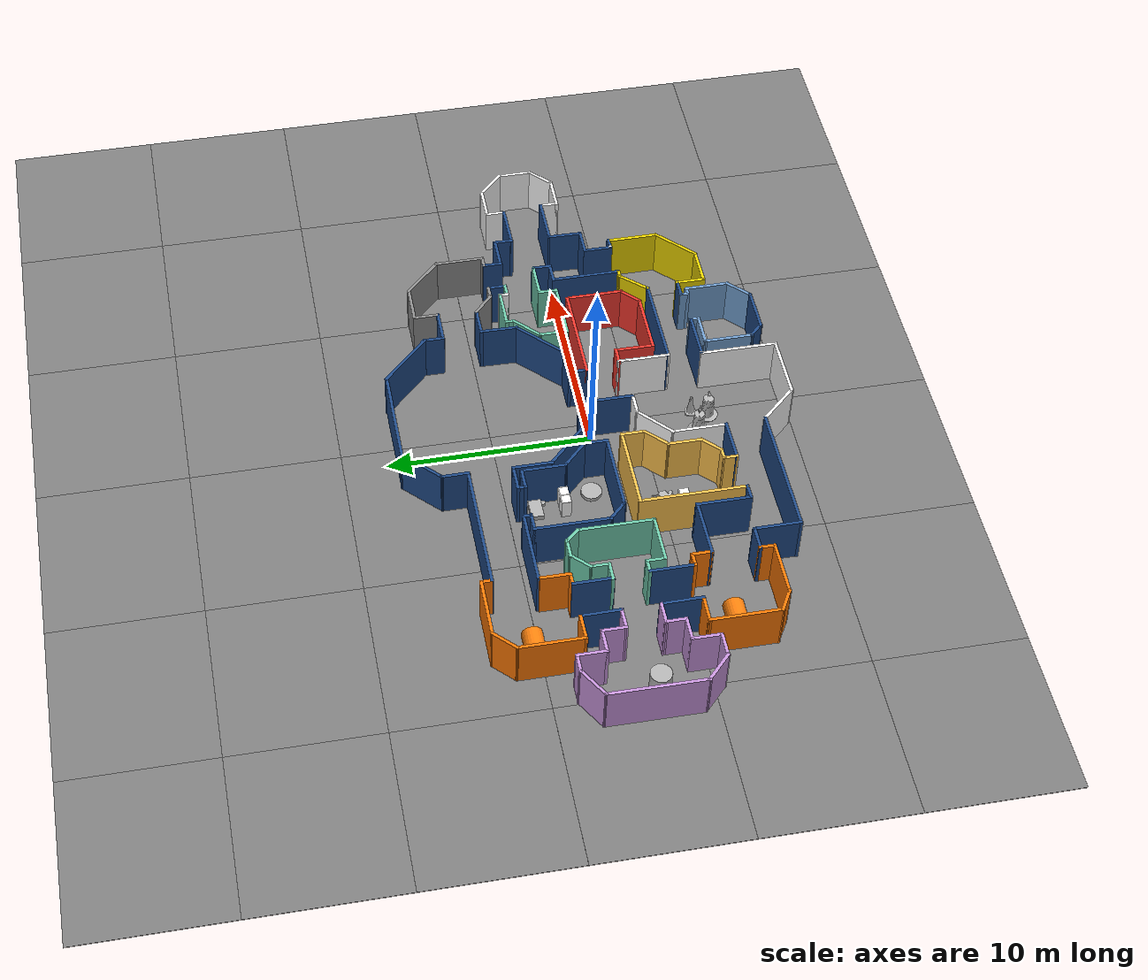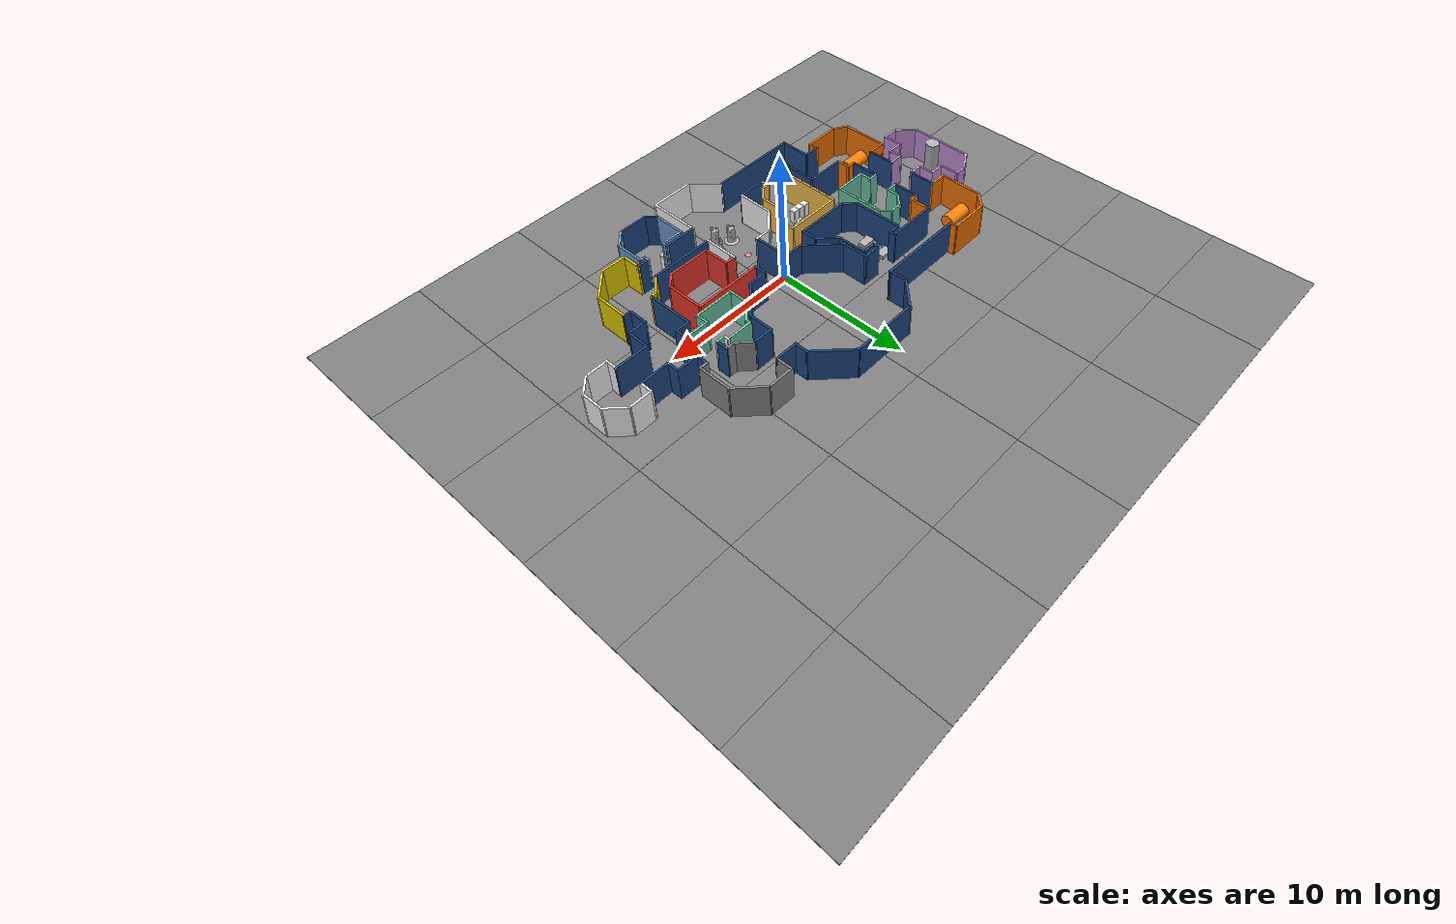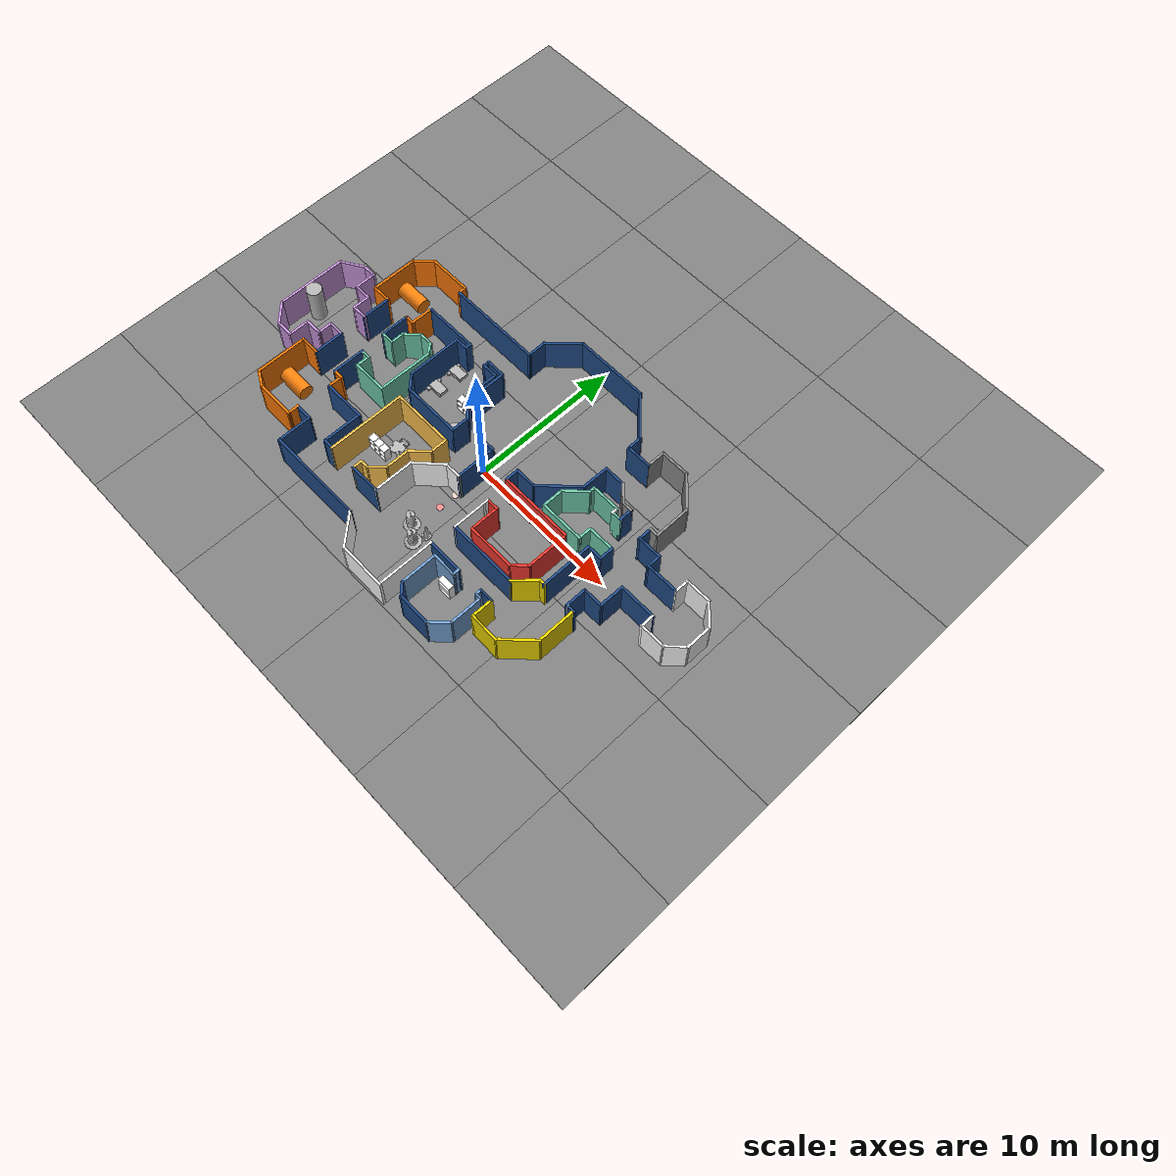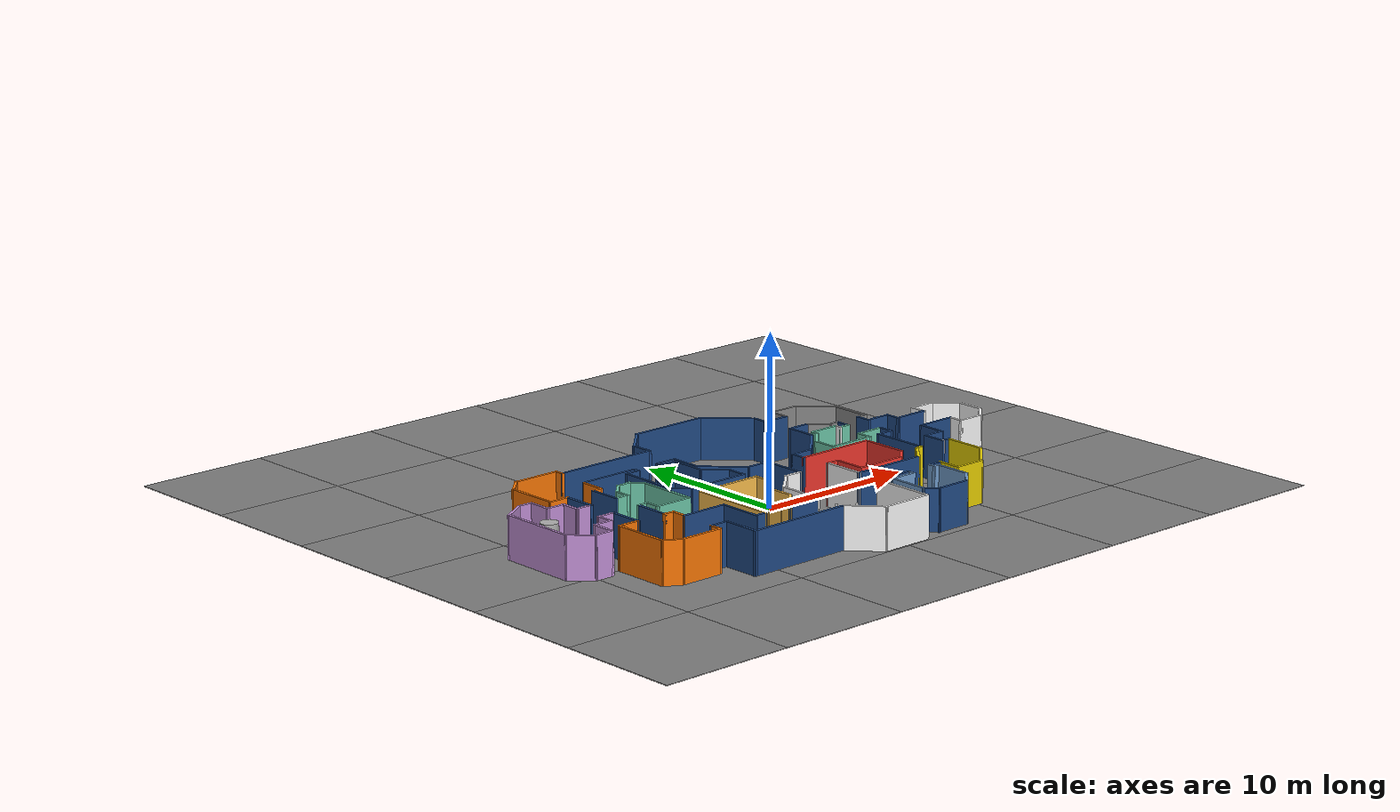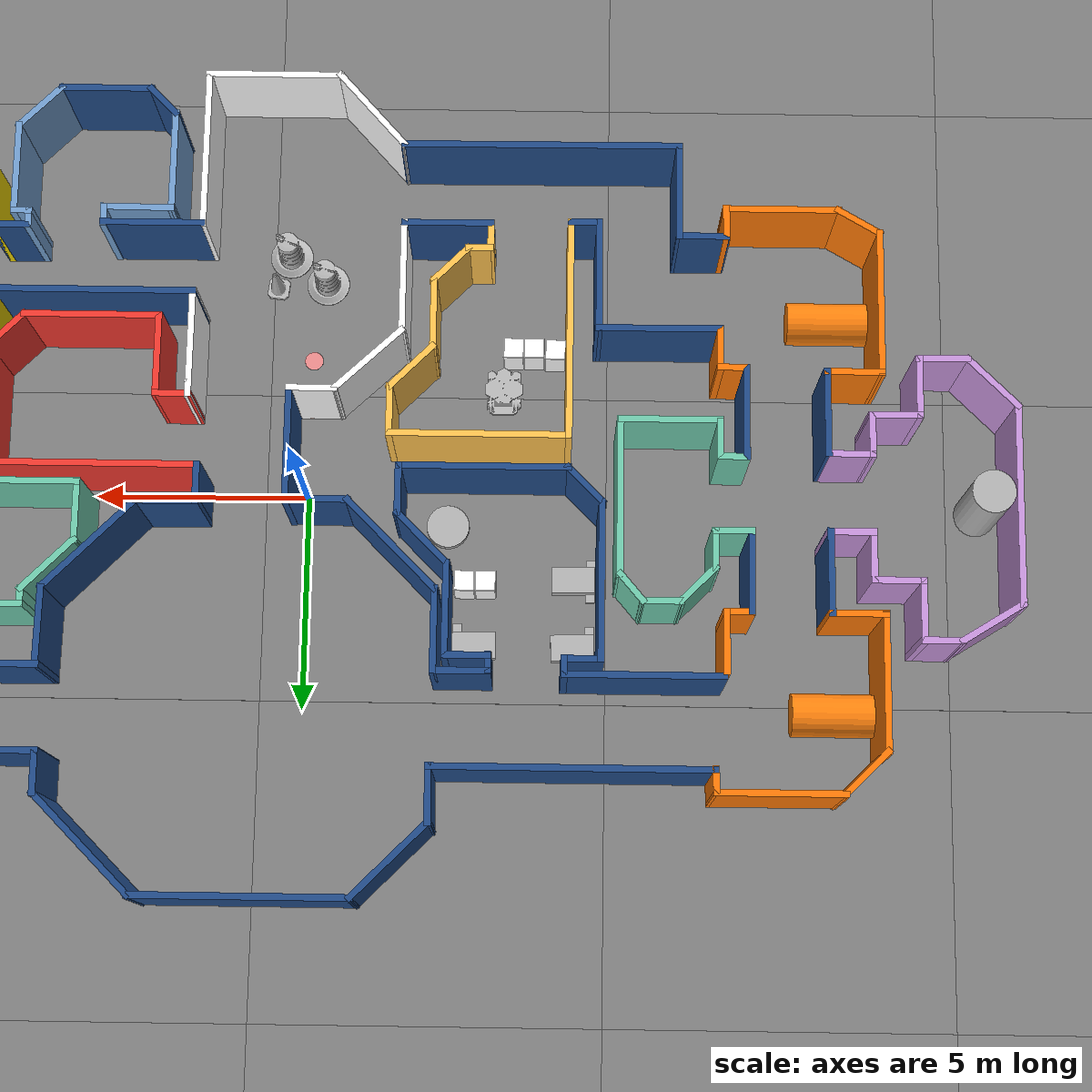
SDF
<sdf version="1.7">
 <world name="default">
  <light name="sun" type="directional">
   <pose>0 0 10 0 -0 0</pose>
   <diffuse>0.8 0.8 0.8 1</diffuse>
   <specular>0.2 0.2 0.2 1</specular>
   <attenuation>
    <range>1000</range>
    <constant>0.9</constant>
    <linear>0.01</linear>
    <quadratic>0.001</quadratic>
   </attenuation>
   <direction>-0.5 0.1 -0.9</direction>
   <spot><inner_angle>0</inner_angle><outer_angle>0</outer_angle><falloff>0</falloff></spot>
  </light>
  <gravity>0 0 -9.8</gravity>
  <magnetic_field>6e-06 2.3e-05 -4.2e-05</magnetic_field>
  <atmosphere type="adiabatic"/>
  <physics name="default_physics" default="0" type="ode">
   <max_step_size>0.001</max_step_size>
   <real_time_factor>1</real_time_factor>
   <real_time_update_rate>1000</real_time_update_rate>
  </physics>
  <scene>
   <ambient>0.62 0.62 0.60 1</ambient>
   <background>0.58 0.58 0.56 1</background>
   <shadows>1</shadows>
  </scene>
  <audio><device>default</device></audio>
  <spherical_coordinates>
   <surface_model>EARTH_WGS84</surface_model>
   <latitude_deg>0</latitude_deg>
   <longitude_deg>0</longitude_deg>
   <elevation>0</elevation>
   <heading_deg>0</heading_deg>
  </spherical_coordinates>
  <model name="among_us_world">
   <pose>0.133216 -0.12311 0 0 -0 0</pose>
   <link name="Wall_0">
    <collision name="Wall_0_Collision">
     <geometry><box><size>5 0.15 2.5</size></box></geometry>
     <pose>0 0 1.25 0 -0 0</pose>
    </collision>
    <visual name="Wall_0_Visual">
     <pose>0 0 1.25 0 -0 0</pose>
     <geometry><box><size>5 0.15 2.5</size></box></geometry>
     <material>
      <ambient>0.12549 0.290196 0.529412 1</ambient>
      <diffuse>0.12549 0.290196 0.529412 1</diffuse>
      <specular>0.08 0.08 0.08 1</specular>
      <emissive>0 0 0 1</emissive>
      <pbr>
       <metal>
        <albedo_map>model://asphalt_plane/materials/textures/tarmac.png</albedo_map>
        <roughness>0.85</roughness>
        <metalness>0</metalness>
       </metal>
      </pbr>
     </material>
     <meta><layer>0</layer></meta>
    </visual>
    <pose>0.883234 9.56872 0 0 -0 0</pose>
   </link>
   <link name="Wall_1">
    <collision name="Wall_1_Collision">
     <geometry><box><size>3.25 0.15 2.5</size></box></geometry>
     <pose>0 0 1.25 0 -0 0</pose>
    </collision>
    <visual name="Wall_1_Visual">
     <pose>0 0 1.25 0 -0 0</pose>
     <geometry><box><size>3.25 0.15 2.5</size></box></geometry>
     <material>
      <ambient>0.12549 0.290196 0.529412 1</ambient>
      <diffuse>0.12549 0.290196 0.529412 1</diffuse>
      <specular>0.08 0.08 0.08 1</specular>
      <emissive>0 0 0 1</emissive>
      <pbr>
       <metal>
        <albedo_map>model://asphalt_plane/materials/textures/tarmac.png</albedo_map>
        <roughness>0.85</roughness>
        <metalness>0</metalness>
       </metal>
      </pbr>
     </material>
     <meta><layer>0</layer></meta>
    </visual>
    <pose>4.40446 8.47278 0 0 -0 -0.785267</pose>
   </link>
   <link name="Wall_10">
    <collision name="Wall_10_Collision">
     <geometry><box><size>0.677967 0.15 2.5</size></box></geometry>
     <pose>0 0 1.25 0 -0 0</pose>
    </collision>
    <visual name="Wall_10_Visual">
     <pose>0 0 1.25 0 -0 0</pose>
     <geometry><box><size>0.677967 0.15 2.5</size></box></geometry>
     <material>
      <ambient>0.55 0.55 0.55 1</ambient>
      <diffuse>0.55 0.55 0.55 1</diffuse>
      <specular>0.08 0.08 0.08 1</specular>
      <emissive>0 0 0 1</emissive>
      <pbr><metal><roughness>0.85</roughness><metalness>0</metalness></metal></pbr>
     </material>
     <meta><layer>0</layer></meta>
    </visual>
    <pose>10.3484 3.61514 0 0 -0 3.14159</pose>
   </link>
   <link name="Wall_101">
    <collision name="Wall_101_Collision">
     <geometry><box><size>3.75 0.15 2.5</size></box></geometry>
     <pose>0 0 1.25 0 -0 0</pose>
    </collision>
    <visual name="Wall_101_Visual">
     <pose>0 0 1.25 0 -0 0</pose>
     <geometry><box><size>3.75 0.15 2.5</size></box></geometry>
     <material>
      <ambient>0.12549 0.290196 0.529412 1</ambient>
      <diffuse>0.12549 0.290196 0.529412 1</diffuse>
      <specular>0.08 0.08 0.08 1</specular>
      <emissive>0 0 0 1</emissive>
      <pbr>
       <metal>
        <albedo_map>model://among_us_world/materials/textures/ceiling_tiled_32_74_135.jpg</albedo_map>
        <roughness>0.85</roughness>
        <metalness>0</metalness>
       </metal>
      </pbr>
     </material>
     <meta><layer>0</layer></meta>
    </visual>
    <pose>-6.98451 2.43054 0 0 -0 -1.5708</pose>
   </link>
   <link name="Wall_103">
    <collision name="Wall_103_Collision">
     <geometry><box><size>1.25 0.15 2.5</size></box></geometry>
     <pose>0 0 1.25 0 -0 0</pose>
    </collision>
    <visual name="Wall_103_Visual">
     <pose>0 0 1.25 0 -0 0</pose>
     <geometry><box><size>1.25 0.15 2.5</size></box></geometry>
     <material>
      <ambient>0.12549 0.290196 0.529412 1</ambient>
      <diffuse>0.12549 0.290196 0.529412 1</diffuse>
      <specular>0.08 0.08 0.08 1</specular>
      <emissive>0 0 0 1</emissive>
      <pbr>
       <metal>
        <albedo_map>model://among_us_world/materials/textures/ceiling_tiled_32_74_135.jpg</albedo_map>
        <roughness>0.85</roughness>
        <metalness>0</metalness>
       </metal>
      </pbr>
     </material>
     <meta><layer>0</layer></meta>
    </visual>
    <pose>-6.5956 0.241636 0 0 -0 -0.785398</pose>
   </link>
   <link name="Wall_104">
    <collision name="Wall_104_Collision">
     <geometry><box><size>4 0.15 2.5</size></box></geometry>
     <pose>0 0 1.25 0 -0 0</pose>
    </collision>
    <visual name="Wall_104_Visual">
     <pose>0 0 1.25 0 -0 0</pose>
     <geometry><box><size>4 0.15 2.5</size></box></geometry>
     <material>
      <ambient>0.12549 0.290196 0.529412 1</ambient>
      <diffuse>0.12549 0.290196 0.529412 1</diffuse>
      <specular>0.08 0.08 0.08 1</specular>
      <emissive>0 0 0 1</emissive>
      <pbr>
       <metal>
        <albedo_map>model://among_us_world/materials/textures/ceiling_tiled_32_74_135.jpg</albedo_map>
        <roughness>0.85</roughness>
        <metalness>0</metalness>
       </metal>
      </pbr>
     </material>
     <meta><layer>0</layer></meta>
    </visual>
    <pose>-4.28169 -0.147272 0 0 -0 0</pose>
   </link>
   <link name="Wall_105">
    <collision name="Wall_105_Collision">
     <geometry><box><size>1.25 0.15 2.5</size></box></geometry>
     <pose>0 0 1.25 0 -0 0</pose>
    </collision>
    <visual name="Wall_105_Visual">
     <pose>0 0 1.25 0 -0 0</pose>
     <geometry><box><size>1.25 0.15 2.5</size></box></geometry>
     <material>
      <ambient>0.12549 0.290196 0.529412 1</ambient>
      <diffuse>0.12549 0.290196 0.529412 1</diffuse>
      <specular>0.08 0.08 0.08 1</specular>
      <emissive>0 0 0 1</emissive>
      <pbr>
       <metal>
        <albedo_map>model://among_us_world/materials/textures/ceiling_tiled_32_74_135.jpg</albedo_map>
        <roughness>0.85</roughness>
        <metalness>0</metalness>
       </metal>
      </pbr>
     </material>
     <meta><layer>0</layer></meta>
    </visual>
    <pose>-2.35669 0.402728 0 0 -0 1.5708</pose>
   </link>
   <link name="Wall_106">
    <collision name="Wall_106_Collision">
     <geometry><box><size>1.75 0.15 2.5</size></box></geometry>
     <pose>0 0 1.25 0 -0 0</pose>
    </collision>
    <visual name="Wall_106_Visual">
     <pose>0 0 1.25 0 -0 0</pose>
     <geometry><box><size>1.75 0.15 2.5</size></box></geometry>
     <material>
      <ambient>0.12549 0.290196 0.529412 1</ambient>
      <diffuse>0.12549 0.290196 0.529412 1</diffuse>
      <specular>0.08 0.08 0.08 1</specular>
      <emissive>0 0 0 1</emissive>
      <pbr>
       <metal>
        <albedo_map>model://among_us_world/materials/textures/ceiling_tiled_32_74_135.jpg</albedo_map>
        <roughness>0.85</roughness>
        <metalness>0</metalness>
       </metal>
      </pbr>
     </material>
     <meta><layer>0</layer></meta>
    </visual>
    <pose>-2.92238 1.51841 0 0 -0 2.35619</pose>
   </link>
   <link name="Wall_108">
    <collision name="Wall_108_Collision">
     <geometry><box><size>2.25 0.15 2.5</size></box></geometry>
     <pose>0 0 1.25 0 -0 0</pose>
    </collision>
    <visual name="Wall_108_Visual">
     <pose>0 0 1.25 0 -0 0</pose>
     <geometry><box><size>2.25 0.15 2.5</size></box></geometry>
     <material>
      <ambient>0.12549 0.290196 0.529412 1</ambient>
      <diffuse>0.12549 0.290196 0.529412 1</diffuse>
      <specular>0.08 0.08 0.08 1</specular>
      <emissive>0 0 0 1</emissive>
      <pbr>
       <metal>
        <albedo_map>model://among_us_world/materials/textures/ceiling_tiled_32_74_135.jpg</albedo_map>
        <roughness>0.85</roughness>
        <metalness>0</metalness>
       </metal>
      </pbr>
     </material>
     <meta><layer>0</layer></meta>
    </visual>
    <pose>-3.48806 3.1341 0 0 -0 1.5708</pose>
   </link>
   <link name="Wall_109">
    <collision name="Wall_109_Collision">
     <geometry><box><size>1.12677 0.15 2.5</size></box></geometry>
     <pose>0 0 1.25 0 -0 0</pose>
    </collision>
    <visual name="Wall_109_Visual">
     <pose>0 0 1.25 0 -0 0</pose>
     <geometry><box><size>1.12677 0.15 2.5</size></box></geometry>
     <material>
      <ambient>0.12549 0.290196 0.529412 1</ambient>
      <diffuse>0.12549 0.290196 0.529412 1</diffuse>
      <specular>0.08 0.08 0.08 1</specular>
      <emissive>0 0 0 1</emissive>
      <pbr>
       <metal>
        <albedo_map>model://among_us_world/materials/textures/ceiling_tiled_32_74_135.jpg</albedo_map>
        <roughness>0.85</roughness>
        <metalness>0</metalness>
       </metal>
      </pbr>
     </material>
     <meta><layer>0</layer></meta>
    </visual>
    <pose>-3.97634 4.1841 0 0 -0 3.14159</pose>
   </link>
   <link name="Wall_11">
    <collision name="Wall_11_Collision">
     <geometry><box><size>1 0.15 2.5</size></box></geometry>
     <pose>0 0 1.25 0 -0 0</pose>
    </collision>
    <visual name="Wall_11_Visual">
     <pose>0 0 1.25 0 -0 0</pose>
     <geometry><box><size>1 0.15 2.5</size></box></geometry>
     <material>
      <ambient>0.12549 0.290196 0.529412 1</ambient>
      <diffuse>0.12549 0.290196 0.529412 1</diffuse>
      <specular>0.08 0.08 0.08 1</specular>
      <emissive>0 0 0 1</emissive>
      <pbr>
       <metal>
        <albedo_map>model://asphalt_plane/materials/textures/tarmac.png</albedo_map>
        <roughness>0.85</roughness>
        <metalness>0</metalness>
       </metal>
      </pbr>
     </material>
     <meta><layer>0</layer></meta>
    </visual>
    <pose>10.0844 3.17225 0 0 -0 -1.5708</pose>
   </link>
   <link name="Wall_110">
    <collision name="Wall_110_Collision">
     <geometry><box><size>0.5 0.15 2.5</size></box></geometry>
     <pose>0 0 1.25 0 -0 0</pose>
    </collision>
    <visual name="Wall_110_Visual">
     <pose>0 0 1.25 0 -0 0</pose>
     <geometry><box><size>0.5 0.15 2.5</size></box></geometry>
     <material>
      <ambient>0.12549 0.290196 0.529412 1</ambient>
      <diffuse>0.12549 0.290196 0.529412 1</diffuse>
      <specular>0.08 0.08 0.08 1</specular>
      <emissive>0 0 0 1</emissive>
      <pbr><metal><roughness>0.85</roughness><metalness>0</metalness></metal></pbr>
     </material>
     <meta><layer>0</layer></meta>
    </visual>
    <pose>-4.46462 4.33852 0 0 -0 1.5708</pose>
   </link>
   <link name="Wall_111">
    <collision name="Wall_111_Collision">
     <geometry><box><size>1.37673 0.15 2.5</size></box></geometry>
     <pose>0 0 1.25 0 -0 0</pose>
    </collision>
    <visual name="Wall_111_Visual">
     <pose>0 0 1.25 0 -0 0</pose>
     <geometry><box><size>1.37673 0.15 2.5</size></box></geometry>
     <material>
      <ambient>0.12549 0.290196 0.529412 1</ambient>
      <diffuse>0.12549 0.290196 0.529412 1</diffuse>
      <specular>0.08 0.08 0.08 1</specular>
      <emissive>0 0 0 1</emissive>
      <pbr>
       <metal>
        <albedo_map>model://asphalt_plane/materials/textures/tarmac.png</albedo_map>
        <roughness>0.85</roughness>
        <metalness>0</metalness>
       </metal>
      </pbr>
     </material>
     <meta><layer>0</layer></meta>
    </visual>
    <pose>-3.85134 4.5341 0 0 -0 0</pose>
   </link>
   <link name="Wall_112">
    <collision name="Wall_112_Collision">
     <geometry><box><size>2 0.15 2.5</size></box></geometry>
     <pose>0 0 1.25 0 -0 0</pose>
    </collision>
    <visual name="Wall_112_Visual">
     <pose>0 0 1.25 0 -0 0</pose>
     <geometry><box><size>2 0.15 2.5</size></box></geometry>
     <material>
      <ambient>0.12549 0.290196 0.529412 1</ambient>
      <diffuse>0.12549 0.290196 0.529412 1</diffuse>
      <specular>0.08 0.08 0.08 1</specular>
      <emissive>0 0 0 1</emissive>
      <pbr>
       <metal>
        <albedo_map>model://asphalt_plane/materials/textures/tarmac.png</albedo_map>
        <roughness>0.85</roughness>
        <metalness>0</metalness>
       </metal>
      </pbr>
     </material>
     <meta><layer>0</layer></meta>
    </visual>
    <pose>-3.23806 3.6091 0 0 -0 -1.5708</pose>
   </link>
   <link name="Wall_114">
    <collision name="Wall_114_Collision">
     <geometry><box><size>3 0.15 2.5</size></box></geometry>
     <pose>0 0 1.25 0 -0 0</pose>
    </collision>
    <visual name="Wall_114_Visual">
     <pose>0 0 1.25 0 -0 0</pose>
     <geometry><box><size>3 0.15 2.5</size></box></geometry>
     <material>
      <ambient>0.12549 0.290196 0.529412 1</ambient>
      <diffuse>0.12549 0.290196 0.529412 1</diffuse>
      <specular>0.08 0.08 0.08 1</specular>
      <emissive>0 0 0 1</emissive>
      <pbr>
       <metal>
        <albedo_map>model://asphalt_plane/materials/textures/tarmac.png</albedo_map>
        <roughness>0.85</roughness>
        <metalness>0</metalness>
       </metal>
      </pbr>
     </material>
     <meta><layer>0</layer></meta>
    </visual>
    <pose>-2.23043 1.67647 0 0 -0 -0.785398</pose>
   </link>
   <link name="Wall_115">
    <collision name="Wall_115_Collision">
     <geometry><box><size>1.5655 0.15 2.5</size></box></geometry>
     <pose>0 0 1.25 0 -0 0</pose>
    </collision>
    <visual name="Wall_115_Visual">
     <pose>0 0 1.25 0 -0 0</pose>
     <geometry><box><size>1.5655 0.15 2.5</size></box></geometry>
     <material>
      <ambient>0.12549 0.290196 0.529412 1</ambient>
      <diffuse>0.12549 0.290196 0.529412 1</diffuse>
      <specular>0.08 0.08 0.08 1</specular>
      <emissive>0 0 0 1</emissive>
      <pbr>
       <metal>
        <albedo_map>model://asphalt_plane/materials/textures/tarmac.png</albedo_map>
        <roughness>0.85</roughness>
        <metalness>0</metalness>
       </metal>
      </pbr>
     </material>
     <meta><layer>0</layer></meta>
    </visual>
    <pose>-0.515099 0.662156 0 0 -0 -0.00945</pose>
   </link>
   <link name="Wall_116">
    <collision name="Wall_116_Collision">
     <geometry><box><size>2.75 0.15 2.5</size></box></geometry>
     <pose>0 0 1.25 0 -0 0</pose>
    </collision>
    <visual name="Wall_116_Visual">
     <pose>0 0 1.25 0 -0 0</pose>
     <geometry><box><size>2.75 0.15 2.5</size></box></geometry>
     <material>
      <ambient>0.12549 0.290196 0.529412 1</ambient>
      <diffuse>0.12549 0.290196 0.529412 1</diffuse>
      <specular>0.08 0.08 0.08 1</specular>
      <emissive>0 0 0 1</emissive>
      <pbr>
       <metal>
        <albedo_map>model://asphalt_plane/materials/textures/tarmac.png</albedo_map>
        <roughness>0.85</roughness>
        <metalness>0</metalness>
       </metal>
      </pbr>
     </material>
     <meta><layer>0</layer></meta>
    </visual>
    <pose>0.19261 -0.637844 0 0 -0 -1.5708</pose>
   </link>
   <link name="Wall_118">
    <collision name="Wall_118_Collision">
     <geometry><box><size>1.5 0.15 2.5</size></box></geometry>
     <pose>0 0 1.25 0 -0 0</pose>
    </collision>
    <visual name="Wall_118_Visual">
     <pose>0 0 1.25 0 -0 0</pose>
     <geometry><box><size>1.5 0.15 2.5</size></box></geometry>
     <material>
      <ambient>0.12549 0.290196 0.529412 1</ambient>
      <diffuse>0.12549 0.290196 0.529412 1</diffuse>
      <specular>0.08 0.08 0.08 1</specular>
      <emissive>0 0 0 1</emissive>
      <pbr>
       <metal>
        <albedo_map>model://asphalt_plane/materials/textures/tarmac.png</albedo_map>
        <roughness>0.85</roughness>
        <metalness>0</metalness>
       </metal>
      </pbr>
     </material>
     <meta><layer>0</layer></meta>
    </visual>
    <pose>6.27303 4.52497 0 0 -0 0</pose>
   </link>
   <link name="Wall_119">
    <collision name="Wall_119_Collision">
     <geometry><box><size>1.41276 0.15 2.5</size></box></geometry>
     <pose>0 0 1.25 0 -0 0</pose>
    </collision>
    <visual name="Wall_119_Visual">
     <pose>0 0 1.25 0 -0 0</pose>
     <geometry><box><size>1.41276 0.15 2.5</size></box></geometry>
     <material>
      <ambient>0.55 0.55 0.55 1</ambient>
      <diffuse>0.55 0.55 0.55 1</diffuse>
      <specular>0.08 0.08 0.08 1</specular>
      <emissive>0 0 0 1</emissive>
      <pbr><metal><roughness>0.85</roughness><metalness>0</metalness></metal></pbr>
     </material>
     <meta><layer>0</layer></meta>
    </visual>
    <pose>7.42533 4.09435 0 0 -0 -0.750545</pose>
   </link>
   <link name="Wall_12">
    <collision name="Wall_12_Collision">
     <geometry><box><size>1.67797 0.15 2.5</size></box></geometry>
     <pose>0 0 1.25 0 -0 0</pose>
    </collision>
    <visual name="Wall_12_Visual">
     <pose>0 0 1.25 0 -0 0</pose>
     <geometry><box><size>1.67797 0.15 2.5</size></box></geometry>
     <material>
      <ambient>0.12549 0.290196 0.529412 1</ambient>
      <diffuse>0.12549 0.290196 0.529412 1</diffuse>
      <specular>0.08 0.08 0.08 1</specular>
      <emissive>0 0 0 1</emissive>
      <pbr>
       <metal>
        <albedo_map>model://asphalt_plane/materials/textures/tarmac.png</albedo_map>
        <roughness>0.85</roughness>
        <metalness>0</metalness>
       </metal>
      </pbr>
     </material>
     <meta><layer>0</layer></meta>
    </visual>
    <pose>10.8484 2.76514 0 0 -0 0</pose>
   </link>
   <link name="Wall_122">
    <collision name="Wall_122_Collision">
     <geometry><box><size>0.75 0.15 2.5</size></box></geometry>
     <pose>0 0 1.25 0 -0 0</pose>
    </collision>
    <visual name="Wall_122_Visual">
     <pose>0 0 1.25 0 -0 0</pose>
     <geometry><box><size>0.75 0.15 2.5</size></box></geometry>
     <material>
      <ambient>0.55 0.55 0.55 1</ambient>
      <diffuse>0.55 0.55 0.55 1</diffuse>
      <specular>0.08 0.08 0.08 1</specular>
      <emissive>0 0 0 1</emissive>
      <pbr><metal><roughness>0.85</roughness><metalness>0</metalness></metal></pbr>
     </material>
     <meta><layer>0</layer></meta>
    </visual>
    <pose>8.18707 3.66372 0 0 -0 0</pose>
   </link>
   <link name="Wall_123">
    <collision name="Wall_123_Collision">
     <geometry><box><size>1 0.15 2.5</size></box></geometry>
     <pose>0 0 1.25 0 -0 0</pose>
    </collision>
    <visual name="Wall_123_Visual">
     <pose>0 0 1.25 0 -0 0</pose>
     <geometry><box><size>1 0.15 2.5</size></box></geometry>
     <material>
      <ambient>0.12549 0.290196 0.529412 1</ambient>
      <diffuse>0.12549 0.290196 0.529412 1</diffuse>
      <specular>0.08 0.08 0.08 1</specular>
      <emissive>0 0 0 1</emissive>
      <pbr>
       <metal>
        <albedo_map>model://asphalt_plane/materials/textures/tarmac.png</albedo_map>
        <roughness>0.85</roughness>
        <metalness>0</metalness>
       </metal>
      </pbr>
     </material>
     <meta><layer>0</layer></meta>
    </visual>
    <pose>8.48707 3.23872 0 0 -0 -1.5708</pose>
   </link>
   <link name="Wall_124">
    <collision name="Wall_124_Collision">
     <geometry><box><size>0.75 0.15 2.5</size></box></geometry>
     <pose>0 0 1.25 0 -0 0</pose>
    </collision>
    <visual name="Wall_124_Visual">
     <pose>0 0 1.25 0 -0 0</pose>
     <geometry><box><size>0.75 0.15 2.5</size></box></geometry>
     <material>
      <ambient>0.435294 0.796078 0.67451 1</ambient>
      <diffuse>0.435294 0.796078 0.67451 1</diffuse>
      <specular>0.08 0.08 0.08 1</specular>
      <emissive>0 0 0 1</emissive>
      <pbr>
       <metal>
        <albedo_map>model://among_us_world/materials/textures/ceiling_tiled_111_203_172.jpg</albedo_map>
        <roughness>0.85</roughness>
        <metalness>0</metalness>
       </metal>
      </pbr>
     </material>
     <meta><layer>0</layer></meta>
    </visual>
    <pose>8.18707 2.81372 0 0 -0 3.14159</pose>
   </link>
   <link name="Wall_125">
    <collision name="Wall_125_Collision">
     <geometry><box><size>0.5 0.15 2.5</size></box></geometry>
     <pose>0 0 1.25 0 -0 0</pose>
    </collision>
    <visual name="Wall_125_Visual">
     <pose>0 0 1.25 0 -0 0</pose>
     <geometry><box><size>0.5 0.15 2.5</size></box></geometry>
     <material>
      <ambient>1 1 1 1</ambient>
      <diffuse>1 1 1 1</diffuse>
      <specular>0.08 0.08 0.08 1</specular>
      <emissive>0 0 0 1</emissive>
      <pbr>
       <metal>
        <albedo_map>model://among_us_world/materials/textures/ceiling_tiled_255_255_255.jpg</albedo_map>
        <roughness>0.85</roughness>
        <metalness>0</metalness>
       </metal>
      </pbr>
     </material>
     <meta><layer>0</layer></meta>
    </visual>
    <pose>7.88707 2.98872 0 0 -0 1.5708</pose>
   </link>
   <link name="Wall_126">
    <collision name="Wall_126_Collision">
     <geometry><box><size>2 0.15 2.5</size></box></geometry>
     <pose>0 0 1.25 0 -0 0</pose>
    </collision>
    <visual name="Wall_126_Visual">
     <pose>0 0 1.25 0 -0 0</pose>
     <geometry><box><size>2 0.15 2.5</size></box></geometry>
     <material>
      <ambient>0.435294 0.796078 0.67451 1</ambient>
      <diffuse>0.435294 0.796078 0.67451 1</diffuse>
      <specular>0.08 0.08 0.08 1</specular>
      <emissive>0 0 0 1</emissive>
      <pbr>
       <metal>
        <albedo_map>model://among_us_world/materials/textures/ceiling_tiled_111_203_172.jpg</albedo_map>
        <roughness>0.85</roughness>
        <metalness>0</metalness>
       </metal>
      </pbr>
     </material>
     <meta><layer>0</layer></meta>
    </visual>
    <pose>6.96207 3.16372 0 0 -0 3.14159</pose>
   </link>
   <link name="Wall_127">
    <collision name="Wall_127_Collision">
     <geometry><box><size>0.5 0.15 2.5</size></box></geometry>
     <pose>0 0 1.25 0 -0 0</pose>
    </collision>
    <visual name="Wall_127_Visual">
     <pose>0 0 1.25 0 -0 0</pose>
     <geometry><box><size>0.5 0.15 2.5</size></box></geometry>
     <material>
      <ambient>0.435294 0.796078 0.67451 1</ambient>
      <diffuse>0.435294 0.796078 0.67451 1</diffuse>
      <specular>0.08 0.08 0.08 1</specular>
      <emissive>0 0 0 1</emissive>
      <pbr>
       <metal>
        <albedo_map>model://among_us_world/materials/textures/ceiling_tiled_111_203_172.jpg</albedo_map>
        <roughness>0.85</roughness>
        <metalness>0</metalness>
       </metal>
      </pbr>
     </material>
     <meta><layer>0</layer></meta>
    </visual>
    <pose>6.03707 2.98872 0 0 -0 -1.5708</pose>
   </link>
   <link name="Wall_128">
    <collision name="Wall_128_Collision">
     <geometry><box><size>1.75 0.15 2.5</size></box></geometry>
     <pose>0 0 1.25 0 -0 0</pose>
    </collision>
    <visual name="Wall_128_Visual">
     <pose>0 0 1.25 0 -0 0</pose>
     <geometry><box><size>1.75 0.15 2.5</size></box></geometry>
     <material>
      <ambient>0.435294 0.796078 0.67451 1</ambient>
      <diffuse>0.435294 0.796078 0.67451 1</diffuse>
      <specular>0.08 0.08 0.08 1</specular>
      <emissive>0 0 0 1</emissive>
      <pbr>
       <metal>
        <albedo_map>model://among_us_world/materials/textures/ceiling_tiled_111_203_172.jpg</albedo_map>
        <roughness>0.85</roughness>
        <metalness>0</metalness>
       </metal>
      </pbr>
     </material>
     <meta><layer>0</layer></meta>
    </visual>
    <pose>5.47138 2.24804 0 0 -0 -2.35619</pose>
   </link>
   <link name="Wall_129">
    <collision name="Wall_129_Collision">
     <geometry><box><size>1.5 0.15 2.5</size></box></geometry>
     <pose>0 0 1.25 0 -0 0</pose>
    </collision>
    <visual name="Wall_129_Visual">
     <pose>0 0 1.25 0 -0 0</pose>
     <geometry><box><size>1.5 0.15 2.5</size></box></geometry>
     <material>
      <ambient>0.435294 0.796078 0.67451 1</ambient>
      <diffuse>0.435294 0.796078 0.67451 1</diffuse>
      <specular>0.08 0.08 0.08 1</specular>
      <emissive>0 0 0 1</emissive>
      <pbr><metal><roughness>0.85</roughness><metalness>0</metalness></metal></pbr>
     </material>
     <meta><layer>0</layer></meta>
    </visual>
    <pose>4.9057 1.00735 0 0 -0 -1.5708</pose>
   </link>
   <link name="Wall_13">
    <collision name="Wall_13_Collision">
     <geometry><box><size>0.99953 0.15 2.5</size></box></geometry>
     <pose>0 0 1.25 0 -0 0</pose>
    </collision>
    <visual name="Wall_13_Visual">
     <pose>0 0 1.25 0 -0 0</pose>
     <geometry><box><size>0.99953 0.15 2.5</size></box></geometry>
     <material>
      <ambient>0.12549 0.290196 0.529412 1</ambient>
      <diffuse>0.12549 0.290196 0.529412 1</diffuse>
      <specular>0.08 0.08 0.08 1</specular>
      <emissive>0 0 0 1</emissive>
      <pbr>
       <metal>
        <albedo_map>model://asphalt_plane/materials/textures/tarmac.png</albedo_map>
        <roughness>0.85</roughness>
        <metalness>0</metalness>
       </metal>
      </pbr>
     </material>
     <meta><layer>0</layer></meta>
    </visual>
    <pose>11.6124 2.34037 0 0 -0 -1.5708</pose>
   </link>
   <link name="Wall_130">
    <collision name="Wall_130_Collision">
     <geometry><box><size>3 0.15 2.5</size></box></geometry>
     <pose>0 0 1.25 0 -0 0</pose>
    </collision>
    <visual name="Wall_130_Visual">
     <pose>0 0 1.25 0 -0 0</pose>
     <geometry><box><size>3 0.15 2.5</size></box></geometry>
     <material>
      <ambient>0.435294 0.796078 0.67451 1</ambient>
      <diffuse>0.435294 0.796078 0.67451 1</diffuse>
      <specular>0.08 0.08 0.08 1</specular>
      <emissive>0 0 0 1</emissive>
      <pbr>
       <metal>
        <albedo_map>model://among_us_world/materials/textures/ceiling_tiled_111_203_172.jpg</albedo_map>
        <roughness>0.85</roughness>
        <metalness>0</metalness>
       </metal>
      </pbr>
     </material>
     <meta><layer>0</layer></meta>
    </visual>
    <pose>6.3307 0.332351 0 0 -0 0</pose>
   </link>
   <link name="Wall_131">
    <collision name="Wall_131_Collision">
     <geometry><box><size>1 0.15 2.5</size></box></geometry>
     <pose>0 0 1.25 0 -0 0</pose>
    </collision>
    <visual name="Wall_131_Visual">
     <pose>0 0 1.25 0 -0 0</pose>
     <geometry><box><size>1 0.15 2.5</size></box></geometry>
     <material>
      <ambient>0.435294 0.796078 0.67451 1</ambient>
      <diffuse>0.435294 0.796078 0.67451 1</diffuse>
      <specular>0.08 0.08 0.08 1</specular>
      <emissive>0 0 0 1</emissive>
      <pbr>
       <metal>
        <albedo_map>model://among_us_world/materials/textures/ceiling_tiled_111_203_172.jpg</albedo_map>
        <roughness>0.85</roughness>
        <metalness>0</metalness>
       </metal>
      </pbr>
     </material>
     <meta><layer>0</layer></meta>
    </visual>
    <pose>7.7557 0.757351 0 0 -0 1.5708</pose>
   </link>
   <link name="Wall_132">
    <collision name="Wall_132_Collision">
     <geometry><box><size>1.85593 0.15 2.5</size></box></geometry>
     <pose>0 0 1.25 0 -0 0</pose>
    </collision>
    <visual name="Wall_132_Visual">
     <pose>0 0 1.25 0 -0 0</pose>
     <geometry><box><size>1.85593 0.15 2.5</size></box></geometry>
     <material>
      <ambient>0.435294 0.796078 0.67451 1</ambient>
      <diffuse>0.435294 0.796078 0.67451 1</diffuse>
      <specular>0.08 0.08 0.08 1</specular>
      <emissive>0 0 0 1</emissive>
      <pbr>
       <metal>
        <albedo_map>model://among_us_world/materials/textures/ceiling_tiled_111_203_172.jpg</albedo_map>
        <roughness>0.85</roughness>
        <metalness>0</metalness>
       </metal>
      </pbr>
     </material>
     <meta><layer>0</layer></meta>
    </visual>
    <pose>8.60867 1.18235 0 0 -0 0</pose>
   </link>
   <link name="Wall_133">
    <collision name="Wall_133_Collision">
     <geometry><box><size>1 0.15 2.5</size></box></geometry>
     <pose>0 0 1.25 0 -0 0</pose>
    </collision>
    <visual name="Wall_133_Visual">
     <pose>0 0 1.25 0 -0 0</pose>
     <geometry><box><size>1 0.15 2.5</size></box></geometry>
     <material>
      <ambient>0.12549 0.290196 0.529412 1</ambient>
      <diffuse>0.12549 0.290196 0.529412 1</diffuse>
      <specular>0.08 0.08 0.08 1</specular>
      <emissive>0 0 0 1</emissive>
      <pbr>
       <metal>
        <albedo_map>model://asphalt_plane/materials/textures/tarmac.png</albedo_map>
        <roughness>0.85</roughness>
        <metalness>0</metalness>
       </metal>
      </pbr>
     </material>
     <meta><layer>0</layer></meta>
    </visual>
    <pose>9.47952 0.757351 0 0 -0 -1.5708</pose>
   </link>
   <link name="Wall_134">
    <collision name="Wall_134_Collision">
     <geometry><box><size>1.10593 0.15 2.5</size></box></geometry>
     <pose>0 0 1.25 0 -0 0</pose>
    </collision>
    <visual name="Wall_134_Visual">
     <pose>0 0 1.25 0 -0 0</pose>
     <geometry><box><size>1.10593 0.15 2.5</size></box></geometry>
     <material>
      <ambient>0.12549 0.290196 0.529412 1</ambient>
      <diffuse>0.12549 0.290196 0.529412 1</diffuse>
      <specular>0.08 0.08 0.08 1</specular>
      <emissive>0 0 0 1</emissive>
      <pbr>
       <metal>
        <albedo_map>model://asphalt_plane/materials/textures/tarmac.png</albedo_map>
        <roughness>0.85</roughness>
        <metalness>0</metalness>
       </metal>
      </pbr>
     </material>
     <meta><layer>0</layer></meta>
    </visual>
    <pose>8.98367 0.332351 0 0 -0 3.14159</pose>
   </link>
   <link name="Wall_135">
    <collision name="Wall_135_Collision">
     <geometry><box><size>3.5 0.15 2.5</size></box></geometry>
     <pose>0 0 1.25 0 -0 0</pose>
    </collision>
    <visual name="Wall_135_Visual">
     <pose>0 0 1.25 0 -0 0</pose>
     <geometry><box><size>3.5 0.15 2.5</size></box></geometry>
     <material>
      <ambient>0.12549 0.290196 0.529412 1</ambient>
      <diffuse>0.12549 0.290196 0.529412 1</diffuse>
      <specular>0.08 0.08 0.08 1</specular>
      <emissive>0 0 0 1</emissive>
      <pbr>
       <metal>
        <albedo_map>model://asphalt_plane/materials/textures/tarmac.png</albedo_map>
        <roughness>0.85</roughness>
        <metalness>0</metalness>
       </metal>
      </pbr>
     </material>
     <meta><layer>0</layer></meta>
    </visual>
    <pose>8.5057 -1.34265 0 0 -0 -1.5708</pose>
   </link>
   <link name="Wall_136">
    <collision name="Wall_136_Collision">
     <geometry><box><size>0.5 0.15 2.5</size></box></geometry>
     <pose>0 0 1.25 0 -0 0</pose>
    </collision>
    <visual name="Wall_136_Visual">
     <pose>0 0 1.25 0 -0 0</pose>
     <geometry><box><size>0.5 0.15 2.5</size></box></geometry>
     <material>
      <ambient>0.929412 0.831373 0 1</ambient>
      <diffuse>0.929412 0.831373 0 1</diffuse>
      <specular>0.08 0.08 0.08 1</specular>
      <emissive>0 0 0 1</emissive>
      <pbr>
       <metal>
        <albedo_map>model://among_us_world/materials/textures/ceiling_tiled_237_212_0.jpg</albedo_map>
        <roughness>0.85</roughness>
        <metalness>0</metalness>
       </metal>
      </pbr>
     </material>
     <meta><layer>0</layer></meta>
    </visual>
    <pose>8.3307 -3.01765 0 0 -0 3.14159</pose>
   </link>
   <link name="Wall_14">
    <collision name="Wall_14_Collision">
     <geometry><box><size>2.25007 0.15 2.5</size></box></geometry>
     <pose>0 0 1.25 0 -0 0</pose>
    </collision>
    <visual name="Wall_14_Visual">
     <pose>0 0 1.25 0 -0 0</pose>
     <geometry><box><size>2.25007 0.15 2.5</size></box></geometry>
     <material>
      <ambient>0.12549 0.290196 0.529412 1</ambient>
      <diffuse>0.12549 0.290196 0.529412 1</diffuse>
      <specular>0.08 0.08 0.08 1</specular>
      <emissive>0 0 0 1</emissive>
      <pbr>
       <metal>
        <albedo_map>model://asphalt_plane/materials/textures/tarmac.png</albedo_map>
        <roughness>0.85</roughness>
        <metalness>0</metalness>
       </metal>
      </pbr>
     </material>
     <meta><layer>0</layer></meta>
    </visual>
    <pose>12.6445 1.92431 0 0 -0 0.008281</pose>
   </link>
   <link name="Wall_141">
    <collision name="Wall_141_Collision">
     <geometry><box><size>4.75 0.15 2.5</size></box></geometry>
     <pose>0 0 1.25 0 -0 0</pose>
    </collision>
    <visual name="Wall_141_Visual">
     <pose>0 0 1.25 0 -0 0</pose>
     <geometry><box><size>4.75 0.15 2.5</size></box></geometry>
     <material>
      <ambient>0.12549 0.290196 0.529412 1</ambient>
      <diffuse>0.12549 0.290196 0.529412 1</diffuse>
      <specular>0.08 0.08 0.08 1</specular>
      <emissive>0 0 0 1</emissive>
      <pbr>
       <metal>
        <albedo_map>model://asphalt_plane/materials/textures/tarmac.png</albedo_map>
        <roughness>0.85</roughness>
        <metalness>0</metalness>
       </metal>
      </pbr>
     </material>
     <meta><layer>0</layer></meta>
    </visual>
    <pose>4.78856 -4.21327 0 0 -0 0</pose>
   </link>
   <link name="Wall_143">
    <collision name="Wall_143_Collision">
     <geometry><box><size>1.75259 0.15 2.5</size></box></geometry>
     <pose>0 0 1.25 0 -0 0</pose>
    </collision>
    <visual name="Wall_143_Visual">
     <pose>0 0 1.25 0 -0 0</pose>
     <geometry><box><size>1.75259 0.15 2.5</size></box></geometry>
     <material>
      <ambient>0.929412 0.831373 0 1</ambient>
      <diffuse>0.929412 0.831373 0 1</diffuse>
      <specular>0.08 0.08 0.08 1</specular>
      <emissive>0 0 0 1</emissive>
      <pbr>
       <metal>
        <albedo_map>model://among_us_world/materials/textures/ceiling_tiled_237_212_0.jpg</albedo_map>
        <roughness>0.85</roughness>
        <metalness>0</metalness>
       </metal>
      </pbr>
     </material>
     <meta><layer>0</layer></meta>
    </visual>
    <pose>7.62213 -3.61546 0 0 -0 -2.29947</pose>
   </link>
   <link name="Wall_145">
    <collision name="Wall_145_Collision">
     <geometry><box><size>5.25 0.15 2.5</size></box></geometry>
     <pose>0 0 1.25 0 -0 0</pose>
    </collision>
    <visual name="Wall_145_Visual">
     <pose>0 0 1.25 0 -0 0</pose>
     <geometry><box><size>5.25 0.15 2.5</size></box></geometry>
     <material>
      <ambient>1 0.764706 0.305882 1</ambient>
      <diffuse>1 0.764706 0.305882 1</diffuse>
      <specular>0.08 0.08 0.08 1</specular>
      <emissive>0 0 0 1</emissive>
      <pbr>
       <metal>
        <albedo_map>model://among_us_world/materials/textures/ceiling_tiled_255_195_78.jpg</albedo_map>
        <roughness>0.85</roughness>
        <metalness>0</metalness>
       </metal>
      </pbr>
     </material>
     <meta><layer>0</layer></meta>
    </visual>
    <pose>-6.21277 -3.45528 0 0 -0 1.5708</pose>
   </link>
   <link name="Wall_146">
    <collision name="Wall_146_Collision">
     <geometry><box><size>4.25 0.15 2.5</size></box></geometry>
     <pose>0 0 1.25 0 -0 0</pose>
    </collision>
    <visual name="Wall_146_Visual">
     <pose>0 0 1.25 0 -0 0</pose>
     <geometry><box><size>4.25 0.15 2.5</size></box></geometry>
     <material>
      <ambient>1 0.764706 0.305882 1</ambient>
      <diffuse>1 0.764706 0.305882 1</diffuse>
      <specular>0.08 0.08 0.08 1</specular>
      <emissive>0 0 0 1</emissive>
      <pbr>
       <metal>
        <albedo_map>model://among_us_world/materials/textures/ceiling_tiled_255_195_78.jpg</albedo_map>
        <roughness>0.85</roughness>
        <metalness>0</metalness>
       </metal>
      </pbr>
     </material>
     <meta><layer>0</layer></meta>
    </visual>
    <pose>-4.16277 -0.905283 0 0 -0 0</pose>
   </link>
   <link name="Wall_147">
    <collision name="Wall_147_Collision">
     <geometry><box><size>1.25 0.15 2.5</size></box></geometry>
     <pose>0 0 1.25 0 -0 0</pose>
    </collision>
    <visual name="Wall_147_Visual">
     <pose>0 0 1.25 0 -0 0</pose>
     <geometry><box><size>1.25 0.15 2.5</size></box></geometry>
     <material>
      <ambient>1 0.764706 0.305882 1</ambient>
      <diffuse>1 0.764706 0.305882 1</diffuse>
      <specular>0.08 0.08 0.08 1</specular>
      <emissive>0 0 0 1</emissive>
      <pbr>
       <metal>
        <albedo_map>model://among_us_world/materials/textures/ceiling_tiled_255_195_78.jpg</albedo_map>
        <roughness>0.85</roughness>
        <metalness>0</metalness>
       </metal>
      </pbr>
     </material>
     <meta><layer>0</layer></meta>
    </visual>
    <pose>-2.11277 -1.45528 0 0 -0 -1.5708</pose>
   </link>
   <link name="Wall_148">
    <collision name="Wall_148_Collision">
     <geometry><box><size>1.5 0.15 2.5</size></box></geometry>
     <pose>0 0 1.25 0 -0 0</pose>
    </collision>
    <visual name="Wall_148_Visual">
     <pose>0 0 1.25 0 -0 0</pose>
     <geometry><box><size>1.5 0.15 2.5</size></box></geometry>
     <material>
      <ambient>1 0.764706 0.305882 1</ambient>
      <diffuse>1 0.764706 0.305882 1</diffuse>
      <specular>0.08 0.08 0.08 1</specular>
      <emissive>0 0 0 1</emissive>
      <pbr>
       <metal>
        <albedo_map>model://among_us_world/materials/textures/ceiling_tiled_255_195_78.jpg</albedo_map>
        <roughness>0.85</roughness>
        <metalness>0</metalness>
       </metal>
      </pbr>
     </material>
     <meta><layer>0</layer></meta>
    </visual>
    <pose>-2.59027 -2.48228 0 0 -0 -2.35672</pose>
   </link>
   <link name="Wall_149">
    <collision name="Wall_149_Collision">
     <geometry><box><size>1.75 0.15 2.5</size></box></geometry>
     <pose>0 0 1.25 0 -0 0</pose>
    </collision>
    <visual name="Wall_149_Visual">
     <pose>0 0 1.25 0 -0 0</pose>
     <geometry><box><size>1.75 0.15 2.5</size></box></geometry>
     <material>
      <ambient>1 0.764706 0.305882 1</ambient>
      <diffuse>1 0.764706 0.305882 1</diffuse>
      <specular>0.08 0.08 0.08 1</specular>
      <emissive>0 0 0 1</emissive>
      <pbr><metal><roughness>0.85</roughness><metalness>0</metalness></metal></pbr>
     </material>
     <meta><layer>0</layer></meta>
    </visual>
    <pose>-3.06777 -3.75928 0 0 -0 -1.5708</pose>
   </link>
   <link name="Wall_15">
    <collision name="Wall_15_Collision">
     <geometry><box><size>1.02562 0.15 2.5</size></box></geometry>
     <pose>0 0 1.25 0 -0 0</pose>
    </collision>
    <visual name="Wall_15_Visual">
     <pose>0 0 1.25 0 -0 0</pose>
     <geometry><box><size>1.02562 0.15 2.5</size></box></geometry>
     <material>
      <ambient>1 1 1 1</ambient>
      <diffuse>1 1 1 1</diffuse>
      <specular>0.08 0.08 0.08 1</specular>
      <emissive>0 0 0 1</emissive>
      <pbr>
       <metal>
        <albedo_map>model://among_us_world/materials/textures/ceiling_tiled_46_52_54.jpg</albedo_map>
        <roughness>0.85</roughness>
        <metalness>0</metalness>
       </metal>
      </pbr>
     </material>
     <meta><layer>0</layer></meta>
    </visual>
    <pose>13.7124 2.37081 0 0 -0 1.5708</pose>
   </link>
   <link name="Wall_150">
    <collision name="Wall_150_Collision">
     <geometry><box><size>1.25 0.15 2.5</size></box></geometry>
     <pose>0 0 1.25 0 -0 0</pose>
    </collision>
    <visual name="Wall_150_Visual">
     <pose>0 0 1.25 0 -0 0</pose>
     <geometry><box><size>1.25 0.15 2.5</size></box></geometry>
     <material>
      <ambient>1 0.764706 0.305882 1</ambient>
      <diffuse>1 0.764706 0.305882 1</diffuse>
      <specular>0.08 0.08 0.08 1</specular>
      <emissive>0 0 0 1</emissive>
      <pbr>
       <metal>
        <albedo_map>model://among_us_world/materials/textures/ceiling_tiled_255_195_78.jpg</albedo_map>
        <roughness>0.85</roughness>
        <metalness>0</metalness>
       </metal>
      </pbr>
     </material>
     <meta><layer>0</layer></meta>
    </visual>
    <pose>-3.45677 -4.94828 0 0 -0 -2.35619</pose>
   </link>
   <link name="Wall_153">
    <collision name="Wall_153_Collision">
     <geometry><box><size>0.660076 0.15 2.5</size></box></geometry>
     <pose>0 0 1.25 0 -0 0</pose>
    </collision>
    <visual name="Wall_153_Visual">
     <pose>0 0 1.25 0 -0 0</pose>
     <geometry><box><size>0.660076 0.15 2.5</size></box></geometry>
     <material>
      <ambient>1 0.764706 0.305882 1</ambient>
      <diffuse>1 0.764706 0.305882 1</diffuse>
      <specular>0.08 0.08 0.08 1</specular>
      <emissive>0 0 0 1</emissive>
      <pbr>
       <metal>
        <albedo_map>model://among_us_world/materials/textures/ceiling_tiled_255_195_78.jpg</albedo_map>
        <roughness>0.85</roughness>
        <metalness>0</metalness>
       </metal>
      </pbr>
     </material>
     <meta><layer>0</layer></meta>
    </visual>
    <pose>-4.10077 -5.34628 0 0 -0 -3.10631</pose>
   </link>
   <link name="Wall_154">
    <collision name="Wall_154_Collision">
     <geometry><box><size>0.75 0.15 2.5</size></box></geometry>
     <pose>0 0 1.25 0 -0 0</pose>
    </collision>
    <visual name="Wall_154_Visual">
     <pose>0 0 1.25 0 -0 0</pose>
     <geometry><box><size>0.75 0.15 2.5</size></box></geometry>
     <material>
      <ambient>1 0.764706 0.305882 1</ambient>
      <diffuse>1 0.764706 0.305882 1</diffuse>
      <specular>0.08 0.08 0.08 1</specular>
      <emissive>0 0 0 1</emissive>
      <pbr><metal><roughness>0.85</roughness><metalness>0</metalness></metal></pbr>
     </material>
     <meta><layer>0</layer></meta>
    </visual>
    <pose>-4.35577 -5.65528 0 0 -0 -1.5708</pose>
   </link>
   <link name="Wall_155">
    <collision name="Wall_155_Collision">
     <geometry><box><size>2.16008 0.15 2.5</size></box></geometry>
     <pose>0 0 1.25 0 -0 0</pose>
    </collision>
    <visual name="Wall_155_Visual">
     <pose>0 0 1.25 0 -0 0</pose>
     <geometry><box><size>2.16008 0.15 2.5</size></box></geometry>
     <material>
      <ambient>0.12549 0.290196 0.529412 1</ambient>
      <diffuse>0.12549 0.290196 0.529412 1</diffuse>
      <specular>0.08 0.08 0.08 1</specular>
      <emissive>0 0 0 1</emissive>
      <pbr>
       <metal>
        <albedo_map>model://asphalt_plane/materials/textures/tarmac.png</albedo_map>
        <roughness>0.85</roughness>
        <metalness>0</metalness>
       </metal>
      </pbr>
     </material>
     <meta><layer>0</layer></meta>
    </visual>
    <pose>-3.35065 -5.9463 0 0 -0 0.008937</pose>
   </link>
   <link name="Wall_156">
    <collision name="Wall_156_Collision">
     <geometry><box><size>2.75 0.15 2.5</size></box></geometry>
     <pose>0 0 1.25 0 -0 0</pose>
    </collision>
    <visual name="Wall_156_Visual">
     <pose>0 0 1.25 0 -0 0</pose>
     <geometry><box><size>2.75 0.15 2.5</size></box></geometry>
     <material>
      <ambient>1 1 1 1</ambient>
      <diffuse>1 1 1 1</diffuse>
      <specular>0.08 0.08 0.08 1</specular>
      <emissive>0 0 0 1</emissive>
      <pbr>
       <metal>
        <albedo_map>model://among_us_world/materials/textures/ceiling_tiled_85_87_83.jpg</albedo_map>
        <roughness>0.85</roughness>
        <metalness>0</metalness>
       </metal>
      </pbr>
     </material>
     <meta><layer>0</layer></meta>
    </visual>
    <pose>-2.34553 -4.63732 0 0 -0 1.5708</pose>
   </link>
   <link name="Wall_160">
    <collision name="Wall_160_Collision">
     <geometry><box><size>0.797757 0.15 2.5</size></box></geometry>
     <pose>0 0 1.25 0 -0 0</pose>
    </collision>
    <visual name="Wall_160_Visual">
     <pose>0 0 1.25 0 -0 0</pose>
     <geometry><box><size>0.797757 0.15 2.5</size></box></geometry>
     <material>
      <ambient>0.12549 0.290196 0.529412 1</ambient>
      <diffuse>0.12549 0.290196 0.529412 1</diffuse>
      <specular>0.08 0.08 0.08 1</specular>
      <emissive>0 0 0 1</emissive>
      <pbr>
       <metal>
        <albedo_map>model://asphalt_plane/materials/textures/tarmac.png</albedo_map>
        <roughness>0.85</roughness>
        <metalness>0</metalness>
       </metal>
      </pbr>
     </material>
     <meta><layer>0</layer></meta>
    </visual>
    <pose>-6.53682 -6.00509 0 0 -0 3.14101</pose>
   </link>
   <link name="Wall_161">
    <collision name="Wall_161_Collision">
     <geometry><box><size>2.70224 0.15 2.5</size></box></geometry>
     <pose>0 0 1.25 0 -0 0</pose>
    </collision>
    <visual name="Wall_161_Visual">
     <pose>0 0 1.25 0 -0 0</pose>
     <geometry><box><size>2.70224 0.15 2.5</size></box></geometry>
     <material>
      <ambient>0.12549 0.290196 0.529412 1</ambient>
      <diffuse>0.12549 0.290196 0.529412 1</diffuse>
      <specular>0.08 0.08 0.08 1</specular>
      <emissive>0 0 0 1</emissive>
      <pbr>
       <metal>
        <albedo_map>model://asphalt_plane/materials/textures/tarmac.png</albedo_map>
        <roughness>0.85</roughness>
        <metalness>0</metalness>
       </metal>
      </pbr>
     </material>
     <meta><layer>0</layer></meta>
    </visual>
    <pose>-6.87644 -4.72879 0 0 -0 1.5708</pose>
   </link>
   <link name="Wall_162">
    <collision name="Wall_162_Collision">
     <geometry><box><size>2.95229 0.15 2.5</size></box></geometry>
     <pose>0 0 1.25 0 -0 0</pose>
    </collision>
    <visual name="Wall_162_Visual">
     <pose>0 0 1.25 0 -0 0</pose>
     <geometry><box><size>2.95229 0.15 2.5</size></box></geometry>
     <material>
      <ambient>0.12549 0.290196 0.529412 1</ambient>
      <diffuse>0.12549 0.290196 0.529412 1</diffuse>
      <specular>0.08 0.08 0.08 1</specular>
      <emissive>0 0 0 1</emissive>
      <pbr>
       <metal>
        <albedo_map>model://asphalt_plane/materials/textures/tarmac.png</albedo_map>
        <roughness>0.85</roughness>
        <metalness>0</metalness>
       </metal>
      </pbr>
     </material>
     <meta><layer>0</layer></meta>
    </visual>
    <pose>-8.262 -3.46044 0 0 -0 -3.13604</pose>
   </link>
   <link name="Wall_163">
    <collision name="Wall_163_Collision">
     <geometry><box><size>1.04776 0.15 2.5</size></box></geometry>
     <pose>0 0 1.25 0 -0 0</pose>
    </collision>
    <visual name="Wall_163_Visual">
     <pose>0 0 1.25 0 -0 0</pose>
     <geometry><box><size>1.04776 0.15 2.5</size></box></geometry>
     <material>
      <ambient>0.996078 0.47451 0.0196078 1</ambient>
      <diffuse>0.996078 0.47451 0.0196078 1</diffuse>
      <specular>0.08 0.08 0.08 1</specular>
      <emissive>0 0 0 1</emissive>
      <pbr>
       <metal>
        <albedo_map>model://among_us_world/materials/textures/ceiling_tiled_254_121_5.jpg</albedo_map>
        <roughness>0.85</roughness>
        <metalness>0</metalness>
       </metal>
      </pbr>
     </material>
     <meta><layer>0</layer></meta>
    </visual>
    <pose>-9.66312 -3.00378 0 0 -0 1.5708</pose>
   </link>
   <link name="Wall_164">
    <collision name="Wall_164_Collision">
     <geometry><box><size>0.75 0.15 2.5</size></box></geometry>
     <pose>0 0 1.25 0 -0 0</pose>
    </collision>
    <visual name="Wall_164_Visual">
     <pose>0 0 1.25 0 -0 0</pose>
     <geometry><box><size>0.75 0.15 2.5</size></box></geometry>
     <material>
      <ambient>0.996078 0.47451 0.0196078 1</ambient>
      <diffuse>0.996078 0.47451 0.0196078 1</diffuse>
      <specular>0.08 0.08 0.08 1</specular>
      <emissive>0 0 0 1</emissive>
      <pbr>
       <metal>
        <albedo_map>model://among_us_world/materials/textures/ceiling_tiled_254_121_5.jpg</albedo_map>
        <roughness>0.85</roughness>
        <metalness>0</metalness>
       </metal>
      </pbr>
     </material>
     <meta><layer>0</layer></meta>
    </visual>
    <pose>-9.96312 -2.55491 0 0 -0 3.14159</pose>
   </link>
   <link name="Wall_165">
    <collision name="Wall_165_Collision">
     <geometry><box><size>2.25 0.15 2.5</size></box></geometry>
     <pose>0 0 1.25 0 -0 0</pose>
    </collision>
    <visual name="Wall_165_Visual">
     <pose>0 0 1.25 0 -0 0</pose>
     <geometry><box><size>2.25 0.15 2.5</size></box></geometry>
     <material>
      <ambient>0.12549 0.290196 0.529412 1</ambient>
      <diffuse>0.12549 0.290196 0.529412 1</diffuse>
      <specular>0.08 0.08 0.08 1</specular>
      <emissive>0 0 0 1</emissive>
      <pbr>
       <metal>
        <albedo_map>model://asphalt_plane/materials/textures/tarmac.png</albedo_map>
        <roughness>0.85</roughness>
        <metalness>0</metalness>
       </metal>
      </pbr>
     </material>
     <meta><layer>0</layer></meta>
    </visual>
    <pose>-10.2631 -1.50491 0 0 -0 1.5708</pose>
   </link>
   <link name="Wall_166">
    <collision name="Wall_166_Collision">
     <geometry><box><size>0.75 0.15 2.5</size></box></geometry>
     <pose>0 0 1.25 0 -0 0</pose>
    </collision>
    <visual name="Wall_166_Visual">
     <pose>0 0 1.25 0 -0 0</pose>
     <geometry><box><size>0.75 0.15 2.5</size></box></geometry>
     <material>
      <ambient>0.435294 0.796078 0.67451 1</ambient>
      <diffuse>0.435294 0.796078 0.67451 1</diffuse>
      <specular>0.08 0.08 0.08 1</specular>
      <emissive>0 0 0 1</emissive>
      <pbr>
       <metal>
        <albedo_map>model://among_us_world/materials/textures/ceiling_tiled_111_203_172.jpg</albedo_map>
        <roughness>0.85</roughness>
        <metalness>0</metalness>
       </metal>
      </pbr>
     </material>
     <meta><layer>0</layer></meta>
    </visual>
    <pose>-9.96312 -0.454906 0 0 -0 0</pose>
   </link>
   <link name="Wall_167">
    <collision name="Wall_167_Collision">
     <geometry><box><size>1 0.15 2.5</size></box></geometry>
     <pose>0 0 1.25 0 -0 0</pose>
    </collision>
    <visual name="Wall_167_Visual">
     <pose>0 0 1.25 0 -0 0</pose>
     <geometry><box><size>1 0.15 2.5</size></box></geometry>
     <material>
      <ambient>0.435294 0.796078 0.67451 1</ambient>
      <diffuse>0.435294 0.796078 0.67451 1</diffuse>
      <specular>0.08 0.08 0.08 1</specular>
      <emissive>0 0 0 1</emissive>
      <pbr>
       <metal>
        <albedo_map>model://among_us_world/materials/textures/ceiling_tiled_111_203_172.jpg</albedo_map>
        <roughness>0.85</roughness>
        <metalness>0</metalness>
       </metal>
      </pbr>
     </material>
     <meta><layer>0</layer></meta>
    </visual>
    <pose>-9.66312 -0.879906 0 0 -0 -1.5708</pose>
   </link>
   <link name="Wall_168">
    <collision name="Wall_168_Collision">
     <geometry><box><size>2.40666 0.15 2.5</size></box></geometry>
     <pose>0 0 1.25 0 -0 0</pose>
    </collision>
    <visual name="Wall_168_Visual">
     <pose>0 0 1.25 0 -0 0</pose>
     <geometry><box><size>2.40666 0.15 2.5</size></box></geometry>
     <material>
      <ambient>0.435294 0.796078 0.67451 1</ambient>
      <diffuse>0.435294 0.796078 0.67451 1</diffuse>
      <specular>0.08 0.08 0.08 1</specular>
      <emissive>0 0 0 1</emissive>
      <pbr>
       <metal>
        <albedo_map>model://among_us_world/materials/textures/ceiling_tiled_111_203_172.jpg</albedo_map>
        <roughness>0.85</roughness>
        <metalness>0</metalness>
       </metal>
      </pbr>
     </material>
     <meta><layer>0</layer></meta>
    </visual>
    <pose>-8.53479 -1.30491 0 0 -0 0</pose>
   </link>
   <link name="Wall_169">
    <collision name="Wall_169_Collision">
     <geometry><box><size>3.75 0.15 2.5</size></box></geometry>
     <pose>0 0 1.25 0 -0 0</pose>
    </collision>
    <visual name="Wall_169_Visual">
     <pose>0 0 1.25 0 -0 0</pose>
     <geometry><box><size>3.75 0.15 2.5</size></box></geometry>
     <material>
      <ambient>0.435294 0.796078 0.67451 1</ambient>
      <diffuse>0.435294 0.796078 0.67451 1</diffuse>
      <specular>0.08 0.08 0.08 1</specular>
      <emissive>0 0 0 1</emissive>
      <pbr>
       <metal>
        <albedo_map>model://among_us_world/materials/textures/ceiling_tiled_111_203_172.jpg</albedo_map>
        <roughness>0.85</roughness>
        <metalness>0</metalness>
       </metal>
      </pbr>
     </material>
     <meta><layer>0</layer></meta>
    </visual>
    <pose>-7.39091 0.495094 0 0 -0 1.5708</pose>
   </link>
   <link name="Wall_170">
    <collision name="Wall_170_Collision">
     <geometry><box><size>0.93677 0.15 2.5</size></box></geometry>
     <pose>0 0 1.25 0 -0 0</pose>
    </collision>
    <visual name="Wall_170_Visual">
     <pose>0 0 1.25 0 -0 0</pose>
     <geometry><box><size>0.93677 0.15 2.5</size></box></geometry>
     <material>
      <ambient>0.435294 0.796078 0.67451 1</ambient>
      <diffuse>0.435294 0.796078 0.67451 1</diffuse>
      <specular>0.08 0.08 0.08 1</specular>
      <emissive>0 0 0 1</emissive>
      <pbr>
       <metal>
        <albedo_map>model://among_us_world/materials/textures/ceiling_tiled_111_203_172.jpg</albedo_map>
        <roughness>0.85</roughness>
        <metalness>0</metalness>
       </metal>
      </pbr>
     </material>
     <meta><layer>0</layer></meta>
    </visual>
    <pose>-7.66031 2.59561 0 0 -0 2.2722</pose>
   </link>
   <link name="Wall_171">
    <collision name="Wall_171_Collision">
     <geometry><box><size>1 0.15 2.5</size></box></geometry>
     <pose>0 0 1.25 0 -0 0</pose>
    </collision>
    <visual name="Wall_171_Visual">
     <pose>0 0 1.25 0 -0 0</pose>
     <geometry><box><size>1 0.15 2.5</size></box></geometry>
     <material>
      <ambient>0.435294 0.796078 0.67451 1</ambient>
      <diffuse>0.435294 0.796078 0.67451 1</diffuse>
      <specular>0.08 0.08 0.08 1</specular>
      <emissive>0 0 0 1</emissive>
      <pbr>
       <metal>
        <albedo_map>model://among_us_world/materials/textures/ceiling_tiled_111_203_172.jpg</albedo_map>
        <roughness>0.85</roughness>
        <metalness>0</metalness>
       </metal>
      </pbr>
     </material>
     <meta><layer>0</layer></meta>
    </visual>
    <pose>-8.33916 2.89614 0 0 -0 3.14159</pose>
   </link>
   <link name="Wall_172">
    <collision name="Wall_172_Collision">
     <geometry><box><size>1.25 0.15 2.5</size></box></geometry>
     <pose>0 0 1.25 0 -0 0</pose>
    </collision>
    <visual name="Wall_172_Visual">
     <pose>0 0 1.25 0 -0 0</pose>
     <geometry><box><size>1.25 0.15 2.5</size></box></geometry>
     <material>
      <ambient>0.435294 0.796078 0.67451 1</ambient>
      <diffuse>0.435294 0.796078 0.67451 1</diffuse>
      <specular>0.08 0.08 0.08 1</specular>
      <emissive>0 0 0 1</emissive>
      <pbr>
       <metal>
        <albedo_map>model://among_us_world/materials/textures/ceiling_tiled_111_203_172.jpg</albedo_map>
        <roughness>0.85</roughness>
        <metalness>0</metalness>
       </metal>
      </pbr>
     </material>
     <meta><layer>0</layer></meta>
    </visual>
    <pose>-9.15307 2.50723 0 0 -0 -2.35619</pose>
   </link>
   <link name="Wall_173">
    <collision name="Wall_173_Collision">
     <geometry><box><size>1 0.15 2.5</size></box></geometry>
     <pose>0 0 1.25 0 -0 0</pose>
    </collision>
    <visual name="Wall_173_Visual">
     <pose>0 0 1.25 0 -0 0</pose>
     <geometry><box><size>1 0.15 2.5</size></box></geometry>
     <material>
      <ambient>0.435294 0.796078 0.67451 1</ambient>
      <diffuse>0.435294 0.796078 0.67451 1</diffuse>
      <specular>0.08 0.08 0.08 1</specular>
      <emissive>0 0 0 1</emissive>
      <pbr>
       <metal>
        <albedo_map>model://among_us_world/materials/textures/ceiling_tiled_111_203_172.jpg</albedo_map>
        <roughness>0.85</roughness>
        <metalness>0</metalness>
       </metal>
      </pbr>
     </material>
     <meta><layer>0</layer></meta>
    </visual>
    <pose>-9.54198 1.69332 0 0 -0 -1.5708</pose>
   </link>
   <link name="Wall_174">
    <collision name="Wall_174_Collision">
     <geometry><box><size>0.969112 0.15 2.5</size></box></geometry>
     <pose>0 0 1.25 0 -0 0</pose>
    </collision>
    <visual name="Wall_174_Visual">
     <pose>0 0 1.25 0 -0 0</pose>
     <geometry><box><size>0.969112 0.15 2.5</size></box></geometry>
     <material>
      <ambient>0.435294 0.796078 0.67451 1</ambient>
      <diffuse>0.435294 0.796078 0.67451 1</diffuse>
      <specular>0.08 0.08 0.08 1</specular>
      <emissive>0 0 0 1</emissive>
      <pbr>
       <metal>
        <albedo_map>model://among_us_world/materials/textures/ceiling_tiled_111_203_172.jpg</albedo_map>
        <roughness>0.85</roughness>
        <metalness>0</metalness>
       </metal>
      </pbr>
     </material>
     <meta><layer>0</layer></meta>
    </visual>
    <pose>-9.95154 1.26832 0 0 -0 -3.14159</pose>
   </link>
   <link name="Wall_175">
    <collision name="Wall_175_Collision">
     <geometry><box><size>2 0.15 2.5</size></box></geometry>
     <pose>0 0 1.25 0 -0 0</pose>
    </collision>
    <visual name="Wall_175_Visual">
     <pose>0 0 1.25 0 -0 0</pose>
     <geometry><box><size>2 0.15 2.5</size></box></geometry>
     <material>
      <ambient>0.12549 0.290196 0.529412 1</ambient>
      <diffuse>0.12549 0.290196 0.529412 1</diffuse>
      <specular>0.08 0.08 0.08 1</specular>
      <emissive>0 0 0 1</emissive>
      <pbr>
       <metal>
        <albedo_map>model://asphalt_plane/materials/textures/tarmac.png</albedo_map>
        <roughness>0.85</roughness>
        <metalness>0</metalness>
       </metal>
      </pbr>
     </material>
     <meta><layer>0</layer></meta>
    </visual>
    <pose>-10.3611 2.17994 0 0 -0 1.5708</pose>
   </link>
   <link name="Wall_176">
    <collision name="Wall_176_Collision">
     <geometry><box><size>0.719112 0.15 2.5</size></box></geometry>
     <pose>0 0 1.25 0 -0 0</pose>
    </collision>
    <visual name="Wall_176_Visual">
     <pose>0 0 1.25 0 -0 0</pose>
     <geometry><box><size>0.719112 0.15 2.5</size></box></geometry>
     <material>
      <ambient>0.996078 0.47451 0.0196078 1</ambient>
      <diffuse>0.996078 0.47451 0.0196078 1</diffuse>
      <specular>0.08 0.08 0.08 1</specular>
      <emissive>0 0 0 1</emissive>
      <pbr>
       <metal>
        <albedo_map>model://among_us_world/materials/textures/ceiling_tiled_254_121_5.jpg</albedo_map>
        <roughness>0.85</roughness>
        <metalness>0</metalness>
       </metal>
      </pbr>
     </material>
     <meta><layer>0</layer></meta>
    </visual>
    <pose>-10.0765 3.11832 0 0 -0 0</pose>
   </link>
   <link name="Wall_177">
    <collision name="Wall_177_Collision">
     <geometry><box><size>1.5 0.15 2.5</size></box></geometry>
     <pose>0 0 1.25 0 -0 0</pose>
    </collision>
    <visual name="Wall_177_Visual">
     <pose>0 0 1.25 0 -0 0</pose>
     <geometry><box><size>1.5 0.15 2.5</size></box></geometry>
     <material>
      <ambient>0.996078 0.47451 0.0196078 1</ambient>
      <diffuse>0.996078 0.47451 0.0196078 1</diffuse>
      <specular>0.08 0.08 0.08 1</specular>
      <emissive>0 0 0 1</emissive>
      <pbr><metal><roughness>0.85</roughness><metalness>0</metalness></metal></pbr>
     </material>
     <meta><layer>0</layer></meta>
    </visual>
    <pose>-9.79198 3.79332 0 0 -0 1.5708</pose>
   </link>
   <link name="Wall_179">
    <collision name="Wall_179_Collision">
     <geometry><box><size>1.90693 0.15 2.5</size></box></geometry>
     <pose>0 0 1.25 0 -0 0</pose>
    </collision>
    <visual name="Wall_179_Visual">
     <pose>0 0 1.25 0 -0 0</pose>
     <geometry><box><size>1.90693 0.15 2.5</size></box></geometry>
     <material>
      <ambient>0.12549 0.290196 0.529412 1</ambient>
      <diffuse>0.12549 0.290196 0.529412 1</diffuse>
      <specular>0.08 0.08 0.08 1</specular>
      <emissive>0 0 0 1</emissive>
      <pbr>
       <metal>
        <albedo_map>model://asphalt_plane/materials/textures/tarmac.png</albedo_map>
        <roughness>0.85</roughness>
        <metalness>0</metalness>
       </metal>
      </pbr>
     </material>
     <meta><layer>0</layer></meta>
    </visual>
    <pose>5.59803 3.64664 0 0 -0 -1.58851</pose>
   </link>
   <link name="Wall_180">
    <collision name="Wall_180_Collision">
     <geometry><box><size>3 0.15 2.5</size></box></geometry>
     <pose>0 0 1.25 0 -0 0</pose>
    </collision>
    <visual name="Wall_180_Visual">
     <pose>0 0 1.25 0 -0 0</pose>
     <geometry><box><size>3 0.15 2.5</size></box></geometry>
     <material>
      <ambient>0.12549 0.290196 0.529412 1</ambient>
      <diffuse>0.12549 0.290196 0.529412 1</diffuse>
      <specular>0.08 0.08 0.08 1</specular>
      <emissive>0 0 0 1</emissive>
      <pbr>
       <metal>
        <albedo_map>model://asphalt_plane/materials/textures/tarmac.png</albedo_map>
        <roughness>0.85</roughness>
        <metalness>0</metalness>
       </metal>
      </pbr>
     </material>
     <meta><layer>0</layer></meta>
    </visual>
    <pose>4.57485 1.76069 0 0 -0 -2.35619</pose>
   </link>
   <link name="Wall_183">
    <collision name="Wall_183_Collision">
     <geometry><box><size>1.5 0.15 2.5</size></box></geometry>
     <pose>0 0 1.25 0 -0 0</pose>
    </collision>
    <visual name="Wall_183_Visual">
     <pose>0 0 1.25 0 -0 0</pose>
     <geometry><box><size>1.5 0.15 2.5</size></box></geometry>
     <material>
      <ambient>0.12549 0.290196 0.529412 1</ambient>
      <diffuse>0.12549 0.290196 0.529412 1</diffuse>
      <specular>0.08 0.08 0.08 1</specular>
      <emissive>0 0 0 1</emissive>
      <pbr>
       <metal>
        <albedo_map>model://asphalt_plane/materials/textures/tarmac.png</albedo_map>
        <roughness>0.85</roughness>
        <metalness>0</metalness>
       </metal>
      </pbr>
     </material>
     <meta><layer>0</layer></meta>
    </visual>
    <pose>2.89222 0.753062 0 0 -0 3.14159</pose>
   </link>
   <link name="Wall_184">
    <collision name="Wall_184_Collision">
     <geometry><box><size>1 0.15 2.5</size></box></geometry>
     <pose>0 0 1.25 0 -0 0</pose>
    </collision>
    <visual name="Wall_184_Visual">
     <pose>0 0 1.25 0 -0 0</pose>
     <geometry><box><size>1 0.15 2.5</size></box></geometry>
     <material>
      <ambient>0.12549 0.290196 0.529412 1</ambient>
      <diffuse>0.12549 0.290196 0.529412 1</diffuse>
      <specular>0.08 0.08 0.08 1</specular>
      <emissive>0 0 0 1</emissive>
      <pbr>
       <metal>
        <albedo_map>model://asphalt_plane/materials/textures/tarmac.png</albedo_map>
        <roughness>0.85</roughness>
        <metalness>0</metalness>
       </metal>
      </pbr>
     </material>
     <meta><layer>0</layer></meta>
    </visual>
    <pose>2.21722 0.328062 0 0 -0 -1.5708</pose>
   </link>
   <link name="Wall_185">
    <collision name="Wall_185_Collision">
     <geometry><box><size>5 0.15 2.5</size></box></geometry>
     <pose>0 0 1.25 0 -0 0</pose>
    </collision>
    <visual name="Wall_185_Visual">
     <pose>0 0 1.25 0 -0 0</pose>
     <geometry><box><size>5 0.15 2.5</size></box></geometry>
     <material>
      <ambient>0.95 0.22 0.18 1</ambient>
      <diffuse>0.95 0.22 0.18 1</diffuse>
      <specular>0.08 0.08 0.08 1</specular>
      <emissive>0 0 0 1</emissive>
      <pbr>
       <metal>
        <albedo_map>model://among_us_world/materials/textures/ceiling_tiled_164_0_0.jpg</albedo_map>
        <roughness>0.85</roughness>
        <metalness>0</metalness>
       </metal>
      </pbr>
     </material>
     <meta><layer>0</layer></meta>
    </visual>
    <pose>4.64222 -0.096938 0 0 -0 0</pose>
   </link>
   <link name="Wall_189">
    <collision name="Wall_189_Collision">
     <geometry><box><size>0.892418 0.15 2.5</size></box></geometry>
     <pose>0 0 1.25 0 -0 0</pose>
    </collision>
    <visual name="Wall_189_Visual">
     <pose>0 0 1.25 0 -0 0</pose>
     <geometry><box><size>0.892418 0.15 2.5</size></box></geometry>
     <material>
      <ambient>0.95 0.22 0.18 1</ambient>
      <diffuse>0.95 0.22 0.18 1</diffuse>
      <specular>0.08 0.08 0.08 1</specular>
      <emissive>0 0 0 1</emissive>
      <pbr>
       <metal>
        <albedo_map>model://among_us_world/materials/textures/ceiling_tiled_164_0_0.jpg</albedo_map>
        <roughness>0.85</roughness>
        <metalness>0</metalness>
       </metal>
      </pbr>
     </material>
     <meta><layer>0</layer></meta>
    </visual>
    <pose>2.86737 -1.75991 0 0 -0 -0.009059</pose>
   </link>
   <link name="Wall_19">
    <collision name="Wall_19_Collision">
     <geometry><box><size>1.75 0.15 2.5</size></box></geometry>
     <pose>0 0 1.25 0 -0 0</pose>
    </collision>
    <visual name="Wall_19_Visual">
     <pose>0 0 1.25 0 -0 0</pose>
     <geometry><box><size>1.75 0.15 2.5</size></box></geometry>
     <material>
      <ambient>1 1 1 1</ambient>
      <diffuse>1 1 1 1</diffuse>
      <specular>0.08 0.08 0.08 1</specular>
      <emissive>0 0 0 1</emissive>
      <pbr>
       <metal>
        <albedo_map>model://among_us_world/materials/textures/ceiling_tiled_46_52_54.jpg</albedo_map>
        <roughness>0.85</roughness>
        <metalness>0</metalness>
       </metal>
      </pbr>
     </material>
     <meta><layer>0</layer></meta>
    </visual>
    <pose>14.5124 2.80862 0 0 -0 0</pose>
   </link>
   <link name="Wall_190">
    <collision name="Wall_190_Collision">
     <geometry><box><size>2 0.15 2.5</size></box></geometry>
     <pose>0 0 1.25 0 -0 0</pose>
    </collision>
    <visual name="Wall_190_Visual">
     <pose>0 0 1.25 0 -0 0</pose>
     <geometry><box><size>2 0.15 2.5</size></box></geometry>
     <material>
      <ambient>0.95 0.22 0.18 1</ambient>
      <diffuse>0.95 0.22 0.18 1</diffuse>
      <specular>0.08 0.08 0.08 1</specular>
      <emissive>0 0 0 1</emissive>
      <pbr>
       <metal>
        <albedo_map>model://among_us_world/materials/textures/ceiling_tiled_164_0_0.jpg</albedo_map>
        <roughness>0.85</roughness>
        <metalness>0</metalness>
       </metal>
      </pbr>
     </material>
     <meta><layer>0</layer></meta>
    </visual>
    <pose>3.23856 -2.68827 0 0 -0 -1.5708</pose>
   </link>
   <link name="Wall_191">
    <collision name="Wall_191_Collision">
     <geometry><box><size>3.25 0.15 2.5</size></box></geometry>
     <pose>0 0 1.25 0 -0 0</pose>
    </collision>
    <visual name="Wall_191_Visual">
     <pose>0 0 1.25 0 -0 0</pose>
     <geometry><box><size>3.25 0.15 2.5</size></box></geometry>
     <material>
      <ambient>0.95 0.22 0.18 1</ambient>
      <diffuse>0.95 0.22 0.18 1</diffuse>
      <specular>0.08 0.08 0.08 1</specular>
      <emissive>0 0 0 1</emissive>
      <pbr>
       <metal>
        <albedo_map>model://among_us_world/materials/textures/ceiling_tiled_164_0_0.jpg</albedo_map>
        <roughness>0.85</roughness>
        <metalness>0</metalness>
       </metal>
      </pbr>
     </material>
     <meta><layer>0</layer></meta>
    </visual>
    <pose>4.78856 -3.61327 0 0 -0 0</pose>
   </link>
   <link name="Wall_192">
    <collision name="Wall_192_Collision">
     <geometry><box><size>1.25 0.15 2.5</size></box></geometry>
     <pose>0 0 1.25 0 -0 0</pose>
    </collision>
    <visual name="Wall_192_Visual">
     <pose>0 0 1.25 0 -0 0</pose>
     <geometry><box><size>1.25 0.15 2.5</size></box></geometry>
     <material>
      <ambient>0.95 0.22 0.18 1</ambient>
      <diffuse>0.95 0.22 0.18 1</diffuse>
      <specular>0.08 0.08 0.08 1</specular>
      <emissive>0 0 0 1</emissive>
      <pbr>
       <metal>
        <albedo_map>model://among_us_world/materials/textures/ceiling_tiled_164_0_0.jpg</albedo_map>
        <roughness>0.85</roughness>
        <metalness>0</metalness>
       </metal>
      </pbr>
     </material>
     <meta><layer>0</layer></meta>
    </visual>
    <pose>6.72747 -3.22436 0 0 -0 0.785398</pose>
   </link>
   <link name="Wall_193">
    <collision name="Wall_193_Collision">
     <geometry><box><size>2.75 0.15 2.5</size></box></geometry>
     <pose>0 0 1.25 0 -0 0</pose>
    </collision>
    <visual name="Wall_193_Visual">
     <pose>0 0 1.25 0 -0 0</pose>
     <geometry><box><size>2.75 0.15 2.5</size></box></geometry>
     <material>
      <ambient>0.95 0.22 0.18 1</ambient>
      <diffuse>0.95 0.22 0.18 1</diffuse>
      <specular>0.08 0.08 0.08 1</specular>
      <emissive>0 0 0 1</emissive>
      <pbr>
       <metal>
        <albedo_map>model://among_us_world/materials/textures/ceiling_tiled_164_0_0.jpg</albedo_map>
        <roughness>0.85</roughness>
        <metalness>0</metalness>
       </metal>
      </pbr>
     </material>
     <meta><layer>0</layer></meta>
    </visual>
    <pose>7.11638 -1.53545 0 0 -0 1.5708</pose>
   </link>
   <link name="Wall_195">
    <collision name="Wall_195_Collision">
     <geometry><box><size>2.43279 0.15 2.5</size></box></geometry>
     <pose>0 0 1.25 0 -0 0</pose>
    </collision>
    <visual name="Wall_195_Visual">
     <pose>0 0 1.25 0 -0 0</pose>
     <geometry><box><size>2.43279 0.15 2.5</size></box></geometry>
     <material>
      <ambient>1 1 1 1</ambient>
      <diffuse>1 1 1 1</diffuse>
      <specular>0.08 0.08 0.08 1</specular>
      <emissive>0 0 0 1</emissive>
      <pbr>
       <metal>
        <albedo_map>model://among_us_world/materials/textures/ceiling_tiled_85_87_83.jpg</albedo_map>
        <roughness>0.85</roughness>
        <metalness>0</metalness>
       </metal>
      </pbr>
     </material>
     <meta><layer>0</layer></meta>
    </visual>
    <pose>-1.52341 -8.72218 0 0 -0 -0.835926</pose>
   </link>
   <link name="Wall_20">
    <collision name="Wall_20_Collision">
     <geometry><box><size>1.75 0.15 2.5</size></box></geometry>
     <pose>0 0 1.25 0 -0 0</pose>
    </collision>
    <visual name="Wall_20_Visual">
     <pose>0 0 1.25 0 -0 0</pose>
     <geometry><box><size>1.75 0.15 2.5</size></box></geometry>
     <material>
      <ambient>1 1 1 1</ambient>
      <diffuse>1 1 1 1</diffuse>
      <specular>0.08 0.08 0.08 1</specular>
      <emissive>0 0 0 1</emissive>
      <pbr>
       <metal>
        <albedo_map>model://among_us_world/materials/textures/ceiling_tiled_46_52_54.jpg</albedo_map>
        <roughness>0.85</roughness>
        <metalness>0</metalness>
       </metal>
      </pbr>
     </material>
     <meta><layer>0</layer></meta>
    </visual>
    <pose>15.8781 2.24293 0 0 -0 -0.785398</pose>
   </link>
   <link name="Wall_200">
    <collision name="Wall_200_Collision">
     <geometry><box><size>3.75 0.15 2.5</size></box></geometry>
     <pose>0 0 1.25 0 -0 0</pose>
    </collision>
    <visual name="Wall_200_Visual">
     <pose>0 0 1.25 0 -0 0</pose>
     <geometry><box><size>3.75 0.15 2.5</size></box></geometry>
     <material>
      <ambient>1 1 1 1</ambient>
      <diffuse>1 1 1 1</diffuse>
      <specular>0.08 0.08 0.08 1</specular>
      <emissive>0 0 0 1</emissive>
      <pbr>
       <metal>
        <albedo_map>model://among_us_world/materials/textures/ceiling_tiled_85_87_83.jpg</albedo_map>
        <roughness>0.85</roughness>
        <metalness>0</metalness>
       </metal>
      </pbr>
     </material>
     <meta><layer>0</layer></meta>
    </visual>
    <pose>2.32919 -7.66138 0 0 -0 1.5708</pose>
   </link>
   <link name="Wall_202">
    <collision name="Wall_202_Collision">
     <geometry><box><size>3.25 0.15 2.5</size></box></geometry>
     <pose>0 0 1.25 0 -0 0</pose>
    </collision>
    <visual name="Wall_202_Visual">
     <pose>0 0 1.25 0 -0 0</pose>
     <geometry><box><size>3.25 0.15 2.5</size></box></geometry>
     <material>
      <ambient>1 1 1 1</ambient>
      <diffuse>1 1 1 1</diffuse>
      <specular>0.08 0.08 0.08 1</specular>
      <emissive>0 0 0 1</emissive>
      <pbr>
       <metal>
        <albedo_map>model://among_us_world/materials/textures/ceiling_tiled_255_255_255.jpg</albedo_map>
        <roughness>0.85</roughness>
        <metalness>0</metalness>
       </metal>
      </pbr>
     </material>
     <meta><layer>0</layer></meta>
    </visual>
    <pose>0.791885 -9.56227 0 0 -0 0</pose>
   </link>
   <link name="Wall_204">
    <collision name="Wall_204_Collision">
     <geometry><box><size>1.18966 0.15 2.5</size></box></geometry>
     <pose>0 0 1.25 0 -0 0</pose>
    </collision>
    <visual name="Wall_204_Visual">
     <pose>0 0 1.25 0 -0 0</pose>
     <geometry><box><size>1.18966 0.15 2.5</size></box></geometry>
     <material>
      <ambient>1 1 1 1</ambient>
      <diffuse>1 1 1 1</diffuse>
      <specular>0.08 0.08 0.08 1</specular>
      <emissive>0 0 0 1</emissive>
      <pbr>
       <metal>
        <albedo_map>model://among_us_world/materials/textures/ceiling_tiled_85_87_83.jpg</albedo_map>
        <roughness>0.85</roughness>
        <metalness>0</metalness>
       </metal>
      </pbr>
     </material>
     <meta><layer>0</layer></meta>
    </visual>
    <pose>-0.32722 -1.93701 0 0 -0 3.14</pose>
   </link>
   <link name="Wall_206">
    <collision name="Wall_206_Collision">
     <geometry><box><size>2.20149 0.15 2.5</size></box></geometry>
     <pose>0 0 1.25 0 -0 0</pose>
    </collision>
    <visual name="Wall_206_Visual">
     <pose>0 0 1.25 0 -0 0</pose>
     <geometry><box><size>2.20149 0.15 2.5</size></box></geometry>
     <material>
      <ambient>1 1 1 1</ambient>
      <diffuse>1 1 1 1</diffuse>
      <specular>0.08 0.08 0.08 1</specular>
      <emissive>0 0 0 1</emissive>
      <pbr>
       <metal>
        <albedo_map>model://among_us_world/materials/textures/ceiling_tiled_85_87_83.jpg</albedo_map>
        <roughness>0.85</roughness>
        <metalness>0</metalness>
       </metal>
      </pbr>
     </material>
     <meta><layer>0</layer></meta>
    </visual>
    <pose>-1.59629 -2.63675 0 0 -0 0.751837</pose>
   </link>
   <link name="Wall_208">
    <collision name="Wall_208_Collision">
     <geometry><box><size>1.25 0.15 2.5</size></box></geometry>
     <pose>0 0 1.25 0 -0 0</pose>
    </collision>
    <visual name="Wall_208_Visual">
     <pose>0 0 1.25 0 -0 0</pose>
     <geometry><box><size>1.25 0.15 2.5</size></box></geometry>
     <material>
      <ambient>0.78 0.58 0.86 1</ambient>
      <diffuse>0.78 0.58 0.86 1</diffuse>
      <specular>0.08 0.08 0.08 1</specular>
      <emissive>0 0 0 1</emissive>
      <pbr>
       <metal>
        <albedo_map>model://among_us_world/materials/textures/ceiling_tiled_117_80_123.jpg</albedo_map>
        <roughness>0.85</roughness>
        <metalness>0</metalness>
       </metal>
      </pbr>
     </material>
     <meta><layer>0</layer></meta>
    </visual>
    <pose>-13.1077 1.80265 0 0 -0 -1.57068</pose>
   </link>
   <link name="Wall_209">
    <collision name="Wall_209_Collision">
     <geometry><box><size>1.11978 0.15 2.5</size></box></geometry>
     <pose>0 0 1.25 0 -0 0</pose>
    </collision>
    <visual name="Wall_209_Visual">
     <pose>0 0 1.25 0 -0 0</pose>
     <geometry><box><size>1.11978 0.15 2.5</size></box></geometry>
     <material>
      <ambient>0.78 0.58 0.86 1</ambient>
      <diffuse>0.78 0.58 0.86 1</diffuse>
      <specular>0.08 0.08 0.08 1</specular>
      <emissive>0 0 0 1</emissive>
      <pbr>
       <metal>
        <albedo_map>model://among_us_world/materials/textures/ceiling_tiled_117_80_123.jpg</albedo_map>
        <roughness>0.85</roughness>
        <metalness>0</metalness>
       </metal>
      </pbr>
     </material>
     <meta><layer>0</layer></meta>
    </visual>
    <pose>-12.6228 1.25736 0 0 -0 0.009865</pose>
   </link>
   <link name="Wall_21">
    <collision name="Wall_21_Collision">
     <geometry><box><size>1.75 0.15 2.5</size></box></geometry>
     <pose>0 0 1.25 0 -0 0</pose>
    </collision>
    <visual name="Wall_21_Visual">
     <pose>0 0 1.25 0 -0 0</pose>
     <geometry><box><size>1.75 0.15 2.5</size></box></geometry>
     <material>
      <ambient>1 1 1 1</ambient>
      <diffuse>1 1 1 1</diffuse>
      <specular>0.08 0.08 0.08 1</specular>
      <emissive>0 0 0 1</emissive>
      <pbr>
       <metal>
        <albedo_map>model://among_us_world/materials/textures/ceiling_tiled_255_255_255.jpg</albedo_map>
        <roughness>0.85</roughness>
        <metalness>0</metalness>
       </metal>
      </pbr>
     </material>
     <meta><layer>0</layer></meta>
    </visual>
    <pose>16.4438 0.877247 0 0 -0 -1.5708</pose>
   </link>
   <link name="Wall_211">
    <collision name="Wall_211_Collision">
     <geometry><box><size>0.15 0.15 2.5</size></box></geometry>
     <pose>0 0 1.25 0 -0 0</pose>
    </collision>
    <visual name="Wall_211_Visual">
     <pose>0 0 1.25 0 -0 0</pose>
     <geometry><box><size>0.15 0.15 2.5</size></box></geometry>
     <material>
      <ambient>1 1 1 1</ambient>
      <diffuse>1 1 1 1</diffuse>
      <specular>0.08 0.08 0.08 1</specular>
      <emissive>0 0 0 1</emissive>
      <pbr><metal><roughness>0.85</roughness><metalness>0</metalness></metal></pbr>
     </material>
     <meta><layer>0</layer></meta>
    </visual>
    <pose>2.50201 -2.11327 0 0 -0 0</pose>
   </link>
   <link name="Wall_217">
    <collision name="Wall_217_Collision">
     <geometry><box><size>2.60674 0.15 2.5</size></box></geometry>
     <pose>0 0 1.25 0 -0 0</pose>
    </collision>
    <visual name="Wall_217_Visual">
     <pose>0 0 1.25 0 -0 0</pose>
     <geometry><box><size>2.60674 0.15 2.5</size></box></geometry>
     <material>
      <ambient>1 1 1 1</ambient>
      <diffuse>1 1 1 1</diffuse>
      <specular>0.08 0.08 0.08 1</specular>
      <emissive>0 0 0 1</emissive>
      <pbr>
       <metal>
        <albedo_map>model://among_us_world/materials/textures/ceiling_tiled_46_52_54.jpg</albedo_map>
        <roughness>0.85</roughness>
        <metalness>0</metalness>
       </metal>
      </pbr>
     </material>
     <meta><layer>0</layer></meta>
    </visual>
    <pose>2.49237 -2.9849 0 0 -0 -1.5739</pose>
   </link>
   <link name="Wall_22">
    <collision name="Wall_22_Collision">
     <geometry><box><size>1.5 0.15 2.5</size></box></geometry>
     <pose>0 0 1.25 0 -0 0</pose>
    </collision>
    <visual name="Wall_22_Visual">
     <pose>0 0 1.25 0 -0 0</pose>
     <geometry><box><size>1.5 0.15 2.5</size></box></geometry>
     <material>
      <ambient>1 1 1 1</ambient>
      <diffuse>1 1 1 1</diffuse>
      <specular>0.08 0.08 0.08 1</specular>
      <emissive>0 0 0 1</emissive>
      <pbr>
       <metal>
        <albedo_map>model://among_us_world/materials/textures/ceiling_tiled_46_52_54.jpg</albedo_map>
        <roughness>0.85</roughness>
        <metalness>0</metalness>
       </metal>
      </pbr>
     </material>
     <meta><layer>0</layer></meta>
    </visual>
    <pose>15.9665 -0.40005 0 0 -0 -2.35619</pose>
   </link>
   <link name="Wall_23">
    <collision name="Wall_23_Collision">
     <geometry><box><size>1.75 0.15 2.5</size></box></geometry>
     <pose>0 0 1.25 0 -0 0</pose>
    </collision>
    <visual name="Wall_23_Visual">
     <pose>0 0 1.25 0 -0 0</pose>
     <geometry><box><size>1.75 0.15 2.5</size></box></geometry>
     <material>
      <ambient>1 1 1 1</ambient>
      <diffuse>1 1 1 1</diffuse>
      <specular>0.08 0.08 0.08 1</specular>
      <emissive>0 0 0 1</emissive>
      <pbr>
       <metal>
        <albedo_map>model://among_us_world/materials/textures/ceiling_tiled_255_255_255.jpg</albedo_map>
        <roughness>0.85</roughness>
        <metalness>0</metalness>
       </metal>
      </pbr>
     </material>
     <meta><layer>0</layer></meta>
    </visual>
    <pose>14.6892 -0.877347 0 0 -0 3.14159</pose>
   </link>
   <link name="Wall_24">
    <collision name="Wall_24_Collision">
     <geometry><box><size>0.963748 0.15 2.5</size></box></geometry>
     <pose>0 0 1.25 0 -0 0</pose>
    </collision>
    <visual name="Wall_24_Visual">
     <pose>0 0 1.25 0 -0 0</pose>
     <geometry><box><size>0.963748 0.15 2.5</size></box></geometry>
     <material>
      <ambient>1 1 1 1</ambient>
      <diffuse>1 1 1 1</diffuse>
      <specular>0.08 0.08 0.08 1</specular>
      <emissive>0 0 0 1</emissive>
      <pbr>
       <metal>
        <albedo_map>model://among_us_world/materials/textures/ceiling_tiled_46_52_54.jpg</albedo_map>
        <roughness>0.85</roughness>
        <metalness>0</metalness>
       </metal>
      </pbr>
     </material>
     <meta><layer>0</layer></meta>
    </visual>
    <pose>13.8892 -0.470473 0 0 -0 1.5708</pose>
   </link>
   <link name="Wall_25">
    <collision name="Wall_25_Collision">
     <geometry><box><size>2.5 0.15 2.5</size></box></geometry>
     <pose>0 0 1.25 0 -0 0</pose>
    </collision>
    <visual name="Wall_25_Visual">
     <pose>0 0 1.25 0 -0 0</pose>
     <geometry><box><size>2.5 0.15 2.5</size></box></geometry>
     <material>
      <ambient>0.12549 0.290196 0.529412 1</ambient>
      <diffuse>0.12549 0.290196 0.529412 1</diffuse>
      <specular>0.08 0.08 0.08 1</specular>
      <emissive>0 0 0 1</emissive>
      <pbr>
       <metal>
        <albedo_map>model://asphalt_plane/materials/textures/tarmac.png</albedo_map>
        <roughness>0.85</roughness>
        <metalness>0</metalness>
       </metal>
      </pbr>
     </material>
     <meta><layer>0</layer></meta>
    </visual>
    <pose>12.7142 -0.045708 0 0 -0 3.14159</pose>
   </link>
   <link name="Wall_26">
    <collision name="Wall_26_Collision">
     <geometry><box><size>1.73416 0.15 2.5</size></box></geometry>
     <pose>0 0 1.25 0 -0 0</pose>
    </collision>
    <visual name="Wall_26_Visual">
     <pose>0 0 1.25 0 -0 0</pose>
     <geometry><box><size>1.73416 0.15 2.5</size></box></geometry>
     <material>
      <ambient>0.12549 0.290196 0.529412 1</ambient>
      <diffuse>0.12549 0.290196 0.529412 1</diffuse>
      <specular>0.08 0.08 0.08 1</specular>
      <emissive>0 0 0 1</emissive>
      <pbr>
       <metal>
        <albedo_map>model://asphalt_plane/materials/textures/tarmac.png</albedo_map>
        <roughness>0.85</roughness>
        <metalness>0</metalness>
       </metal>
      </pbr>
     </material>
     <meta><layer>0</layer></meta>
    </visual>
    <pose>11.5256 -0.855562 0 0 -0 -1.58788</pose>
   </link>
   <link name="Wall_27">
    <collision name="Wall_27_Collision">
     <geometry><box><size>1.40477 0.15 2.5</size></box></geometry>
     <pose>0 0 1.25 0 -0 0</pose>
    </collision>
    <visual name="Wall_27_Visual">
     <pose>0 0 1.25 0 -0 0</pose>
     <geometry><box><size>1.40477 0.15 2.5</size></box></geometry>
     <material>
      <ambient>0.12549 0.290196 0.529412 1</ambient>
      <diffuse>0.12549 0.290196 0.529412 1</diffuse>
      <specular>0.08 0.08 0.08 1</specular>
      <emissive>0 0 0 1</emissive>
      <pbr>
       <metal>
        <albedo_map>model://asphalt_plane/materials/textures/tarmac.png</albedo_map>
        <roughness>0.85</roughness>
        <metalness>0</metalness>
       </metal>
      </pbr>
     </material>
     <meta><layer>0</layer></meta>
    </visual>
    <pose>10.8914 -1.64752 0 0 -0 3.14159</pose>
   </link>
   <link name="Wall_29">
    <collision name="Wall_29_Collision">
     <geometry><box><size>2.5 0.15 2.5</size></box></geometry>
     <pose>0 0 1.25 0 -0 0</pose>
    </collision>
    <visual name="Wall_29_Visual">
     <pose>0 0 1.25 0 -0 0</pose>
     <geometry><box><size>2.5 0.15 2.5</size></box></geometry>
     <material>
      <ambient>0.12549 0.290196 0.529412 1</ambient>
      <diffuse>0.12549 0.290196 0.529412 1</diffuse>
      <specular>0.08 0.08 0.08 1</specular>
      <emissive>0 0 0 1</emissive>
      <pbr>
       <metal>
        <albedo_map>model://asphalt_plane/materials/textures/tarmac.png</albedo_map>
        <roughness>0.85</roughness>
        <metalness>0</metalness>
       </metal>
      </pbr>
     </material>
     <meta><layer>0</layer></meta>
    </visual>
    <pose>-2.37241 8.73794 0 0 -0 -2.35611</pose>
   </link>
   <link name="Wall_30">
    <collision name="Wall_30_Collision">
     <geometry><box><size>1.4062 0.15 2.5</size></box></geometry>
     <pose>0 0 1.25 0 -0 0</pose>
    </collision>
    <visual name="Wall_30_Visual">
     <pose>0 0 1.25 0 -0 0</pose>
     <geometry><box><size>1.4062 0.15 2.5</size></box></geometry>
     <material>
      <ambient>0.12549 0.290196 0.529412 1</ambient>
      <diffuse>0.12549 0.290196 0.529412 1</diffuse>
      <specular>0.08 0.08 0.08 1</specular>
      <emissive>0 0 0 1</emissive>
      <pbr>
       <metal>
        <albedo_map>model://asphalt_plane/materials/textures/tarmac.png</albedo_map>
        <roughness>0.85</roughness>
        <metalness>0</metalness>
       </metal>
      </pbr>
     </material>
     <meta><layer>0</layer></meta>
    </visual>
    <pose>-3.19527 7.27912 0 0 -0 -1.55841</pose>
   </link>
   <link name="Wall_31">
    <collision name="Wall_31_Collision">
     <geometry><box><size>6.5 0.15 2.5</size></box></geometry>
     <pose>0 0 1.25 0 -0 0</pose>
    </collision>
    <visual name="Wall_31_Visual">
     <pose>0 0 1.25 0 -0 0</pose>
     <geometry><box><size>6.5 0.15 2.5</size></box></geometry>
     <material>
      <ambient>0.12549 0.290196 0.529412 1</ambient>
      <diffuse>0.12549 0.290196 0.529412 1</diffuse>
      <specular>0.08 0.08 0.08 1</specular>
      <emissive>0 0 0 1</emissive>
      <pbr>
       <metal>
        <albedo_map>model://asphalt_plane/materials/textures/tarmac.png</albedo_map>
        <roughness>0.85</roughness>
        <metalness>0</metalness>
       </metal>
      </pbr>
     </material>
     <meta><layer>0</layer></meta>
    </visual>
    <pose>-6.36249 6.66662 0 0 -0 3.14159</pose>
   </link>
   <link name="Wall_32">
    <collision name="Wall_32_Collision">
     <geometry><box><size>0.656345 0.15 2.5</size></box></geometry>
     <pose>0 0 1.25 0 -0 0</pose>
    </collision>
    <visual name="Wall_32_Visual">
     <pose>0 0 1.25 0 -0 0</pose>
     <geometry><box><size>0.656345 0.15 2.5</size></box></geometry>
     <material>
      <ambient>0.996078 0.47451 0.0196078 1</ambient>
      <diffuse>0.996078 0.47451 0.0196078 1</diffuse>
      <specular>0.08 0.08 0.08 1</specular>
      <emissive>0 0 0 1</emissive>
      <pbr>
       <metal>
        <albedo_map>model://among_us_world/materials/textures/ceiling_tiled_254_121_5.jpg</albedo_map>
        <roughness>0.85</roughness>
        <metalness>0</metalness>
       </metal>
      </pbr>
     </material>
     <meta><layer>0</layer></meta>
    </visual>
    <pose>-9.54527 6.90412 0 0 -0 1.60153</pose>
   </link>
   <link name="Wall_33">
    <collision name="Wall_33_Collision">
     <geometry><box><size>3 0.15 2.5</size></box></geometry>
     <pose>0 0 1.25 0 -0 0</pose>
    </collision>
    <visual name="Wall_33_Visual">
     <pose>0 0 1.25 0 -0 0</pose>
     <geometry><box><size>3 0.15 2.5</size></box></geometry>
     <material>
      <ambient>0.996078 0.47451 0.0196078 1</ambient>
      <diffuse>0.996078 0.47451 0.0196078 1</diffuse>
      <specular>0.08 0.08 0.08 1</specular>
      <emissive>0 0 0 1</emissive>
      <pbr>
       <metal>
        <albedo_map>model://among_us_world/materials/textures/ceiling_tiled_254_121_5.jpg</albedo_map>
        <roughness>0.85</roughness>
        <metalness>0</metalness>
       </metal>
      </pbr>
     </material>
     <meta><layer>0</layer></meta>
    </visual>
    <pose>-10.978 7.15717 0 0 -0 3.14159</pose>
   </link>
   <link name="Wall_34">
    <collision name="Wall_34_Collision">
     <geometry><box><size>1.5 0.15 2.5</size></box></geometry>
     <pose>0 0 1.25 0 -0 0</pose>
    </collision>
    <visual name="Wall_34_Visual">
     <pose>0 0 1.25 0 -0 0</pose>
     <geometry><box><size>1.5 0.15 2.5</size></box></geometry>
     <material>
      <ambient>0.996078 0.47451 0.0196078 1</ambient>
      <diffuse>0.996078 0.47451 0.0196078 1</diffuse>
      <specular>0.08 0.08 0.08 1</specular>
      <emissive>0 0 0 1</emissive>
      <pbr>
       <metal>
        <albedo_map>model://among_us_world/materials/textures/ceiling_tiled_254_121_5.jpg</albedo_map>
        <roughness>0.85</roughness>
        <metalness>0</metalness>
       </metal>
      </pbr>
     </material>
     <meta><layer>0</layer></meta>
    </visual>
    <pose>-12.8803 6.67987 0 0 -0 -2.35619</pose>
   </link>
   <link name="Wall_35">
    <collision name="Wall_35_Collision">
     <geometry><box><size>3.21889 0.15 2.5</size></box></geometry>
     <pose>0 0 1.25 0 -0 0</pose>
    </collision>
    <visual name="Wall_35_Visual">
     <pose>0 0 1.25 0 -0 0</pose>
     <geometry><box><size>3.21889 0.15 2.5</size></box></geometry>
     <material>
      <ambient>0.996078 0.47451 0.0196078 1</ambient>
      <diffuse>0.996078 0.47451 0.0196078 1</diffuse>
      <specular>0.08 0.08 0.08 1</specular>
      <emissive>0 0 0 1</emissive>
      <pbr>
       <metal>
        <albedo_map>model://among_us_world/materials/textures/ceiling_tiled_254_121_5.jpg</albedo_map>
        <roughness>0.85</roughness>
        <metalness>0</metalness>
       </metal>
      </pbr>
     </material>
     <meta><layer>0</layer></meta>
    </visual>
    <pose>-13.3576 4.66813 0 0 -0 -1.5708</pose>
   </link>
   <link name="Wall_36">
    <collision name="Wall_36_Collision">
     <geometry><box><size>1.35468 0.15 2.5</size></box></geometry>
     <pose>0 0 1.25 0 -0 0</pose>
    </collision>
    <visual name="Wall_36_Visual">
     <pose>0 0 1.25 0 -0 0</pose>
     <geometry><box><size>1.35468 0.15 2.5</size></box></geometry>
     <material>
      <ambient>0.996078 0.47451 0.0196078 1</ambient>
      <diffuse>0.996078 0.47451 0.0196078 1</diffuse>
      <specular>0.08 0.08 0.08 1</specular>
      <emissive>0 0 0 1</emissive>
      <pbr>
       <metal>
        <albedo_map>model://among_us_world/materials/textures/ceiling_tiled_254_121_5.jpg</albedo_map>
        <roughness>0.85</roughness>
        <metalness>0</metalness>
       </metal>
      </pbr>
     </material>
     <meta><layer>0</layer></meta>
    </visual>
    <pose>-12.7556 3.12401 0 0 -0 0.009756</pose>
   </link>
   <link name="Wall_37">
    <collision name="Wall_37_Collision">
     <geometry><box><size>2.0178 0.15 2.5</size></box></geometry>
     <pose>0 0 1.25 0 -0 0</pose>
    </collision>
    <visual name="Wall_37_Visual">
     <pose>0 0 1.25 0 -0 0</pose>
     <geometry><box><size>2.0178 0.15 2.5</size></box></geometry>
     <material>
      <ambient>0.12549 0.290196 0.529412 1</ambient>
      <diffuse>0.12549 0.290196 0.529412 1</diffuse>
      <specular>0.08 0.08 0.08 1</specular>
      <emissive>0 0 0 1</emissive>
      <pbr>
       <metal>
        <albedo_map>model://asphalt_plane/materials/textures/tarmac.png</albedo_map>
        <roughness>0.85</roughness>
        <metalness>0</metalness>
       </metal>
      </pbr>
     </material>
     <meta><layer>0</layer></meta>
    </visual>
    <pose>-12.1457 2.18046 0 0 -0 -1.56247</pose>
   </link>
   <link name="Wall_4">
    <collision name="Wall_4_Collision">
     <geometry><box><size>1.06331 0.15 2.5</size></box></geometry>
     <pose>0 0 1.25 0 -0 0</pose>
    </collision>
    <visual name="Wall_4_Visual">
     <pose>0 0 1.25 0 -0 0</pose>
     <geometry><box><size>1.06331 0.15 2.5</size></box></geometry>
     <material>
      <ambient>0.12549 0.290196 0.529412 1</ambient>
      <diffuse>0.12549 0.290196 0.529412 1</diffuse>
      <specular>0.08 0.08 0.08 1</specular>
      <emissive>0 0 0 1</emissive>
      <pbr>
       <metal>
        <albedo_map>model://asphalt_plane/materials/textures/tarmac.png</albedo_map>
        <roughness>0.85</roughness>
        <metalness>0</metalness>
       </metal>
      </pbr>
     </material>
     <meta><layer>0</layer></meta>
    </visual>
    <pose>5.50068 6.92018 0 0 -0 -1.5708</pose>
   </link>
   <link name="Wall_40">
    <collision name="Wall_40_Collision">
     <geometry><box><size>1.25 0.15 2.5</size></box></geometry>
     <pose>0 0 1.25 0 -0 0</pose>
    </collision>
    <visual name="Wall_40_Visual">
     <pose>0 0 1.25 0 -0 0</pose>
     <geometry><box><size>1.25 0.15 2.5</size></box></geometry>
     <material>
      <ambient>0.78 0.58 0.86 1</ambient>
      <diffuse>0.78 0.58 0.86 1</diffuse>
      <specular>0.08 0.08 0.08 1</specular>
      <emissive>0 0 0 1</emissive>
      <pbr>
       <metal>
        <albedo_map>model://among_us_world/materials/textures/ceiling_tiled_117_80_123.jpg</albedo_map>
        <roughness>0.85</roughness>
        <metalness>0</metalness>
       </metal>
      </pbr>
     </material>
     <meta><layer>0</layer></meta>
    </visual>
    <pose>-13.6578 2.35272 0 0 -0 3.14159</pose>
   </link>
   <link name="Wall_43">
    <collision name="Wall_43_Collision">
     <geometry><box><size>1.5 0.15 2.5</size></box></geometry>
     <pose>0 0 1.25 0 -0 0</pose>
    </collision>
    <visual name="Wall_43_Visual">
     <pose>0 0 1.25 0 -0 0</pose>
     <geometry><box><size>1.5 0.15 2.5</size></box></geometry>
     <material>
      <ambient>0.78 0.58 0.86 1</ambient>
      <diffuse>0.78 0.58 0.86 1</diffuse>
      <specular>0.08 0.08 0.08 1</specular>
      <emissive>0 0 0 1</emissive>
      <pbr>
       <metal>
        <albedo_map>model://among_us_world/materials/textures/ceiling_tiled_117_80_123.jpg</albedo_map>
        <roughness>0.85</roughness>
        <metalness>0</metalness>
       </metal>
      </pbr>
     </material>
     <meta><layer>0</layer></meta>
    </visual>
    <pose>-14.2078 3.02772 0 0 -0 1.5708</pose>
   </link>
   <link name="Wall_44">
    <collision name="Wall_44_Collision">
     <geometry><box><size>1 0.15 2.5</size></box></geometry>
     <pose>0 0 1.25 0 -0 0</pose>
    </collision>
    <visual name="Wall_44_Visual">
     <pose>0 0 1.25 0 -0 0</pose>
     <geometry><box><size>1 0.15 2.5</size></box></geometry>
     <material>
      <ambient>0.78 0.58 0.86 1</ambient>
      <diffuse>0.78 0.58 0.86 1</diffuse>
      <specular>0.08 0.08 0.08 1</specular>
      <emissive>0 0 0 1</emissive>
      <pbr>
       <metal>
        <albedo_map>model://among_us_world/materials/textures/ceiling_tiled_117_80_123.jpg</albedo_map>
        <roughness>0.85</roughness>
        <metalness>0</metalness>
       </metal>
      </pbr>
     </material>
     <meta><layer>0</layer></meta>
    </visual>
    <pose>-14.6328 3.70272 0 0 -0 3.14159</pose>
   </link>
   <link name="Wall_45">
    <collision name="Wall_45_Collision">
     <geometry><box><size>1.76072 0.15 2.5</size></box></geometry>
     <pose>0 0 1.25 0 -0 0</pose>
    </collision>
    <visual name="Wall_45_Visual">
     <pose>0 0 1.25 0 -0 0</pose>
     <geometry><box><size>1.76072 0.15 2.5</size></box></geometry>
     <material>
      <ambient>0.78 0.58 0.86 1</ambient>
      <diffuse>0.78 0.58 0.86 1</diffuse>
      <specular>0.08 0.08 0.08 1</specular>
      <emissive>0 0 0 1</emissive>
      <pbr>
       <metal>
        <albedo_map>model://among_us_world/materials/textures/ceiling_tiled_92_53_102.jpg</albedo_map>
        <roughness>0.85</roughness>
        <metalness>0</metalness>
       </metal>
      </pbr>
     </material>
     <meta><layer>0</layer></meta>
    </visual>
    <pose>-15.7428 3.27922 0 0 -0 -2.58786</pose>
   </link>
   <link name="Wall_46">
    <collision name="Wall_46_Collision">
     <geometry><box><size>4.75003 0.15 2.5</size></box></geometry>
     <pose>0 0 1.25 0 -0 0</pose>
    </collision>
    <visual name="Wall_46_Visual">
     <pose>0 0 1.25 0 -0 0</pose>
     <geometry><box><size>4.75003 0.15 2.5</size></box></geometry>
     <material>
      <ambient>0.78 0.58 0.86 1</ambient>
      <diffuse>0.78 0.58 0.86 1</diffuse>
      <specular>0.08 0.08 0.08 1</specular>
      <emissive>0 0 0 1</emissive>
      <pbr>
       <metal>
        <albedo_map>model://among_us_world/materials/textures/ceiling_tiled_92_53_102.jpg</albedo_map>
        <roughness>0.85</roughness>
        <metalness>0</metalness>
       </metal>
      </pbr>
     </material>
     <meta><layer>0</layer></meta>
    </visual>
    <pose>-16.4358 0.555717 0 0 -0 -1.57428</pose>
   </link>
   <link name="Wall_47">
    <collision name="Wall_47_Collision">
     <geometry><box><size>1.7065 0.15 2.5</size></box></geometry>
     <pose>0 0 1.25 0 -0 0</pose>
    </collision>
    <visual name="Wall_47_Visual">
     <pose>0 0 1.25 0 -0 0</pose>
     <geometry><box><size>1.7065 0.15 2.5</size></box></geometry>
     <material>
      <ambient>0.78 0.58 0.86 1</ambient>
      <diffuse>0.78 0.58 0.86 1</diffuse>
      <specular>0.08 0.08 0.08 1</specular>
      <emissive>0 0 0 1</emissive>
      <pbr>
       <metal>
        <albedo_map>model://among_us_world/materials/textures/ceiling_tiled_92_53_102.jpg</albedo_map>
        <roughness>0.85</roughness>
        <metalness>0</metalness>
       </metal>
      </pbr>
     </material>
     <meta><layer>0</layer></meta>
    </visual>
    <pose>-15.8858 -2.28678 0 0 -0 -0.771315</pose>
   </link>
   <link name="Wall_48">
    <collision name="Wall_48_Collision">
     <geometry><box><size>1.266 0.15 2.5</size></box></geometry>
     <pose>0 0 1.25 0 -0 0</pose>
    </collision>
    <visual name="Wall_48_Visual">
     <pose>0 0 1.25 0 -0 0</pose>
     <geometry><box><size>1.266 0.15 2.5</size></box></geometry>
     <material>
      <ambient>0.78 0.58 0.86 1</ambient>
      <diffuse>0.78 0.58 0.86 1</diffuse>
      <specular>0.08 0.08 0.08 1</specular>
      <emissive>0 0 0 1</emissive>
      <pbr>
       <metal>
        <albedo_map>model://among_us_world/materials/textures/ceiling_tiled_173_127_168.jpg</albedo_map>
        <roughness>0.85</roughness>
        <metalness>0</metalness>
       </metal>
      </pbr>
     </material>
     <meta><layer>0</layer></meta>
    </visual>
    <pose>-14.7698 -2.82928 0 0 -0 0</pose>
   </link>
   <link name="Wall_49">
    <collision name="Wall_49_Collision">
     <geometry><box><size>1.5 0.15 2.5</size></box></geometry>
     <pose>0 0 1.25 0 -0 0</pose>
    </collision>
    <visual name="Wall_49_Visual">
     <pose>0 0 1.25 0 -0 0</pose>
     <geometry><box><size>1.5 0.15 2.5</size></box></geometry>
     <material>
      <ambient>0.78 0.58 0.86 1</ambient>
      <diffuse>0.78 0.58 0.86 1</diffuse>
      <specular>0.08 0.08 0.08 1</specular>
      <emissive>0 0 0 1</emissive>
      <pbr>
       <metal>
        <albedo_map>model://among_us_world/materials/textures/ceiling_tiled_117_80_123.jpg</albedo_map>
        <roughness>0.85</roughness>
        <metalness>0</metalness>
       </metal>
      </pbr>
     </material>
     <meta><layer>0</layer></meta>
    </visual>
    <pose>-14.2118 -2.15428 0 0 -0 1.5708</pose>
   </link>
   <link name="Wall_5">
    <collision name="Wall_5_Collision">
     <geometry><box><size>1.75 0.15 2.5</size></box></geometry>
     <pose>0 0 1.25 0 -0 0</pose>
    </collision>
    <visual name="Wall_5_Visual">
     <pose>0 0 1.25 0 -0 0</pose>
     <geometry><box><size>1.75 0.15 2.5</size></box></geometry>
     <material>
      <ambient>0.12549 0.290196 0.529412 1</ambient>
      <diffuse>0.12549 0.290196 0.529412 1</diffuse>
      <specular>0.08 0.08 0.08 1</specular>
      <emissive>0 0 0 1</emissive>
      <pbr>
       <metal>
        <albedo_map>model://asphalt_plane/materials/textures/tarmac.png</albedo_map>
        <roughness>0.85</roughness>
        <metalness>0</metalness>
       </metal>
      </pbr>
     </material>
     <meta><layer>0</layer></meta>
    </visual>
    <pose>6.30068 6.44797 0 0 -0 0</pose>
   </link>
   <link name="Wall_50">
    <collision name="Wall_50_Collision">
     <geometry><box><size>1.25 0.15 2.5</size></box></geometry>
     <pose>0 0 1.25 0 -0 0</pose>
    </collision>
    <visual name="Wall_50_Visual">
     <pose>0 0 1.25 0 -0 0</pose>
     <geometry><box><size>1.25 0.15 2.5</size></box></geometry>
     <material>
      <ambient>0.78 0.58 0.86 1</ambient>
      <diffuse>0.78 0.58 0.86 1</diffuse>
      <specular>0.08 0.08 0.08 1</specular>
      <emissive>0 0 0 1</emissive>
      <pbr>
       <metal>
        <albedo_map>model://among_us_world/materials/textures/ceiling_tiled_117_80_123.jpg</albedo_map>
        <roughness>0.85</roughness>
        <metalness>0</metalness>
       </metal>
      </pbr>
     </material>
     <meta><layer>0</layer></meta>
    </visual>
    <pose>-13.6618 -1.47928 0 0 -0 0</pose>
   </link>
   <link name="Wall_51">
    <collision name="Wall_51_Collision">
     <geometry><box><size>1.07621 0.15 2.5</size></box></geometry>
     <pose>0 0 1.25 0 -0 0</pose>
    </collision>
    <visual name="Wall_51_Visual">
     <pose>0 0 1.25 0 -0 0</pose>
     <geometry><box><size>1.07621 0.15 2.5</size></box></geometry>
     <material>
      <ambient>0.78 0.58 0.86 1</ambient>
      <diffuse>0.78 0.58 0.86 1</diffuse>
      <specular>0.08 0.08 0.08 1</specular>
      <emissive>0 0 0 1</emissive>
      <pbr>
       <metal>
        <albedo_map>model://among_us_world/materials/textures/ceiling_tiled_117_80_123.jpg</albedo_map>
        <roughness>0.85</roughness>
        <metalness>0</metalness>
       </metal>
      </pbr>
     </material>
     <meta><layer>0</layer></meta>
    </visual>
    <pose>-13.1188 -1.01578 0 0 -0 1.5859</pose>
   </link>
   <link name="Wall_52">
    <collision name="Wall_52_Collision">
     <geometry><box><size>1.1411 0.15 2.5</size></box></geometry>
     <pose>0 0 1.25 0 -0 0</pose>
    </collision>
    <visual name="Wall_52_Visual">
     <pose>0 0 1.25 0 -0 0</pose>
     <geometry><box><size>1.1411 0.15 2.5</size></box></geometry>
     <material>
      <ambient>0.78 0.58 0.86 1</ambient>
      <diffuse>0.78 0.58 0.86 1</diffuse>
      <specular>0.08 0.08 0.08 1</specular>
      <emissive>0 0 0 1</emissive>
      <pbr>
       <metal>
        <albedo_map>model://among_us_world/materials/textures/ceiling_tiled_117_80_123.jpg</albedo_map>
        <roughness>0.85</roughness>
        <metalness>0</metalness>
       </metal>
      </pbr>
     </material>
     <meta><layer>0</layer></meta>
    </visual>
    <pose>-12.6302 -0.553561 0 0 -0 -0.00258</pose>
   </link>
   <link name="Wall_53">
    <collision name="Wall_53_Collision">
     <geometry><box><size>2.08956 0.15 2.5</size></box></geometry>
     <pose>0 0 1.25 0 -0 0</pose>
    </collision>
    <visual name="Wall_53_Visual">
     <pose>0 0 1.25 0 -0 0</pose>
     <geometry><box><size>2.08956 0.15 2.5</size></box></geometry>
     <material>
      <ambient>0.12549 0.290196 0.529412 1</ambient>
      <diffuse>0.12549 0.290196 0.529412 1</diffuse>
      <specular>0.08 0.08 0.08 1</specular>
      <emissive>0 0 0 1</emissive>
      <pbr>
       <metal>
        <albedo_map>model://asphalt_plane/materials/textures/tarmac.png</albedo_map>
        <roughness>0.85</roughness>
        <metalness>0</metalness>
       </metal>
      </pbr>
     </material>
     <meta><layer>0</layer></meta>
    </visual>
    <pose>-12.1122 -1.5246 0 0 -0 -1.56365</pose>
   </link>
   <link name="Wall_54">
    <collision name="Wall_54_Collision">
     <geometry><box><size>1.3912 0.15 2.5</size></box></geometry>
     <pose>0 0 1.25 0 -0 0</pose>
    </collision>
    <visual name="Wall_54_Visual">
     <pose>0 0 1.25 0 -0 0</pose>
     <geometry><box><size>1.3912 0.15 2.5</size></box></geometry>
     <material>
      <ambient>0.996078 0.47451 0.0196078 1</ambient>
      <diffuse>0.996078 0.47451 0.0196078 1</diffuse>
      <specular>0.08 0.08 0.08 1</specular>
      <emissive>0 0 0 1</emissive>
      <pbr>
       <metal>
        <albedo_map>model://among_us_world/materials/textures/ceiling_tiled_254_121_5.jpg</albedo_map>
        <roughness>0.85</roughness>
        <metalness>0</metalness>
       </metal>
      </pbr>
     </material>
     <meta><layer>0</layer></meta>
    </visual>
    <pose>-12.7414 -2.48657 0 0 -0 3.12906</pose>
   </link>
   <link name="Wall_55">
    <collision name="Wall_55_Collision">
     <geometry><box><size>3.5 0.15 2.5</size></box></geometry>
     <pose>0 0 1.25 0 -0 0</pose>
    </collision>
    <visual name="Wall_55_Visual">
     <pose>0 0 1.25 0 -0 0</pose>
     <geometry><box><size>3.5 0.15 2.5</size></box></geometry>
     <material>
      <ambient>0.996078 0.47451 0.0196078 1</ambient>
      <diffuse>0.996078 0.47451 0.0196078 1</diffuse>
      <specular>0.08 0.08 0.08 1</specular>
      <emissive>0 0 0 1</emissive>
      <pbr>
       <metal>
        <albedo_map>model://among_us_world/materials/textures/ceiling_tiled_254_121_5.jpg</albedo_map>
        <roughness>0.85</roughness>
        <metalness>0</metalness>
       </metal>
      </pbr>
     </material>
     <meta><layer>0</layer></meta>
    </visual>
    <pose>-13.3619 -4.15379 0 0 -0 -1.5708</pose>
   </link>
   <link name="Wall_56">
    <collision name="Wall_56_Collision">
     <geometry><box><size>1.25 0.15 2.5</size></box></geometry>
     <pose>0 0 1.25 0 -0 0</pose>
    </collision>
    <visual name="Wall_56_Visual">
     <pose>0 0 1.25 0 -0 0</pose>
     <geometry><box><size>1.25 0.15 2.5</size></box></geometry>
     <material>
      <ambient>0.996078 0.47451 0.0196078 1</ambient>
      <diffuse>0.996078 0.47451 0.0196078 1</diffuse>
      <specular>0.08 0.08 0.08 1</specular>
      <emissive>0 0 0 1</emissive>
      <pbr>
       <metal>
        <albedo_map>model://among_us_world/materials/textures/ceiling_tiled_254_121_5.jpg</albedo_map>
        <roughness>0.85</roughness>
        <metalness>0</metalness>
       </metal>
      </pbr>
     </material>
     <meta><layer>0</layer></meta>
    </visual>
    <pose>-12.8856 -6.10379 0 0 -0 -0.523599</pose>
   </link>
   <link name="Wall_57">
    <collision name="Wall_57_Collision">
     <geometry><box><size>2.75 0.15 2.5</size></box></geometry>
     <pose>0 0 1.25 0 -0 0</pose>
    </collision>
    <visual name="Wall_57_Visual">
     <pose>0 0 1.25 0 -0 0</pose>
     <geometry><box><size>2.75 0.15 2.5</size></box></geometry>
     <material>
      <ambient>0.996078 0.47451 0.0196078 1</ambient>
      <diffuse>0.996078 0.47451 0.0196078 1</diffuse>
      <specular>0.08 0.08 0.08 1</specular>
      <emissive>0 0 0 1</emissive>
      <pbr>
       <metal>
        <albedo_map>model://among_us_world/materials/textures/ceiling_tiled_254_121_5.jpg</albedo_map>
        <roughness>0.85</roughness>
        <metalness>0</metalness>
       </metal>
      </pbr>
     </material>
     <meta><layer>0</layer></meta>
    </visual>
    <pose>-11.1093 -6.37879 0 0 -0 0</pose>
   </link>
   <link name="Wall_58">
    <collision name="Wall_58_Collision">
     <geometry><box><size>0.828826 0.15 2.5</size></box></geometry>
     <pose>0 0 1.25 0 -0 0</pose>
    </collision>
    <visual name="Wall_58_Visual">
     <pose>0 0 1.25 0 -0 0</pose>
     <geometry><box><size>0.828826 0.15 2.5</size></box></geometry>
     <material>
      <ambient>0.996078 0.47451 0.0196078 1</ambient>
      <diffuse>0.996078 0.47451 0.0196078 1</diffuse>
      <specular>0.08 0.08 0.08 1</specular>
      <emissive>0 0 0 1</emissive>
      <pbr><metal><roughness>0.85</roughness><metalness>0</metalness></metal></pbr>
     </material>
     <meta><layer>0</layer></meta>
    </visual>
    <pose>-9.81221 -6.03984 0 0 -0 1.57942</pose>
   </link>
   <link name="Wall_59">
    <collision name="Wall_59_Collision">
     <geometry><box><size>1.25 0.15 2.5</size></box></geometry>
     <pose>0 0 1.25 0 -0 0</pose>
    </collision>
    <visual name="Wall_59_Visual">
     <pose>0 0 1.25 0 -0 0</pose>
     <geometry><box><size>1.25 0.15 2.5</size></box></geometry>
     <material>
      <ambient>0.12549 0.290196 0.529412 1</ambient>
      <diffuse>0.12549 0.290196 0.529412 1</diffuse>
      <specular>0.08 0.08 0.08 1</specular>
      <emissive>0 0 0 1</emissive>
      <pbr>
       <metal>
        <albedo_map>model://asphalt_plane/materials/textures/tarmac.png</albedo_map>
        <roughness>0.85</roughness>
        <metalness>0</metalness>
       </metal>
      </pbr>
     </material>
     <meta><layer>0</layer></meta>
    </visual>
    <pose>-9.27098 -5.70088 0 0 -0 0</pose>
   </link>
   <link name="Wall_6">
    <collision name="Wall_6_Collision">
     <geometry><box><size>1.31331 0.15 2.5</size></box></geometry>
     <pose>0 0 1.25 0 -0 0</pose>
    </collision>
    <visual name="Wall_6_Visual">
     <pose>0 0 1.25 0 -0 0</pose>
     <geometry><box><size>1.31331 0.15 2.5</size></box></geometry>
     <material>
      <ambient>0.55 0.55 0.55 1</ambient>
      <diffuse>0.55 0.55 0.55 1</diffuse>
      <specular>0.08 0.08 0.08 1</specular>
      <emissive>0 0 0 1</emissive>
      <pbr><metal><roughness>0.85</roughness><metalness>0</metalness></metal></pbr>
     </material>
     <meta><layer>0</layer></meta>
    </visual>
    <pose>7.10068 7.04518 0 0 -0 1.5708</pose>
   </link>
   <link name="Wall_60">
    <collision name="Wall_60_Collision">
     <geometry><box><size>2.3556 0.15 2.5</size></box></geometry>
     <pose>0 0 1.25 0 -0 0</pose>
    </collision>
    <visual name="Wall_60_Visual">
     <pose>0 0 1.25 0 -0 0</pose>
     <geometry><box><size>2.3556 0.15 2.5</size></box></geometry>
     <material>
      <ambient>0.12549 0.290196 0.529412 1</ambient>
      <diffuse>0.12549 0.290196 0.529412 1</diffuse>
      <specular>0.08 0.08 0.08 1</specular>
      <emissive>0 0 0 1</emissive>
      <pbr>
       <metal>
        <albedo_map>model://asphalt_plane/materials/textures/tarmac.png</albedo_map>
        <roughness>0.85</roughness>
        <metalness>0</metalness>
       </metal>
      </pbr>
     </material>
     <meta><layer>0</layer></meta>
    </visual>
    <pose>-8.71756 -6.80367 0 0 -0 -1.56769</pose>
   </link>
   <link name="Wall_61">
    <collision name="Wall_61_Collision">
     <geometry><box><size>6.57551 0.15 2.5</size></box></geometry>
     <pose>0 0 1.25 0 -0 0</pose>
    </collision>
    <visual name="Wall_61_Visual">
     <pose>0 0 1.25 0 -0 0</pose>
     <geometry><box><size>6.57551 0.15 2.5</size></box></geometry>
     <material>
      <ambient>0.12549 0.290196 0.529412 1</ambient>
      <diffuse>0.12549 0.290196 0.529412 1</diffuse>
      <specular>0.08 0.08 0.08 1</specular>
      <emissive>0 0 0 1</emissive>
      <pbr>
       <metal>
        <albedo_map>model://asphalt_plane/materials/textures/tarmac.png</albedo_map>
        <roughness>0.85</roughness>
        <metalness>0</metalness>
       </metal>
      </pbr>
     </material>
     <meta><layer>0</layer></meta>
    </visual>
    <pose>-5.51319 -7.89091 0 0 -0 0.004842</pose>
   </link>
   <link name="Wall_66">
    <collision name="Wall_66_Collision">
     <geometry><box><size>2.44341 0.15 2.5</size></box></geometry>
     <pose>0 0 1.25 0 -0 0</pose>
    </collision>
    <visual name="Wall_66_Visual">
     <pose>0 0 1.25 0 -0 0</pose>
     <geometry><box><size>2.44341 0.15 2.5</size></box></geometry>
     <material>
      <ambient>0.12549 0.290196 0.529412 1</ambient>
      <diffuse>0.12549 0.290196 0.529412 1</diffuse>
      <specular>0.08 0.08 0.08 1</specular>
      <emissive>0 0 0 1</emissive>
      <pbr>
       <metal>
        <albedo_map>model://asphalt_plane/materials/textures/tarmac.png</albedo_map>
        <roughness>0.85</roughness>
        <metalness>0</metalness>
       </metal>
      </pbr>
     </material>
     <meta><layer>0</layer></meta>
    </visual>
    <pose>3.49624 -5.86016 0 0 -0 0.001069</pose>
   </link>
   <link name="Wall_68">
    <collision name="Wall_68_Collision">
     <geometry><box><size>0.526231 0.15 2.5</size></box></geometry>
     <pose>0 0 1.25 0 -0 0</pose>
    </collision>
    <visual name="Wall_68_Visual">
     <pose>0 0 1.25 0 -0 0</pose>
     <geometry><box><size>0.526231 0.15 2.5</size></box></geometry>
     <material>
      <ambient>0.447059 0.623529 0.811765 1</ambient>
      <diffuse>0.447059 0.623529 0.811765 1</diffuse>
      <specular>0.08 0.08 0.08 1</specular>
      <emissive>0 0 0 1</emissive>
      <pbr>
       <metal>
        <albedo_map>model://among_us_world/materials/textures/ceiling_tiled_114_159_207.jpg</albedo_map>
        <roughness>0.85</roughness>
        <metalness>0</metalness>
       </metal>
      </pbr>
     </material>
     <meta><layer>0</layer></meta>
    </visual>
    <pose>4.64294 -6.02916 0 0 -0 -1.5708</pose>
   </link>
   <link name="Wall_69">
    <collision name="Wall_69_Collision">
     <geometry><box><size>1.71385 0.15 2.5</size></box></geometry>
     <pose>0 0 1.25 0 -0 0</pose>
    </collision>
    <visual name="Wall_69_Visual">
     <pose>0 0 1.25 0 -0 0</pose>
     <geometry><box><size>1.71385 0.15 2.5</size></box></geometry>
     <material>
      <ambient>0.447059 0.623529 0.811765 1</ambient>
      <diffuse>0.447059 0.623529 0.811765 1</diffuse>
      <specular>0.08 0.08 0.08 1</specular>
      <emissive>0 0 0 1</emissive>
      <pbr>
       <metal>
        <albedo_map>model://among_us_world/materials/textures/ceiling_tiled_114_159_207.jpg</albedo_map>
        <roughness>0.85</roughness>
        <metalness>0</metalness>
       </metal>
      </pbr>
     </material>
     <meta><layer>0</layer></meta>
    </visual>
    <pose>3.86107 -6.22622 0 0 -0 3.13015</pose>
   </link>
   <link name="Wall_7">
    <collision name="Wall_7_Collision">
     <geometry><box><size>2 0.15 2.5</size></box></geometry>
     <pose>0 0 1.25 0 -0 0</pose>
    </collision>
    <visual name="Wall_7_Visual">
     <pose>0 0 1.25 0 -0 0</pose>
     <geometry><box><size>2 0.15 2.5</size></box></geometry>
     <material>
      <ambient>0.55 0.55 0.55 1</ambient>
      <diffuse>0.55 0.55 0.55 1</diffuse>
      <specular>0.08 0.08 0.08 1</specular>
      <emissive>0 0 0 1</emissive>
      <pbr><metal><roughness>0.85</roughness><metalness>0</metalness></metal></pbr>
     </material>
     <meta><layer>0</layer></meta>
    </visual>
    <pose>8.02568 7.62684 0 0 -0 0</pose>
   </link>
   <link name="Wall_70">
    <collision name="Wall_70_Collision">
     <geometry><box><size>2.5 0.15 2.5</size></box></geometry>
     <pose>0 0 1.25 0 -0 0</pose>
    </collision>
    <visual name="Wall_70_Visual">
     <pose>0 0 1.25 0 -0 0</pose>
     <geometry><box><size>2.5 0.15 2.5</size></box></geometry>
     <material>
      <ambient>0.447059 0.623529 0.811765 1</ambient>
      <diffuse>0.447059 0.623529 0.811765 1</diffuse>
      <specular>0.08 0.08 0.08 1</specular>
      <emissive>0 0 0 1</emissive>
      <pbr>
       <metal>
        <albedo_map>model://among_us_world/materials/textures/ceiling_tiled_114_159_207.jpg</albedo_map>
        <roughness>0.85</roughness>
        <metalness>0</metalness>
       </metal>
      </pbr>
     </material>
     <meta><layer>0</layer></meta>
    </visual>
    <pose>3.07919 -7.39227 0 0 -0 -1.5708</pose>
   </link>
   <link name="Wall_71">
    <collision name="Wall_71_Collision">
     <geometry><box><size>1 0.15 2.5</size></box></geometry>
     <pose>0 0 1.25 0 -0 0</pose>
    </collision>
    <visual name="Wall_71_Visual">
     <pose>0 0 1.25 0 -0 0</pose>
     <geometry><box><size>1 0.15 2.5</size></box></geometry>
     <material>
      <ambient>0.12549 0.290196 0.529412 1</ambient>
      <diffuse>0.12549 0.290196 0.529412 1</diffuse>
      <specular>0.08 0.08 0.08 1</specular>
      <emissive>0 0 0 1</emissive>
      <pbr>
       <metal>
        <albedo_map>model://among_us_world/materials/textures/ceiling_tiled_32_74_135.jpg</albedo_map>
        <roughness>0.85</roughness>
        <metalness>0</metalness>
       </metal>
      </pbr>
     </material>
     <meta><layer>0</layer></meta>
    </visual>
    <pose>3.37971 -8.86779 0 0 -0 -0.785398</pose>
   </link>
   <link name="Wall_72">
    <collision name="Wall_72_Collision">
     <geometry><box><size>2.25 0.15 2.5</size></box></geometry>
     <pose>0 0 1.25 0 -0 0</pose>
    </collision>
    <visual name="Wall_72_Visual">
     <pose>0 0 1.25 0 -0 0</pose>
     <geometry><box><size>2.25 0.15 2.5</size></box></geometry>
     <material>
      <ambient>0.12549 0.290196 0.529412 1</ambient>
      <diffuse>0.12549 0.290196 0.529412 1</diffuse>
      <specular>0.08 0.08 0.08 1</specular>
      <emissive>0 0 0 1</emissive>
      <pbr>
       <metal>
        <albedo_map>model://among_us_world/materials/textures/ceiling_tiled_32_74_135.jpg</albedo_map>
        <roughness>0.85</roughness>
        <metalness>0</metalness>
       </metal>
      </pbr>
     </material>
     <meta><layer>0</layer></meta>
    </visual>
    <pose>4.73024 -9.16831 0 0 -0 0</pose>
   </link>
   <link name="Wall_73">
    <collision name="Wall_73_Collision">
     <geometry><box><size>1.5 0.15 2.5</size></box></geometry>
     <pose>0 0 1.25 0 -0 0</pose>
    </collision>
    <visual name="Wall_73_Visual">
     <pose>0 0 1.25 0 -0 0</pose>
     <geometry><box><size>1.5 0.15 2.5</size></box></geometry>
     <material>
      <ambient>0.447059 0.623529 0.811765 1</ambient>
      <diffuse>0.447059 0.623529 0.811765 1</diffuse>
      <specular>0.08 0.08 0.08 1</specular>
      <emissive>0 0 0 1</emissive>
      <pbr>
       <metal>
        <albedo_map>model://among_us_world/materials/textures/ceiling_tiled_114_159_207.jpg</albedo_map>
        <roughness>0.85</roughness>
        <metalness>0</metalness>
       </metal>
      </pbr>
     </material>
     <meta><layer>0</layer></meta>
    </visual>
    <pose>6.25753 -8.69102 0 0 -0 0.785398</pose>
   </link>
   <link name="Wall_76">
    <collision name="Wall_76_Collision">
     <geometry><box><size>2.25 0.15 2.5</size></box></geometry>
     <pose>0 0 1.25 0 -0 0</pose>
    </collision>
    <visual name="Wall_76_Visual">
     <pose>0 0 1.25 0 -0 0</pose>
     <geometry><box><size>2.25 0.15 2.5</size></box></geometry>
     <material>
      <ambient>0.447059 0.623529 0.811765 1</ambient>
      <diffuse>0.447059 0.623529 0.811765 1</diffuse>
      <specular>0.08 0.08 0.08 1</specular>
      <emissive>0 0 0 1</emissive>
      <pbr>
       <metal>
        <albedo_map>model://among_us_world/materials/textures/ceiling_tiled_114_159_207.jpg</albedo_map>
        <roughness>0.85</roughness>
        <metalness>0</metalness>
       </metal>
      </pbr>
     </material>
     <meta><layer>0</layer></meta>
    </visual>
    <pose>6.73483 -7.16372 0 0 -0 1.5708</pose>
   </link>
   <link name="Wall_77">
    <collision name="Wall_77_Collision">
     <geometry><box><size>0.5 0.15 2.5</size></box></geometry>
     <pose>0 0 1.25 0 -0 0</pose>
    </collision>
    <visual name="Wall_77_Visual">
     <pose>0 0 1.25 0 -0 0</pose>
     <geometry><box><size>0.5 0.15 2.5</size></box></geometry>
     <material>
      <ambient>0.447059 0.623529 0.811765 1</ambient>
      <diffuse>0.447059 0.623529 0.811765 1</diffuse>
      <specular>0.08 0.08 0.08 1</specular>
      <emissive>0 0 0 1</emissive>
      <pbr>
       <metal>
        <albedo_map>model://among_us_world/materials/textures/ceiling_tiled_114_159_207.jpg</albedo_map>
        <roughness>0.85</roughness>
        <metalness>0</metalness>
       </metal>
      </pbr>
     </material>
     <meta><layer>0</layer></meta>
    </visual>
    <pose>6.55983 -6.11372 0 0 -0 3.14159</pose>
   </link>
   <link name="Wall_78">
    <collision name="Wall_78_Collision">
     <geometry><box><size>0.5 0.15 2.5</size></box></geometry>
     <pose>0 0 1.25 0 -0 0</pose>
    </collision>
    <visual name="Wall_78_Visual">
     <pose>0 0 1.25 0 -0 0</pose>
     <geometry><box><size>0.5 0.15 2.5</size></box></geometry>
     <material>
      <ambient>0.447059 0.623529 0.811765 1</ambient>
      <diffuse>0.447059 0.623529 0.811765 1</diffuse>
      <specular>0.08 0.08 0.08 1</specular>
      <emissive>0 0 0 1</emissive>
      <pbr>
       <metal>
        <albedo_map>model://among_us_world/materials/textures/ceiling_tiled_114_159_207.jpg</albedo_map>
        <roughness>0.85</roughness>
        <metalness>0</metalness>
       </metal>
      </pbr>
     </material>
     <meta><layer>0</layer></meta>
    </visual>
    <pose>6.38483 -5.93872 0 0 -0 1.5708</pose>
   </link>
   <link name="Wall_79">
    <collision name="Wall_79_Collision">
     <geometry><box><size>1 0.15 2.5</size></box></geometry>
     <pose>0 0 1.25 0 -0 0</pose>
    </collision>
    <visual name="Wall_79_Visual">
     <pose>0 0 1.25 0 -0 0</pose>
     <geometry><box><size>1 0.15 2.5</size></box></geometry>
     <material>
      <ambient>0.12549 0.290196 0.529412 1</ambient>
      <diffuse>0.12549 0.290196 0.529412 1</diffuse>
      <specular>0.08 0.08 0.08 1</specular>
      <emissive>0 0 0 1</emissive>
      <pbr>
       <metal>
        <albedo_map>model://asphalt_plane/materials/textures/tarmac.png</albedo_map>
        <roughness>0.85</roughness>
        <metalness>0</metalness>
       </metal>
      </pbr>
     </material>
     <meta><layer>0</layer></meta>
    </visual>
    <pose>6.80983 -5.76372 0 0 -0 0</pose>
   </link>
   <link name="Wall_8">
    <collision name="Wall_8_Collision">
     <geometry><box><size>2.5 0.15 2.5</size></box></geometry>
     <pose>0 0 1.25 0 -0 0</pose>
    </collision>
    <visual name="Wall_8_Visual">
     <pose>0 0 1.25 0 -0 0</pose>
     <geometry><box><size>2.5 0.15 2.5</size></box></geometry>
     <material>
      <ambient>0.55 0.55 0.55 1</ambient>
      <diffuse>0.55 0.55 0.55 1</diffuse>
      <specular>0.08 0.08 0.08 1</specular>
      <emissive>0 0 0 1</emissive>
      <pbr><metal><roughness>0.85</roughness><metalness>0</metalness></metal></pbr>
     </material>
     <meta><layer>0</layer></meta>
    </visual>
    <pose>9.78153 6.79599 0 0 -0 -0.785398</pose>
   </link>
   <link name="Wall_80">
    <collision name="Wall_80_Collision">
     <geometry><box><size>1.5 0.15 2.5</size></box></geometry>
     <pose>0 0 1.25 0 -0 0</pose>
    </collision>
    <visual name="Wall_80_Visual">
     <pose>0 0 1.25 0 -0 0</pose>
     <geometry><box><size>1.5 0.15 2.5</size></box></geometry>
     <material>
      <ambient>0.929412 0.831373 0 1</ambient>
      <diffuse>0.929412 0.831373 0 1</diffuse>
      <specular>0.08 0.08 0.08 1</specular>
      <emissive>0 0 0 1</emissive>
      <pbr>
       <metal>
        <albedo_map>model://among_us_world/materials/textures/ceiling_tiled_237_212_0.jpg</albedo_map>
        <roughness>0.85</roughness>
        <metalness>0</metalness>
       </metal>
      </pbr>
     </material>
     <meta><layer>0</layer></meta>
    </visual>
    <pose>7.23483 -6.43872 0 0 -0 -1.5708</pose>
   </link>
   <link name="Wall_82">
    <collision name="Wall_82_Collision">
     <geometry><box><size>2 0.15 2.5</size></box></geometry>
     <pose>0 0 1.25 0 -0 0</pose>
    </collision>
    <visual name="Wall_82_Visual">
     <pose>0 0 1.25 0 -0 0</pose>
     <geometry><box><size>2 0.15 2.5</size></box></geometry>
     <material>
      <ambient>0.929412 0.831373 0 1</ambient>
      <diffuse>0.929412 0.831373 0 1</diffuse>
      <specular>0.08 0.08 0.08 1</specular>
      <emissive>0 0 0 1</emissive>
      <pbr>
       <metal>
        <albedo_map>model://among_us_world/materials/textures/ceiling_tiled_237_212_0.jpg</albedo_map>
        <roughness>0.85</roughness>
        <metalness>0</metalness>
       </metal>
      </pbr>
     </material>
     <meta><layer>0</layer></meta>
    </visual>
    <pose>8.15983 -7.11372 0 0 -0 0</pose>
   </link>
   <link name="Wall_83">
    <collision name="Wall_83_Collision">
     <geometry><box><size>2.5 0.15 2.5</size></box></geometry>
     <pose>0 0 1.25 0 -0 0</pose>
    </collision>
    <visual name="Wall_83_Visual">
     <pose>0 0 1.25 0 -0 0</pose>
     <geometry><box><size>2.5 0.15 2.5</size></box></geometry>
     <material>
      <ambient>0.929412 0.831373 0 1</ambient>
      <diffuse>0.929412 0.831373 0 1</diffuse>
      <specular>0.08 0.08 0.08 1</specular>
      <emissive>0 0 0 1</emissive>
      <pbr>
       <metal>
        <albedo_map>model://among_us_world/materials/textures/ceiling_tiled_237_212_0.jpg</albedo_map>
        <roughness>0.85</roughness>
        <metalness>0</metalness>
       </metal>
      </pbr>
     </material>
     <meta><layer>0</layer></meta>
    </visual>
    <pose>9.91568 -6.28287 0 0 -0 0.785398</pose>
   </link>
   <link name="Wall_85">
    <collision name="Wall_85_Collision">
     <geometry><box><size>2.5 0.15 2.5</size></box></geometry>
     <pose>0 0 1.25 0 -0 0</pose>
    </collision>
    <visual name="Wall_85_Visual">
     <pose>0 0 1.25 0 -0 0</pose>
     <geometry><box><size>2.5 0.15 2.5</size></box></geometry>
     <material>
      <ambient>0.929412 0.831373 0 1</ambient>
      <diffuse>0.929412 0.831373 0 1</diffuse>
      <specular>0.08 0.08 0.08 1</specular>
      <emissive>0 0 0 1</emissive>
      <pbr>
       <metal>
        <albedo_map>model://among_us_world/materials/textures/ceiling_tiled_237_212_0.jpg</albedo_map>
        <roughness>0.85</roughness>
        <metalness>0</metalness>
       </metal>
      </pbr>
     </material>
     <meta><layer>0</layer></meta>
    </visual>
    <pose>10.7465 -4.27702 0 0 -0 1.5708</pose>
   </link>
   <link name="Wall_89">
    <collision name="Wall_89_Collision">
     <geometry><box><size>1.47984 0.15 2.5</size></box></geometry>
     <pose>0 0 1.25 0 -0 0</pose>
    </collision>
    <visual name="Wall_89_Visual">
     <pose>0 0 1.25 0 -0 0</pose>
     <geometry><box><size>1.47984 0.15 2.5</size></box></geometry>
     <material>
      <ambient>0.12549 0.290196 0.529412 1</ambient>
      <diffuse>0.12549 0.290196 0.529412 1</diffuse>
      <specular>0.08 0.08 0.08 1</specular>
      <emissive>0 0 0 1</emissive>
      <pbr>
       <metal>
        <albedo_map>model://asphalt_plane/materials/textures/tarmac.png</albedo_map>
        <roughness>0.85</roughness>
        <metalness>0</metalness>
       </metal>
      </pbr>
     </material>
     <meta><layer>0</layer></meta>
    </visual>
    <pose>10.2573 -2.31244 0 0 -0 -1.5708</pose>
   </link>
   <link name="Wall_9">
    <collision name="Wall_9_Collision">
     <geometry><box><size>2.5 0.15 2.5</size></box></geometry>
     <pose>0 0 1.25 0 -0 0</pose>
    </collision>
    <visual name="Wall_9_Visual">
     <pose>0 0 1.25 0 -0 0</pose>
     <geometry><box><size>2.5 0.15 2.5</size></box></geometry>
     <material>
      <ambient>0.55 0.55 0.55 1</ambient>
      <diffuse>0.55 0.55 0.55 1</diffuse>
      <specular>0.08 0.08 0.08 1</specular>
      <emissive>0 0 0 1</emissive>
      <pbr><metal><roughness>0.85</roughness><metalness>0</metalness></metal></pbr>
     </material>
     <meta><layer>0</layer></meta>
    </visual>
    <pose>10.6124 4.79014 0 0 -0 -1.5708</pose>
   </link>
   <link name="Wall_90">
    <collision name="Wall_90_Collision">
     <geometry><box><size>0.15 0.15 2.5</size></box></geometry>
     <pose>0 0 1.25 0 -0 0</pose>
    </collision>
    <visual name="Wall_90_Visual">
     <pose>0 0 1.25 0 -0 0</pose>
     <geometry><box><size>0.15 0.15 2.5</size></box></geometry>
     <material>
      <ambient>1 1 1 1</ambient>
      <diffuse>1 1 1 1</diffuse>
      <specular>0.08 0.08 0.08 1</specular>
      <emissive>0 0 0 1</emissive>
      <pbr><metal><roughness>0.85</roughness><metalness>0</metalness></metal></pbr>
     </material>
     <meta><layer>0</layer></meta>
    </visual>
    <pose>10.2844 -2.97735 0 0 -0 0</pose>
   </link>
   <link name="Wall_93">
    <collision name="Wall_93_Collision">
     <geometry><box><size>0.654769 0.15 2.5</size></box></geometry>
     <pose>0 0 1.25 0 -0 0</pose>
    </collision>
    <visual name="Wall_93_Visual">
     <pose>0 0 1.25 0 -0 0</pose>
     <geometry><box><size>0.654769 0.15 2.5</size></box></geometry>
     <material>
      <ambient>0.12549 0.290196 0.529412 1</ambient>
      <diffuse>0.12549 0.290196 0.529412 1</diffuse>
      <specular>0.08 0.08 0.08 1</specular>
      <emissive>0 0 0 1</emissive>
      <pbr>
       <metal>
        <albedo_map>model://asphalt_plane/materials/textures/tarmac.png</albedo_map>
        <roughness>0.85</roughness>
        <metalness>0</metalness>
       </metal>
      </pbr>
     </material>
     <meta><layer>0</layer></meta>
    </visual>
    <pose>10.5368 -2.97735 0 0 -0 0</pose>
   </link>
   <link name="Wall_96">
    <collision name="Wall_96_Collision">
     <geometry><box><size>3.70441 0.15 2.5</size></box></geometry>
     <pose>0 0 1.25 0 -0 0</pose>
    </collision>
    <visual name="Wall_96_Visual">
     <pose>0 0 1.25 0 -0 0</pose>
     <geometry><box><size>3.70441 0.15 2.5</size></box></geometry>
     <material>
      <ambient>0.12549 0.290196 0.529412 1</ambient>
      <diffuse>0.12549 0.290196 0.529412 1</diffuse>
      <specular>0.08 0.08 0.08 1</specular>
      <emissive>0 0 0 1</emissive>
      <pbr>
       <metal>
        <albedo_map>model://asphalt_plane/materials/textures/tarmac.png</albedo_map>
        <roughness>0.85</roughness>
        <metalness>0</metalness>
       </metal>
      </pbr>
     </material>
     <meta><layer>0</layer></meta>
    </visual>
    <pose>-7.9573 4.58054 0 0 -0 0</pose>
   </link>
   <link name="Wall_97">
    <collision name="Wall_97_Collision">
     <geometry><box><size>0.5 0.15 2.5</size></box></geometry>
     <pose>0 0 1.25 0 -0 0</pose>
    </collision>
    <visual name="Wall_97_Visual">
     <pose>0 0 1.25 0 -0 0</pose>
     <geometry><box><size>0.5 0.15 2.5</size></box></geometry>
     <material>
      <ambient>0.12549 0.290196 0.529412 1</ambient>
      <diffuse>0.12549 0.290196 0.529412 1</diffuse>
      <specular>0.08 0.08 0.08 1</specular>
      <emissive>0 0 0 1</emissive>
      <pbr><metal><roughness>0.85</roughness><metalness>0</metalness></metal></pbr>
     </material>
     <meta><layer>0</layer></meta>
    </visual>
    <pose>-6.16454 4.40555 0 0 -0 -1.5708</pose>
   </link>
   <link name="Wall_98">
    <collision name="Wall_98_Collision">
     <geometry><box><size>0.954414 0.15 2.5</size></box></geometry>
     <pose>0 0 1.25 0 -0 0</pose>
    </collision>
    <visual name="Wall_98_Visual">
     <pose>0 0 1.25 0 -0 0</pose>
     <geometry><box><size>0.954414 0.15 2.5</size></box></geometry>
     <material>
      <ambient>0.12549 0.290196 0.529412 1</ambient>
      <diffuse>0.12549 0.290196 0.529412 1</diffuse>
      <specular>0.08 0.08 0.08 1</specular>
      <emissive>0 0 0 1</emissive>
      <pbr>
       <metal>
        <albedo_map>model://among_us_world/materials/textures/ceiling_tiled_32_74_135.jpg</albedo_map>
        <roughness>0.85</roughness>
        <metalness>0</metalness>
       </metal>
      </pbr>
     </material>
     <meta><layer>0</layer></meta>
    </visual>
    <pose>-6.5823 4.23055 0 0 -0 3.14159</pose>
   </link>
   <static>1</static>
  </model>
  <model name="cabinet_clone">
   <static>1</static>
   <link name="cabinet_bottom_plate">
    <inertial>
     <pose>0 0 -1 0 -0 0</pose>
     <inertia><ixx>2.05</ixx><ixy>0</ixy><ixz>0</ixz><iyy>2.05</iyy><iyz>0</iyz><izz>2.05</izz></inertia>
     <mass>25</mass>
    </inertial>
    <collision name="cabinet_bottom_plate_geom">
     <pose>0 0 0.01 0 -0 0</pose>
     <geometry><box><size>0.45 0.45 0.02</size></box></geometry>
    </collision>
    <visual name="cabinet_bottom_plate_geom_visual">
     <pose>0 0 0.01 0 -0 0</pose>
     <geometry><box><size>0.45 0.45 0.02</size></box></geometry>
     <material>
      <ambient>1 1 1 1</ambient>
      <diffuse>1 1 1 1</diffuse>
      <specular>0.08 0.08 0.08 1</specular>
      <emissive>0 0 0 1</emissive>
      <pbr>
       <metal>
        <albedo_map>model://among_us_world/materials/textures/legacy_wood.jpg</albedo_map>
        <roughness>0.62</roughness>
        <metalness>0</metalness>
       </metal>
      </pbr>
     </material>
    </visual>
    <collision name="cabinet_bottom_plate_geom_cabinet_back_plate">
     <pose>0.235 0 0.51 0 -0 0</pose>
     <geometry><box><size>0.02 0.45 1.02</size></box></geometry>
    </collision>
    <visual name="cabinet_bottom_plate_geom_cabinet_back_plate_visual">
     <pose>0.235 0 0.51 0 -0 0</pose>
     <geometry><box><size>0.02 0.45 1.02</size></box></geometry>
     <material>
      <ambient>1 1 1 1</ambient>
      <diffuse>1 1 1 1</diffuse>
      <specular>0.08 0.08 0.08 1</specular>
      <emissive>0 0 0 1</emissive>
      <pbr>
       <metal>
        <albedo_map>model://among_us_world/materials/textures/legacy_wood.jpg</albedo_map>
        <roughness>0.62</roughness>
        <metalness>0</metalness>
       </metal>
      </pbr>
     </material>
    </visual>
    <collision name="cabinet_bottom_plate_geom_cabinet_left_plate">
     <pose>0 0.235 0.51 0 -0 0</pose>
     <geometry><box><size>0.45 0.02 1.02</size></box></geometry>
    </collision>
    <visual name="cabinet_bottom_plate_geom_cabinet_left_plate_visual">
     <pose>0 0.235 0.51 0 -0 0</pose>
     <geometry><box><size>0.45 0.02 1.02</size></box></geometry>
     <material>
      <ambient>1 1 1 1</ambient>
      <diffuse>1 1 1 1</diffuse>
      <specular>0.08 0.08 0.08 1</specular>
      <emissive>0 0 0 1</emissive>
      <pbr>
       <metal>
        <albedo_map>model://among_us_world/materials/textures/legacy_wood.jpg</albedo_map>
        <roughness>0.62</roughness>
        <metalness>0</metalness>
       </metal>
      </pbr>
     </material>
    </visual>
    <collision name="cabinet_bottom_plate_geom_cabinet_middle_plate">
     <pose>0 0 0.51 0 -0 0</pose>
     <geometry><box><size>0.45 0.45 0.02</size></box></geometry>
    </collision>
    <visual name="cabinet_bottom_plate_geom_cabinet_middle_plate_visual">
     <pose>0 0 0.51 0 -0 0</pose>
     <geometry><box><size>0.45 0.45 0.02</size></box></geometry>
     <material>
      <ambient>1 1 1 1</ambient>
      <diffuse>1 1 1 1</diffuse>
      <specular>0.08 0.08 0.08 1</specular>
      <emissive>0 0 0 1</emissive>
      <pbr>
       <metal>
        <albedo_map>model://among_us_world/materials/textures/legacy_wood.jpg</albedo_map>
        <roughness>0.62</roughness>
        <metalness>0</metalness>
       </metal>
      </pbr>
     </material>
    </visual>
    <collision name="cabinet_bottom_plate_geom_cabinet_right_plate">
     <pose>0 -0.235 0.51 0 -0 0</pose>
     <geometry><box><size>0.45 0.02 1.02</size></box></geometry>
    </collision>
    <visual name="cabinet_bottom_plate_geom_cabinet_right_plate_visual">
     <pose>0 -0.235 0.51 0 -0 0</pose>
     <geometry><box><size>0.45 0.02 1.02</size></box></geometry>
     <material>
      <ambient>1 1 1 1</ambient>
      <diffuse>1 1 1 1</diffuse>
      <specular>0.08 0.08 0.08 1</specular>
      <emissive>0 0 0 1</emissive>
      <pbr>
       <metal>
        <albedo_map>model://among_us_world/materials/textures/legacy_wood.jpg</albedo_map>
        <roughness>0.62</roughness>
        <metalness>0</metalness>
       </metal>
      </pbr>
     </material>
    </visual>
    <collision name="cabinet_bottom_plate_geom_cabinet_top_plate">
     <pose>0 0 1.01 0 -0 0</pose>
     <geometry><box><size>0.45 0.45 0.02</size></box></geometry>
    </collision>
    <visual name="cabinet_bottom_plate_geom_cabinet_top_plate_visual">
     <pose>0 0 1.01 0 -0 0</pose>
     <geometry><box><size>0.45 0.45 0.02</size></box></geometry>
     <material>
      <ambient>1 1 1 1</ambient>
      <diffuse>1 1 1 1</diffuse>
      <specular>0.08 0.08 0.08 1</specular>
      <emissive>0 0 0 1</emissive>
      <pbr>
       <metal>
        <albedo_map>model://among_us_world/materials/textures/legacy_wood.jpg</albedo_map>
        <roughness>0.62</roughness>
        <metalness>0</metalness>
       </metal>
      </pbr>
     </material>
    </visual>
   </link>
   <pose>-5.25916 -3.50994 0 0 -0 1.57</pose>
  </model>
  <model name="cabinet_clone_0">
   <static>1</static>
   <link name="cabinet_bottom_plate">
    <inertial>
     <pose>0 0 -1 0 -0 0</pose>
     <inertia><ixx>2.05</ixx><ixy>0</ixy><ixz>0</ixz><iyy>2.05</iyy><iyz>0</iyz><izz>2.05</izz></inertia>
     <mass>25</mass>
    </inertial>
    <collision name="cabinet_bottom_plate_geom">
     <pose>0 0 0.01 0 -0 0</pose>
     <geometry><box><size>0.45 0.45 0.02</size></box></geometry>
    </collision>
    <visual name="cabinet_bottom_plate_geom_visual">
     <pose>0 0 0.01 0 -0 0</pose>
     <geometry><box><size>0.45 0.45 0.02</size></box></geometry>
     <material>
      <ambient>1 1 1 1</ambient>
      <diffuse>1 1 1 1</diffuse>
      <specular>0.08 0.08 0.08 1</specular>
      <emissive>0 0 0 1</emissive>
      <pbr>
       <metal>
        <albedo_map>model://among_us_world/materials/textures/legacy_wood.jpg</albedo_map>
        <roughness>0.62</roughness>
        <metalness>0</metalness>
       </metal>
      </pbr>
     </material>
    </visual>
    <collision name="cabinet_bottom_plate_geom_cabinet_back_plate">
     <pose>0.235 0 0.51 0 -0 0</pose>
     <geometry><box><size>0.02 0.45 1.02</size></box></geometry>
    </collision>
    <visual name="cabinet_bottom_plate_geom_cabinet_back_plate_visual">
     <pose>0.235 0 0.51 0 -0 0</pose>
     <geometry><box><size>0.02 0.45 1.02</size></box></geometry>
     <material>
      <ambient>1 1 1 1</ambient>
      <diffuse>1 1 1 1</diffuse>
      <specular>0.08 0.08 0.08 1</specular>
      <emissive>0 0 0 1</emissive>
      <pbr>
       <metal>
        <albedo_map>model://among_us_world/materials/textures/legacy_wood.jpg</albedo_map>
        <roughness>0.62</roughness>
        <metalness>0</metalness>
       </metal>
      </pbr>
     </material>
    </visual>
    <collision name="cabinet_bottom_plate_geom_cabinet_left_plate">
     <pose>0 0.235 0.51 0 -0 0</pose>
     <geometry><box><size>0.45 0.02 1.02</size></box></geometry>
    </collision>
    <visual name="cabinet_bottom_plate_geom_cabinet_left_plate_visual">
     <pose>0 0.235 0.51 0 -0 0</pose>
     <geometry><box><size>0.45 0.02 1.02</size></box></geometry>
     <material>
      <ambient>1 1 1 1</ambient>
      <diffuse>1 1 1 1</diffuse>
      <specular>0.08 0.08 0.08 1</specular>
      <emissive>0 0 0 1</emissive>
      <pbr>
       <metal>
        <albedo_map>model://among_us_world/materials/textures/legacy_wood.jpg</albedo_map>
        <roughness>0.62</roughness>
        <metalness>0</metalness>
       </metal>
      </pbr>
     </material>
    </visual>
    <collision name="cabinet_bottom_plate_geom_cabinet_middle_plate">
     <pose>0 0 0.51 0 -0 0</pose>
     <geometry><box><size>0.45 0.45 0.02</size></box></geometry>
    </collision>
    <visual name="cabinet_bottom_plate_geom_cabinet_middle_plate_visual">
     <pose>0 0 0.51 0 -0 0</pose>
     <geometry><box><size>0.45 0.45 0.02</size></box></geometry>
     <material>
      <ambient>1 1 1 1</ambient>
      <diffuse>1 1 1 1</diffuse>
      <specular>0.08 0.08 0.08 1</specular>
      <emissive>0 0 0 1</emissive>
      <pbr>
       <metal>
        <albedo_map>model://among_us_world/materials/textures/legacy_wood.jpg</albedo_map>
        <roughness>0.62</roughness>
        <metalness>0</metalness>
       </metal>
      </pbr>
     </material>
    </visual>
    <collision name="cabinet_bottom_plate_geom_cabinet_right_plate">
     <pose>0 -0.235 0.51 0 -0 0</pose>
     <geometry><box><size>0.45 0.02 1.02</size></box></geometry>
    </collision>
    <visual name="cabinet_bottom_plate_geom_cabinet_right_plate_visual">
     <pose>0 -0.235 0.51 0 -0 0</pose>
     <geometry><box><size>0.45 0.02 1.02</size></box></geometry>
     <material>
      <ambient>1 1 1 1</ambient>
      <diffuse>1 1 1 1</diffuse>
      <specular>0.08 0.08 0.08 1</specular>
      <emissive>0 0 0 1</emissive>
      <pbr>
       <metal>
        <albedo_map>model://among_us_world/materials/textures/legacy_wood.jpg</albedo_map>
        <roughness>0.62</roughness>
        <metalness>0</metalness>
       </metal>
      </pbr>
     </material>
    </visual>
    <collision name="cabinet_bottom_plate_geom_cabinet_top_plate">
     <pose>0 0 1.01 0 -0 0</pose>
     <geometry><box><size>0.45 0.45 0.02</size></box></geometry>
    </collision>
    <visual name="cabinet_bottom_plate_geom_cabinet_top_plate_visual">
     <pose>0 0 1.01 0 -0 0</pose>
     <geometry><box><size>0.45 0.45 0.02</size></box></geometry>
     <material>
      <ambient>1 1 1 1</ambient>
      <diffuse>1 1 1 1</diffuse>
      <specular>0.08 0.08 0.08 1</specular>
      <emissive>0 0 0 1</emissive>
      <pbr>
       <metal>
        <albedo_map>model://among_us_world/materials/textures/legacy_wood.jpg</albedo_map>
        <roughness>0.62</roughness>
        <metalness>0</metalness>
       </metal>
      </pbr>
     </material>
    </visual>
   </link>
   <pose>-4.77375 -3.5118 0 0 -0 1.57</pose>
  </model>
  <model name="Construction Barrel">
   <link name="link">
    <inertial>
     <pose>0 0 0.4 0 -0 0</pose>
     <mass>500</mass>
     <inertia><ixx>51.2096</ixx><iyy>51.2096</iyy><izz>25</izz><ixy>0</ixy><ixz>0</ixz><iyz>0</iyz></inertia>
    </inertial>
    <collision name="collision">
     <pose>0 0 0.32 0 0 0</pose>
     <geometry><cylinder><radius>0.16</radius><length>0.64</length></cylinder></geometry>
    </collision>
    <visual name="visual">
     <geometry><mesh><uri>model://construction_barrel/meshes/construction_barrel.dae</uri></mesh></geometry>
    </visual>
   </link>
   <pose>-0.274787 -5.3139 0.00999 1e-06 -0 -0.237848</pose>
  </model>
  <model name="Construction Barrel_clone">
   <link name="link">
    <inertial>
     <pose>0 0 0.4 0 -0 0</pose>
     <mass>500</mass>
     <inertia><ixx>51.2096</ixx><iyy>51.2096</iyy><izz>25</izz><ixy>0</ixy><ixz>0</ixz><iyz>0</iyz></inertia>
    </inertial>
    <collision name="collision">
     <pose>0 0 0.32 0 0 0</pose>
     <geometry><cylinder><radius>0.16</radius><length>0.64</length></cylinder></geometry>
    </collision>
    <visual name="visual">
     <geometry><mesh><uri>model://construction_barrel/meshes/construction_barrel.dae</uri></mesh></geometry>
    </visual>
   </link>
   <pose>0.623823 -5.9827 0.009999 3e-06 -8e-06 -0.35048</pose>
  </model>
  <model name="mars_rover">
   <static>1</static>
   <link name="link">
    <collision name="solar_panel_collision">
     <pose>0 -0.06945 0.47293 0 -0 0</pose>
     <geometry><box><size>0.87974 0.8821 0.02602</size></box></geometry>
    </collision>
    <collision name="chassis_collision">
     <pose>0 -0.05 0.31475 0 -0 0</pose>
     <geometry><box><size>0.49522 0.67401 0.28915</size></box></geometry>
    </collision>
    <collision name="rear_left_bumper_collision">
     <pose>0.30107 0.3835 0.38976 0 -0 0</pose>
     <geometry><box><size>0.04442 0.38897 0.07918</size></box></geometry>
    </collision>
    <collision name="rear_right_bumper_collision">
     <pose>-0.30107 0.3835 0.38976 0 -0 0</pose>
     <geometry><box><size>0.04442 0.38897 0.07918</size></box></geometry>
    </collision>
    <collision name="rear_bumper_collision">
     <pose>0 0.59414 0.38976 0 -0 0</pose>
     <geometry><box><size>0.56656 0.04442 0.07918</size></box></geometry>
    </collision>
    <collision name="bin_back_panel_collision">
     <pose>0 0.47 0.32114 0.69137 -0 0</pose>
     <geometry><box><size>0.43774 0.212366 0.05173</size></box></geometry>
    </collision>
    <collision name="bin_left_panel_collision1">
     <pose>0.22615 0.32897 0.33193 0 -0 0</pose>
     <geometry><box><size>0.01116 0.19338 0.16304</size></box></geometry>
    </collision>
    <collision name="bin_left_panel_collision2">
     <pose>0.22615 0.471 0.39308 0 -0 0</pose>
     <geometry><box><size>0.01116 0.15 0.04</size></box></geometry>
    </collision>
    <collision name="bin_left_panel_collision3">
     <pose>0.22615 0.45 0.35308 0 -0 0</pose>
     <geometry><box><size>0.01116 0.15 0.04</size></box></geometry>
    </collision>
    <collision name="bin_left_panel_collision4">
     <pose>0.22615 0.39308 0.31308 0 -0 0</pose>
     <geometry><box><size>0.01116 0.15 0.04</size></box></geometry>
    </collision>
    <collision name="bin_right_panel_collision1">
     <pose>-0.22615 0.32897 0.33193 0 -0 0</pose>
     <geometry><box><size>0.01116 0.19338 0.16304</size></box></geometry>
    </collision>
    <collision name="bin_right_panel_collision2">
     <pose>-0.22615 0.471 0.39308 0 -0 0</pose>
     <geometry><box><size>0.01116 0.15 0.04</size></box></geometry>
    </collision>
    <collision name="bin_right_panel_collision3">
     <pose>-0.22615 0.45 0.35308 0 -0 0</pose>
     <geometry><box><size>0.01116 0.15 0.04</size></box></geometry>
    </collision>
    <collision name="bin_right_panel_collision4">
     <pose>-0.22615 0.39308 0.31308 0 -0 0</pose>
     <geometry><box><size>0.01116 0.15 0.04</size></box></geometry>
    </collision>
    <collision name="bin_front_panel_collision">
     <pose>0 0.30047 0.32114 2.26207 -0 0</pose>
     <geometry><box><size>0.43774 0.212366 0.05173</size></box></geometry>
    </collision>
    <collision name="front_left_wheel_collision">
     <pose>0.31103 -0.32115 0.1358 1.5707 0 1.5707</pose>
     <geometry><cylinder><radius>0.1358</radius><length>0.1641</length></cylinder></geometry>
    </collision>
    <collision name="front_right_wheel_collision">
     <pose>-0.31103 -0.32115 0.1358 1.5707 0 1.5707</pose>
     <geometry><cylinder><radius>0.1358</radius><length>0.1641</length></cylinder></geometry>
    </collision>
    <collision name="rear_left_wheel_collision">
     <pose>0.31103 0.28049 0.1358 1.5707 0 1.5707</pose>
     <geometry><cylinder><radius>0.1358</radius><length>0.1641</length></cylinder></geometry>
    </collision>
    <collision name="rear_right_wheel_collision">
     <pose>-0.31103 0.28049 0.1358 1.5707 0 1.5707</pose>
     <geometry><cylinder><radius>0.1358</radius><length>0.1641</length></cylinder></geometry>
    </collision>
    <visual name="visual">
     <geometry><mesh><uri>model://mars_rover/meshes/rover.dae</uri></mesh></geometry>
    </visual>
   </link>
   <pose>-4.55317 -2.65606 0 0 -0 0</pose>
  </model>
  <model name="cabinet_clone_0_clone">
   <static>1</static>
   <link name="cabinet_bottom_plate">
    <inertial>
     <pose>0 0 -1 0 -0 0</pose>
     <inertia><ixx>2.05</ixx><ixy>0</ixy><ixz>0</ixz><iyy>2.05</iyy><iyz>0</iyz><izz>2.05</izz></inertia>
     <mass>25</mass>
    </inertial>
    <collision name="cabinet_bottom_plate_geom">
     <pose>0 0 0.01 0 -0 0</pose>
     <geometry><box><size>0.45 0.45 0.02</size></box></geometry>
    </collision>
    <visual name="cabinet_bottom_plate_geom_visual">
     <pose>0 0 0.01 0 -0 0</pose>
     <geometry><box><size>0.45 0.45 0.02</size></box></geometry>
     <material>
      <ambient>1 1 1 1</ambient>
      <diffuse>1 1 1 1</diffuse>
      <specular>0.08 0.08 0.08 1</specular>
      <emissive>0 0 0 1</emissive>
      <pbr>
       <metal>
        <albedo_map>model://among_us_world/materials/textures/legacy_wood.jpg</albedo_map>
        <roughness>0.62</roughness>
        <metalness>0</metalness>
       </metal>
      </pbr>
     </material>
    </visual>
    <collision name="cabinet_bottom_plate_geom_cabinet_back_plate">
     <pose>0.235 0 0.51 0 -0 0</pose>
     <geometry><box><size>0.02 0.45 1.02</size></box></geometry>
    </collision>
    <visual name="cabinet_bottom_plate_geom_cabinet_back_plate_visual">
     <pose>0.235 0 0.51 0 -0 0</pose>
     <geometry><box><size>0.02 0.45 1.02</size></box></geometry>
     <material>
      <ambient>1 1 1 1</ambient>
      <diffuse>1 1 1 1</diffuse>
      <specular>0.08 0.08 0.08 1</specular>
      <emissive>0 0 0 1</emissive>
      <pbr>
       <metal>
        <albedo_map>model://among_us_world/materials/textures/legacy_wood.jpg</albedo_map>
        <roughness>0.62</roughness>
        <metalness>0</metalness>
       </metal>
      </pbr>
     </material>
    </visual>
    <collision name="cabinet_bottom_plate_geom_cabinet_left_plate">
     <pose>0 0.235 0.51 0 -0 0</pose>
     <geometry><box><size>0.45 0.02 1.02</size></box></geometry>
    </collision>
    <visual name="cabinet_bottom_plate_geom_cabinet_left_plate_visual">
     <pose>0 0.235 0.51 0 -0 0</pose>
     <geometry><box><size>0.45 0.02 1.02</size></box></geometry>
     <material>
      <ambient>1 1 1 1</ambient>
      <diffuse>1 1 1 1</diffuse>
      <specular>0.08 0.08 0.08 1</specular>
      <emissive>0 0 0 1</emissive>
      <pbr>
       <metal>
        <albedo_map>model://among_us_world/materials/textures/legacy_wood.jpg</albedo_map>
        <roughness>0.62</roughness>
        <metalness>0</metalness>
       </metal>
      </pbr>
     </material>
    </visual>
    <collision name="cabinet_bottom_plate_geom_cabinet_middle_plate">
     <pose>0 0 0.51 0 -0 0</pose>
     <geometry><box><size>0.45 0.45 0.02</size></box></geometry>
    </collision>
    <visual name="cabinet_bottom_plate_geom_cabinet_middle_plate_visual">
     <pose>0 0 0.51 0 -0 0</pose>
     <geometry><box><size>0.45 0.45 0.02</size></box></geometry>
     <material>
      <ambient>1 1 1 1</ambient>
      <diffuse>1 1 1 1</diffuse>
      <specular>0.08 0.08 0.08 1</specular>
      <emissive>0 0 0 1</emissive>
      <pbr>
       <metal>
        <albedo_map>model://among_us_world/materials/textures/legacy_wood.jpg</albedo_map>
        <roughness>0.62</roughness>
        <metalness>0</metalness>
       </metal>
      </pbr>
     </material>
    </visual>
    <collision name="cabinet_bottom_plate_geom_cabinet_right_plate">
     <pose>0 -0.235 0.51 0 -0 0</pose>
     <geometry><box><size>0.45 0.02 1.02</size></box></geometry>
    </collision>
    <visual name="cabinet_bottom_plate_geom_cabinet_right_plate_visual">
     <pose>0 -0.235 0.51 0 -0 0</pose>
     <geometry><box><size>0.45 0.02 1.02</size></box></geometry>
     <material>
      <ambient>1 1 1 1</ambient>
      <diffuse>1 1 1 1</diffuse>
      <specular>0.08 0.08 0.08 1</specular>
      <emissive>0 0 0 1</emissive>
      <pbr>
       <metal>
        <albedo_map>model://among_us_world/materials/textures/legacy_wood.jpg</albedo_map>
        <roughness>0.62</roughness>
        <metalness>0</metalness>
       </metal>
      </pbr>
     </material>
    </visual>
    <collision name="cabinet_bottom_plate_geom_cabinet_top_plate">
     <pose>0 0 1.01 0 -0 0</pose>
     <geometry><box><size>0.45 0.45 0.02</size></box></geometry>
    </collision>
    <visual name="cabinet_bottom_plate_geom_cabinet_top_plate_visual">
     <pose>0 0 1.01 0 -0 0</pose>
     <geometry><box><size>0.45 0.45 0.02</size></box></geometry>
     <material>
      <ambient>1 1 1 1</ambient>
      <diffuse>1 1 1 1</diffuse>
      <specular>0.08 0.08 0.08 1</specular>
      <emissive>0 0 0 1</emissive>
      <pbr>
       <metal>
        <albedo_map>model://among_us_world/materials/textures/legacy_wood.jpg</albedo_map>
        <roughness>0.62</roughness>
        <metalness>0</metalness>
       </metal>
      </pbr>
     </material>
    </visual>
   </link>
   <pose>-5.75867 -3.48219 0 0 -0 1.57</pose>
  </model>
  <model name="orange_cylinder_clone">
   <link name="link_0">
    <inertial>
     <mass>1</mass>
     <inertia><ixx>0.145833</ixx><ixy>0</ixy><ixz>0</ixz><iyy>0.145833</iyy><iyz>0</iyz><izz>0.125</izz></inertia>
    </inertial>
    <visual name="visual">
     <geometry><cylinder><radius>0.5</radius><length>1.88443</length></cylinder></geometry>
     <material>
      <ambient>1 0.5088 0.0468 1</ambient>
      <diffuse>1 0.5088 0.0468 1</diffuse>
      <specular>0.08 0.08 0.08 1</specular>
      <emissive>0 0 0 1</emissive>
      <pbr><metal><roughness>0.75</roughness><metalness>0</metalness></metal></pbr>
     </material>
    </visual>
    <collision name="collision">
     <geometry><cylinder><radius>0.5</radius><length>1.88443</length></cylinder></geometry>
     <surface>
      <friction>
       <ode><mu>1</mu><mu2>1</mu2><fdir1>0 0 0</fdir1><slip1>0</slip1><slip2>0</slip2></ode>
       <torsional>
        <coefficient>1</coefficient>
        <patch_radius>0</patch_radius>
        <surface_radius>0</surface_radius>
        <use_patch_radius>1</use_patch_radius>
        <ode><slip>0</slip></ode>
       </torsional>
      </friction>
      <bounce><restitution_coefficient>0</restitution_coefficient><threshold>1e+06</threshold></bounce>
      <contact>
       <collide_without_contact>0</collide_without_contact>
       <collide_without_contact_bitmask>1</collide_without_contact_bitmask>
       <collide_bitmask>1</collide_bitmask>
       <ode>
        <soft_cfm>0</soft_cfm>
        <soft_erp>0.2</soft_erp>
        <kp>1e+13</kp>
        <kd>1</kd>
        <max_vel>0.01</max_vel>
        <min_depth>0</min_depth>
       </ode>
       <bullet>
        <split_impulse>1</split_impulse>
        <split_impulse_penetration_threshold>-0.01</split_impulse_penetration_threshold>
        <soft_cfm>0</soft_cfm>
        <soft_erp>0.2</soft_erp>
        <kp>1e+13</kp>
        <kd>1</kd>
       </bullet>
      </contact>
     </surface>
    </collision>
   </link>
   <static>0</static>
   <pose>-12.1912 5.04645 0.590071 -1.5708 1.55143 -1.57632</pose>
  </model>
  <model name="orange_cylinder_clone_clone">
   <link name="link_0">
    <inertial>
     <mass>1</mass>
     <inertia><ixx>0.145833</ixx><ixy>0</ixy><ixz>0</ixz><iyy>0.145833</iyy><iyz>0</iyz><izz>0.125</izz></inertia>
    </inertial>
    <visual name="visual">
     <geometry><cylinder><radius>0.5</radius><length>1.88443</length></cylinder></geometry>
     <material>
      <ambient>1 0.5088 0.0468 1</ambient>
      <diffuse>1 0.5088 0.0468 1</diffuse>
      <specular>0.08 0.08 0.08 1</specular>
      <emissive>0 0 0 1</emissive>
      <pbr><metal><roughness>0.75</roughness><metalness>0</metalness></metal></pbr>
     </material>
    </visual>
    <collision name="collision">
     <geometry><cylinder><radius>0.5</radius><length>1.88443</length></cylinder></geometry>
     <surface>
      <friction>
       <ode><mu>1</mu><mu2>1</mu2><fdir1>0 0 0</fdir1><slip1>0</slip1><slip2>0</slip2></ode>
       <torsional>
        <coefficient>1</coefficient>
        <patch_radius>0</patch_radius>
        <surface_radius>0</surface_radius>
        <use_patch_radius>1</use_patch_radius>
        <ode><slip>0</slip></ode>
       </torsional>
      </friction>
      <bounce><restitution_coefficient>0</restitution_coefficient><threshold>1e+06</threshold></bounce>
      <contact>
       <collide_without_contact>0</collide_without_contact>
       <collide_without_contact_bitmask>1</collide_without_contact_bitmask>
       <collide_bitmask>1</collide_bitmask>
       <ode>
        <soft_cfm>0</soft_cfm>
        <soft_erp>0.2</soft_erp>
        <kp>1e+13</kp>
        <kd>1</kd>
        <max_vel>0.01</max_vel>
        <min_depth>0</min_depth>
       </ode>
       <bullet>
        <split_impulse>1</split_impulse>
        <split_impulse_penetration_threshold>-0.01</split_impulse_penetration_threshold>
        <soft_cfm>0</soft_cfm>
        <soft_erp>0.2</soft_erp>
        <kp>1e+13</kp>
        <kd>1</kd>
       </bullet>
      </contact>
     </surface>
    </collision>
   </link>
   <static>0</static>
   <pose>-12.1704 -4.30471 0.589029 -2.05384 1.53534 -2.05993</pose>
  </model>
  <model name="bookshelf">
   <static>1</static>
   <link name="link">
    <inertial><mass>1</mass></inertial>
    <collision name="back">
     <pose>0 0.005 0.6 0 -0 0</pose>
     <geometry><box><size>0.9 0.01 1.2</size></box></geometry>
    </collision>
    <visual name="visual1">
     <pose>0 0.005 0.6 0 -0 0</pose>
     <geometry><box><size>0.9 0.01 1.2</size></box></geometry>
     <material>
      <ambient>1 1 1 1</ambient>
      <diffuse>1 1 1 1</diffuse>
      <specular>0.08 0.08 0.08 1</specular>
      <emissive>0 0 0 1</emissive>
      <pbr>
       <metal>
        <albedo_map>model://among_us_world/materials/textures/legacy_wood.jpg</albedo_map>
        <roughness>0.62</roughness>
        <metalness>0</metalness>
       </metal>
      </pbr>
     </material>
    </visual>
    <collision name="left_side">
     <pose>0.45 -0.195 0.6 0 -0 0</pose>
     <geometry><box><size>0.02 0.4 1.2</size></box></geometry>
    </collision>
    <visual name="visual2">
     <pose>0.45 -0.195 0.6 0 -0 0</pose>
     <geometry><box><size>0.02 0.4 1.2</size></box></geometry>
     <material>
      <ambient>1 1 1 1</ambient>
      <diffuse>1 1 1 1</diffuse>
      <specular>0.08 0.08 0.08 1</specular>
      <emissive>0 0 0 1</emissive>
      <pbr>
       <metal>
        <albedo_map>model://among_us_world/materials/textures/legacy_wood.jpg</albedo_map>
        <roughness>0.62</roughness>
        <metalness>0</metalness>
       </metal>
      </pbr>
     </material>
    </visual>
    <collision name="right_side">
     <pose>-0.45 -0.195 0.6 0 -0 0</pose>
     <geometry><box><size>0.02 0.4 1.2</size></box></geometry>
    </collision>
    <visual name="visual3">
     <pose>-0.45 -0.195 0.6 0 -0 0</pose>
     <geometry><box><size>0.02 0.4 1.2</size></box></geometry>
     <material>
      <ambient>1 1 1 1</ambient>
      <diffuse>1 1 1 1</diffuse>
      <specular>0.08 0.08 0.08 1</specular>
      <emissive>0 0 0 1</emissive>
      <pbr>
       <metal>
        <albedo_map>model://among_us_world/materials/textures/legacy_wood.jpg</albedo_map>
        <roughness>0.62</roughness>
        <metalness>0</metalness>
       </metal>
      </pbr>
     </material>
    </visual>
    <collision name="bottom">
     <pose>0 -0.195 0.03 0 -0 0</pose>
     <geometry><box><size>0.88 0.4 0.06</size></box></geometry>
    </collision>
    <visual name="visual4">
     <pose>0 -0.195 0.03 0 -0 0</pose>
     <geometry><box><size>0.88 0.4 0.06</size></box></geometry>
     <material>
      <ambient>1 1 1 1</ambient>
      <diffuse>1 1 1 1</diffuse>
      <specular>0.08 0.08 0.08 1</specular>
      <emissive>0 0 0 1</emissive>
      <pbr>
       <metal>
        <albedo_map>model://among_us_world/materials/textures/legacy_wood.jpg</albedo_map>
        <roughness>0.62</roughness>
        <metalness>0</metalness>
       </metal>
      </pbr>
     </material>
    </visual>
    <collision name="top">
     <pose>0 -0.195 1.19 0 -0 0</pose>
     <geometry><box><size>0.88 0.4 0.02</size></box></geometry>
    </collision>
    <visual name="visual5">
     <pose>0 -0.195 1.19 0 -0 0</pose>
     <geometry><box><size>0.88 0.4 0.02</size></box></geometry>
     <material>
      <ambient>1 1 1 1</ambient>
      <diffuse>1 1 1 1</diffuse>
      <specular>0.08 0.08 0.08 1</specular>
      <emissive>0 0 0 1</emissive>
      <pbr>
       <metal>
        <albedo_map>model://among_us_world/materials/textures/legacy_wood.jpg</albedo_map>
        <roughness>0.62</roughness>
        <metalness>0</metalness>
       </metal>
      </pbr>
     </material>
    </visual>
    <collision name="low_shelf">
     <pose>0 -0.195 0.43 0 -0 0</pose>
     <geometry><box><size>0.88 0.4 0.02</size></box></geometry>
    </collision>
    <visual name="visual6">
     <pose>0 -0.195 0.43 0 -0 0</pose>
     <geometry><box><size>0.88 0.4 0.02</size></box></geometry>
     <material>
      <ambient>1 1 1 1</ambient>
      <diffuse>1 1 1 1</diffuse>
      <specular>0.08 0.08 0.08 1</specular>
      <emissive>0 0 0 1</emissive>
      <pbr>
       <metal>
        <albedo_map>model://among_us_world/materials/textures/legacy_wood.jpg</albedo_map>
        <roughness>0.62</roughness>
        <metalness>0</metalness>
       </metal>
      </pbr>
     </material>
    </visual>
    <collision name="high_shelf">
     <pose>0 -0.195 0.8 0 -0 0</pose>
     <geometry><box><size>0.88 0.4 0.02</size></box></geometry>
    </collision>
    <visual name="visual7">
     <pose>0 -0.195 0.8 0 -0 0</pose>
     <geometry><box><size>0.88 0.4 0.02</size></box></geometry>
     <material>
      <ambient>1 1 1 1</ambient>
      <diffuse>1 1 1 1</diffuse>
      <specular>0.08 0.08 0.08 1</specular>
      <emissive>0 0 0 1</emissive>
      <pbr>
       <metal>
        <albedo_map>model://among_us_world/materials/textures/legacy_wood.jpg</albedo_map>
        <roughness>0.62</roughness>
        <metalness>0</metalness>
       </metal>
      </pbr>
     </material>
    </visual>
   </link>
   <pose>4.37057 -6.44632 0 0 -0 0</pose>
  </model>
  <model name="asphalt_tile_00_00">
   <static>1</static>
   <pose>-19.000 -13.533 -0.020 0 -0 0</pose>
   <link name="link">
    <collision name="collision"><geometry><box><size>8.000 7.333 0.040</size></box></geometry></collision>
    <visual name="visual">
     <cast_shadows>0</cast_shadows>
     <geometry><box><size>8.000 7.333 0.040</size></box></geometry>
     <material>
      <ambient>0.5 0.5 0.5 1</ambient>
      <diffuse>0.5 0.5 0.5 1</diffuse>
      <specular>0.2 0.2 0.2 1</specular>
      <emissive>0 0 0 1</emissive>
      <pbr>
       <metal>
        <albedo_map>model://asphalt_plane/materials/textures/tarmac.png</albedo_map>
        <roughness>0.85</roughness>
        <metalness>0</metalness>
       </metal>
      </pbr>
     </material>
    </visual>
   </link>
  </model>
  <model name="asphalt_tile_00_01">
   <static>1</static>
   <pose>-11.000 -13.533 -0.020 0 -0 0</pose>
   <link name="link">
    <collision name="collision"><geometry><box><size>8.000 7.333 0.040</size></box></geometry></collision>
    <visual name="visual">
     <cast_shadows>0</cast_shadows>
     <geometry><box><size>8.000 7.333 0.040</size></box></geometry>
     <material>
      <ambient>0.5 0.5 0.5 1</ambient>
      <diffuse>0.5 0.5 0.5 1</diffuse>
      <specular>0.2 0.2 0.2 1</specular>
      <emissive>0 0 0 1</emissive>
      <pbr>
       <metal>
        <albedo_map>model://asphalt_plane/materials/textures/tarmac.png</albedo_map>
        <roughness>0.85</roughness>
        <metalness>0</metalness>
       </metal>
      </pbr>
     </material>
    </visual>
   </link>
  </model>
  <model name="asphalt_tile_00_02">
   <static>1</static>
   <pose>-3.000 -13.533 -0.020 0 -0 0</pose>
   <link name="link">
    <collision name="collision"><geometry><box><size>8.000 7.333 0.040</size></box></geometry></collision>
    <visual name="visual">
     <cast_shadows>0</cast_shadows>
     <geometry><box><size>8.000 7.333 0.040</size></box></geometry>
     <material>
      <ambient>0.5 0.5 0.5 1</ambient>
      <diffuse>0.5 0.5 0.5 1</diffuse>
      <specular>0.2 0.2 0.2 1</specular>
      <emissive>0 0 0 1</emissive>
      <pbr>
       <metal>
        <albedo_map>model://asphalt_plane/materials/textures/tarmac.png</albedo_map>
        <roughness>0.85</roughness>
        <metalness>0</metalness>
       </metal>
      </pbr>
     </material>
    </visual>
   </link>
  </model>
  <model name="asphalt_tile_00_03">
   <static>1</static>
   <pose>5.000 -13.533 -0.020 0 -0 0</pose>
   <link name="link">
    <collision name="collision"><geometry><box><size>8.000 7.333 0.040</size></box></geometry></collision>
    <visual name="visual">
     <cast_shadows>0</cast_shadows>
     <geometry><box><size>8.000 7.333 0.040</size></box></geometry>
     <material>
      <ambient>0.5 0.5 0.5 1</ambient>
      <diffuse>0.5 0.5 0.5 1</diffuse>
      <specular>0.2 0.2 0.2 1</specular>
      <emissive>0 0 0 1</emissive>
      <pbr>
       <metal>
        <albedo_map>model://asphalt_plane/materials/textures/tarmac.png</albedo_map>
        <roughness>0.85</roughness>
        <metalness>0</metalness>
       </metal>
      </pbr>
     </material>
    </visual>
   </link>
  </model>
  <model name="asphalt_tile_00_04">
   <static>1</static>
   <pose>13.000 -13.533 -0.020 0 -0 0</pose>
   <link name="link">
    <collision name="collision"><geometry><box><size>8.000 7.333 0.040</size></box></geometry></collision>
    <visual name="visual">
     <cast_shadows>0</cast_shadows>
     <geometry><box><size>8.000 7.333 0.040</size></box></geometry>
     <material>
      <ambient>0.5 0.5 0.5 1</ambient>
      <diffuse>0.5 0.5 0.5 1</diffuse>
      <specular>0.2 0.2 0.2 1</specular>
      <emissive>0 0 0 1</emissive>
      <pbr>
       <metal>
        <albedo_map>model://asphalt_plane/materials/textures/tarmac.png</albedo_map>
        <roughness>0.85</roughness>
        <metalness>0</metalness>
       </metal>
      </pbr>
     </material>
    </visual>
   </link>
  </model>
  <model name="asphalt_tile_00_05">
   <static>1</static>
   <pose>21.000 -13.533 -0.020 0 -0 0</pose>
   <link name="link">
    <collision name="collision"><geometry><box><size>8.000 7.333 0.040</size></box></geometry></collision>
    <visual name="visual">
     <cast_shadows>0</cast_shadows>
     <geometry><box><size>8.000 7.333 0.040</size></box></geometry>
     <material>
      <ambient>0.5 0.5 0.5 1</ambient>
      <diffuse>0.5 0.5 0.5 1</diffuse>
      <specular>0.2 0.2 0.2 1</specular>
      <emissive>0 0 0 1</emissive>
      <pbr>
       <metal>
        <albedo_map>model://asphalt_plane/materials/textures/tarmac.png</albedo_map>
        <roughness>0.85</roughness>
        <metalness>0</metalness>
       </metal>
      </pbr>
     </material>
    </visual>
   </link>
  </model>
  <model name="asphalt_tile_01_00">
   <static>1</static>
   <pose>-19.000 -6.200 -0.020 0 -0 0</pose>
   <link name="link">
    <collision name="collision"><geometry><box><size>8.000 7.333 0.040</size></box></geometry></collision>
    <visual name="visual">
     <cast_shadows>0</cast_shadows>
     <geometry><box><size>8.000 7.333 0.040</size></box></geometry>
     <material>
      <ambient>0.5 0.5 0.5 1</ambient>
      <diffuse>0.5 0.5 0.5 1</diffuse>
      <specular>0.2 0.2 0.2 1</specular>
      <emissive>0 0 0 1</emissive>
      <pbr>
       <metal>
        <albedo_map>model://asphalt_plane/materials/textures/tarmac.png</albedo_map>
        <roughness>0.85</roughness>
        <metalness>0</metalness>
       </metal>
      </pbr>
     </material>
    </visual>
   </link>
  </model>
  <model name="asphalt_tile_01_01">
   <static>1</static>
   <pose>-11.000 -6.200 -0.020 0 -0 0</pose>
   <link name="link">
    <collision name="collision"><geometry><box><size>8.000 7.333 0.040</size></box></geometry></collision>
    <visual name="visual">
     <cast_shadows>0</cast_shadows>
     <geometry><box><size>8.000 7.333 0.040</size></box></geometry>
     <material>
      <ambient>0.5 0.5 0.5 1</ambient>
      <diffuse>0.5 0.5 0.5 1</diffuse>
      <specular>0.2 0.2 0.2 1</specular>
      <emissive>0 0 0 1</emissive>
      <pbr>
       <metal>
        <albedo_map>model://asphalt_plane/materials/textures/tarmac.png</albedo_map>
        <roughness>0.85</roughness>
        <metalness>0</metalness>
       </metal>
      </pbr>
     </material>
    </visual>
   </link>
  </model>
  <model name="asphalt_tile_01_02">
   <static>1</static>
   <pose>-3.000 -6.200 -0.020 0 -0 0</pose>
   <link name="link">
    <collision name="collision"><geometry><box><size>8.000 7.333 0.040</size></box></geometry></collision>
    <visual name="visual">
     <cast_shadows>0</cast_shadows>
     <geometry><box><size>8.000 7.333 0.040</size></box></geometry>
     <material>
      <ambient>0.5 0.5 0.5 1</ambient>
      <diffuse>0.5 0.5 0.5 1</diffuse>
      <specular>0.2 0.2 0.2 1</specular>
      <emissive>0 0 0 1</emissive>
      <pbr>
       <metal>
        <albedo_map>model://asphalt_plane/materials/textures/tarmac.png</albedo_map>
        <roughness>0.85</roughness>
        <metalness>0</metalness>
       </metal>
      </pbr>
     </material>
    </visual>
   </link>
  </model>
  <model name="asphalt_tile_01_03">
   <static>1</static>
   <pose>5.000 -6.200 -0.020 0 -0 0</pose>
   <link name="link">
    <collision name="collision"><geometry><box><size>8.000 7.333 0.040</size></box></geometry></collision>
    <visual name="visual">
     <cast_shadows>0</cast_shadows>
     <geometry><box><size>8.000 7.333 0.040</size></box></geometry>
     <material>
      <ambient>0.5 0.5 0.5 1</ambient>
      <diffuse>0.5 0.5 0.5 1</diffuse>
      <specular>0.2 0.2 0.2 1</specular>
      <emissive>0 0 0 1</emissive>
      <pbr>
       <metal>
        <albedo_map>model://asphalt_plane/materials/textures/tarmac.png</albedo_map>
        <roughness>0.85</roughness>
        <metalness>0</metalness>
       </metal>
      </pbr>
     </material>
    </visual>
   </link>
  </model>
  <model name="asphalt_tile_01_04">
   <static>1</static>
   <pose>13.000 -6.200 -0.020 0 -0 0</pose>
   <link name="link">
    <collision name="collision"><geometry><box><size>8.000 7.333 0.040</size></box></geometry></collision>
    <visual name="visual">
     <cast_shadows>0</cast_shadows>
     <geometry><box><size>8.000 7.333 0.040</size></box></geometry>
     <material>
      <ambient>0.5 0.5 0.5 1</ambient>
      <diffuse>0.5 0.5 0.5 1</diffuse>
      <specular>0.2 0.2 0.2 1</specular>
      <emissive>0 0 0 1</emissive>
      <pbr>
       <metal>
        <albedo_map>model://asphalt_plane/materials/textures/tarmac.png</albedo_map>
        <roughness>0.85</roughness>
        <metalness>0</metalness>
       </metal>
      </pbr>
     </material>
    </visual>
   </link>
  </model>
  <model name="asphalt_tile_01_05">
   <static>1</static>
   <pose>21.000 -6.200 -0.020 0 -0 0</pose>
   <link name="link">
    <collision name="collision"><geometry><box><size>8.000 7.333 0.040</size></box></geometry></collision>
    <visual name="visual">
     <cast_shadows>0</cast_shadows>
     <geometry><box><size>8.000 7.333 0.040</size></box></geometry>
     <material>
      <ambient>0.5 0.5 0.5 1</ambient>
      <diffuse>0.5 0.5 0.5 1</diffuse>
      <specular>0.2 0.2 0.2 1</specular>
      <emissive>0 0 0 1</emissive>
      <pbr>
       <metal>
        <albedo_map>model://asphalt_plane/materials/textures/tarmac.png</albedo_map>
        <roughness>0.85</roughness>
        <metalness>0</metalness>
       </metal>
      </pbr>
     </material>
    </visual>
   </link>
  </model>
  <model name="asphalt_tile_02_00">
   <static>1</static>
   <pose>-19.000 1.133 -0.020 0 -0 0</pose>
   <link name="link">
    <collision name="collision"><geometry><box><size>8.000 7.333 0.040</size></box></geometry></collision>
    <visual name="visual">
     <cast_shadows>0</cast_shadows>
     <geometry><box><size>8.000 7.333 0.040</size></box></geometry>
     <material>
      <ambient>0.5 0.5 0.5 1</ambient>
      <diffuse>0.5 0.5 0.5 1</diffuse>
      <specular>0.2 0.2 0.2 1</specular>
      <emissive>0 0 0 1</emissive>
      <pbr>
       <metal>
        <albedo_map>model://asphalt_plane/materials/textures/tarmac.png</albedo_map>
        <roughness>0.85</roughness>
        <metalness>0</metalness>
       </metal>
      </pbr>
     </material>
    </visual>
   </link>
  </model>
  <model name="asphalt_tile_02_01">
   <static>1</static>
   <pose>-11.000 1.133 -0.020 0 -0 0</pose>
   <link name="link">
    <collision name="collision"><geometry><box><size>8.000 7.333 0.040</size></box></geometry></collision>
    <visual name="visual">
     <cast_shadows>0</cast_shadows>
     <geometry><box><size>8.000 7.333 0.040</size></box></geometry>
     <material>
      <ambient>0.5 0.5 0.5 1</ambient>
      <diffuse>0.5 0.5 0.5 1</diffuse>
      <specular>0.2 0.2 0.2 1</specular>
      <emissive>0 0 0 1</emissive>
      <pbr>
       <metal>
        <albedo_map>model://asphalt_plane/materials/textures/tarmac.png</albedo_map>
        <roughness>0.85</roughness>
        <metalness>0</metalness>
       </metal>
      </pbr>
     </material>
    </visual>
   </link>
  </model>
  <model name="asphalt_tile_02_02">
   <static>1</static>
   <pose>-3.000 1.133 -0.020 0 -0 0</pose>
   <link name="link">
    <collision name="collision"><geometry><box><size>8.000 7.333 0.040</size></box></geometry></collision>
    <visual name="visual">
     <cast_shadows>0</cast_shadows>
     <geometry><box><size>8.000 7.333 0.040</size></box></geometry>
     <material>
      <ambient>0.5 0.5 0.5 1</ambient>
      <diffuse>0.5 0.5 0.5 1</diffuse>
      <specular>0.2 0.2 0.2 1</specular>
      <emissive>0 0 0 1</emissive>
      <pbr>
       <metal>
        <albedo_map>model://asphalt_plane/materials/textures/tarmac.png</albedo_map>
        <roughness>0.85</roughness>
        <metalness>0</metalness>
       </metal>
      </pbr>
     </material>
    </visual>
   </link>
  </model>
  <model name="asphalt_tile_02_03">
   <static>1</static>
   <pose>5.000 1.133 -0.020 0 -0 0</pose>
   <link name="link">
    <collision name="collision"><geometry><box><size>8.000 7.333 0.040</size></box></geometry></collision>
    <visual name="visual">
     <cast_shadows>0</cast_shadows>
     <geometry><box><size>8.000 7.333 0.040</size></box></geometry>
     <material>
      <ambient>0.5 0.5 0.5 1</ambient>
      <diffuse>0.5 0.5 0.5 1</diffuse>
      <specular>0.2 0.2 0.2 1</specular>
      <emissive>0 0 0 1</emissive>
      <pbr>
       <metal>
        <albedo_map>model://asphalt_plane/materials/textures/tarmac.png</albedo_map>
        <roughness>0.85</roughness>
        <metalness>0</metalness>
       </metal>
      </pbr>
     </material>
    </visual>
   </link>
  </model>
  <model name="asphalt_tile_02_04">
   <static>1</static>
   <pose>13.000 1.133 -0.020 0 -0 0</pose>
   <link name="link">
    <collision name="collision"><geometry><box><size>8.000 7.333 0.040</size></box></geometry></collision>
    <visual name="visual">
     <cast_shadows>0</cast_shadows>
     <geometry><box><size>8.000 7.333 0.040</size></box></geometry>
     <material>
      <ambient>0.5 0.5 0.5 1</ambient>
      <diffuse>0.5 0.5 0.5 1</diffuse>
      <specular>0.2 0.2 0.2 1</specular>
      <emissive>0 0 0 1</emissive>
      <pbr>
       <metal>
        <albedo_map>model://asphalt_plane/materials/textures/tarmac.png</albedo_map>
        <roughness>0.85</roughness>
        <metalness>0</metalness>
       </metal>
      </pbr>
     </material>
    </visual>
   </link>
  </model>
  <model name="asphalt_tile_02_05">
   <static>1</static>
   <pose>21.000 1.133 -0.020 0 -0 0</pose>
   <link name="link">
    <collision name="collision"><geometry><box><size>8.000 7.333 0.040</size></box></geometry></collision>
    <visual name="visual">
     <cast_shadows>0</cast_shadows>
     <geometry><box><size>8.000 7.333 0.040</size></box></geometry>
     <material>
      <ambient>0.5 0.5 0.5 1</ambient>
      <diffuse>0.5 0.5 0.5 1</diffuse>
      <specular>0.2 0.2 0.2 1</specular>
      <emissive>0 0 0 1</emissive>
      <pbr>
       <metal>
        <albedo_map>model://asphalt_plane/materials/textures/tarmac.png</albedo_map>
        <roughness>0.85</roughness>
        <metalness>0</metalness>
       </metal>
      </pbr>
     </material>
    </visual>
   </link>
  </model>
  <model name="asphalt_tile_03_00">
   <static>1</static>
   <pose>-19.000 8.467 -0.020 0 -0 0</pose>
   <link name="link">
    <collision name="collision"><geometry><box><size>8.000 7.333 0.040</size></box></geometry></collision>
    <visual name="visual">
     <cast_shadows>0</cast_shadows>
     <geometry><box><size>8.000 7.333 0.040</size></box></geometry>
     <material>
      <ambient>0.5 0.5 0.5 1</ambient>
      <diffuse>0.5 0.5 0.5 1</diffuse>
      <specular>0.2 0.2 0.2 1</specular>
      <emissive>0 0 0 1</emissive>
      <pbr>
       <metal>
        <albedo_map>model://asphalt_plane/materials/textures/tarmac.png</albedo_map>
        <roughness>0.85</roughness>
        <metalness>0</metalness>
       </metal>
      </pbr>
     </material>
    </visual>
   </link>
  </model>
  <model name="asphalt_tile_03_01">
   <static>1</static>
   <pose>-11.000 8.467 -0.020 0 -0 0</pose>
   <link name="link">
    <collision name="collision"><geometry><box><size>8.000 7.333 0.040</size></box></geometry></collision>
    <visual name="visual">
     <cast_shadows>0</cast_shadows>
     <geometry><box><size>8.000 7.333 0.040</size></box></geometry>
     <material>
      <ambient>0.5 0.5 0.5 1</ambient>
      <diffuse>0.5 0.5 0.5 1</diffuse>
      <specular>0.2 0.2 0.2 1</specular>
      <emissive>0 0 0 1</emissive>
      <pbr>
       <metal>
        <albedo_map>model://asphalt_plane/materials/textures/tarmac.png</albedo_map>
        <roughness>0.85</roughness>
        <metalness>0</metalness>
       </metal>
      </pbr>
     </material>
    </visual>
   </link>
  </model>
  <model name="asphalt_tile_03_02">
   <static>1</static>
   <pose>-3.000 8.467 -0.020 0 -0 0</pose>
   <link name="link">
    <collision name="collision"><geometry><box><size>8.000 7.333 0.040</size></box></geometry></collision>
    <visual name="visual">
     <cast_shadows>0</cast_shadows>
     <geometry><box><size>8.000 7.333 0.040</size></box></geometry>
     <material>
      <ambient>0.5 0.5 0.5 1</ambient>
      <diffuse>0.5 0.5 0.5 1</diffuse>
      <specular>0.2 0.2 0.2 1</specular>
      <emissive>0 0 0 1</emissive>
      <pbr>
       <metal>
        <albedo_map>model://asphalt_plane/materials/textures/tarmac.png</albedo_map>
        <roughness>0.85</roughness>
        <metalness>0</metalness>
       </metal>
      </pbr>
     </material>
    </visual>
   </link>
  </model>
  <model name="asphalt_tile_03_03">
   <static>1</static>
   <pose>5.000 8.467 -0.020 0 -0 0</pose>
   <link name="link">
    <collision name="collision"><geometry><box><size>8.000 7.333 0.040</size></box></geometry></collision>
    <visual name="visual">
     <cast_shadows>0</cast_shadows>
     <geometry><box><size>8.000 7.333 0.040</size></box></geometry>
     <material>
      <ambient>0.5 0.5 0.5 1</ambient>
      <diffuse>0.5 0.5 0.5 1</diffuse>
      <specular>0.2 0.2 0.2 1</specular>
      <emissive>0 0 0 1</emissive>
      <pbr>
       <metal>
        <albedo_map>model://asphalt_plane/materials/textures/tarmac.png</albedo_map>
        <roughness>0.85</roughness>
        <metalness>0</metalness>
       </metal>
      </pbr>
     </material>
    </visual>
   </link>
  </model>
  <model name="asphalt_tile_03_04">
   <static>1</static>
   <pose>13.000 8.467 -0.020 0 -0 0</pose>
   <link name="link">
    <collision name="collision"><geometry><box><size>8.000 7.333 0.040</size></box></geometry></collision>
    <visual name="visual">
     <cast_shadows>0</cast_shadows>
     <geometry><box><size>8.000 7.333 0.040</size></box></geometry>
     <material>
      <ambient>0.5 0.5 0.5 1</ambient>
      <diffuse>0.5 0.5 0.5 1</diffuse>
      <specular>0.2 0.2 0.2 1</specular>
      <emissive>0 0 0 1</emissive>
      <pbr>
       <metal>
        <albedo_map>model://asphalt_plane/materials/textures/tarmac.png</albedo_map>
        <roughness>0.85</roughness>
        <metalness>0</metalness>
       </metal>
      </pbr>
     </material>
    </visual>
   </link>
  </model>
  <model name="asphalt_tile_03_05">
   <static>1</static>
   <pose>21.000 8.467 -0.020 0 -0 0</pose>
   <link name="link">
    <collision name="collision"><geometry><box><size>8.000 7.333 0.040</size></box></geometry></collision>
    <visual name="visual">
     <cast_shadows>0</cast_shadows>
     <geometry><box><size>8.000 7.333 0.040</size></box></geometry>
     <material>
      <ambient>0.5 0.5 0.5 1</ambient>
      <diffuse>0.5 0.5 0.5 1</diffuse>
      <specular>0.2 0.2 0.2 1</specular>
      <emissive>0 0 0 1</emissive>
      <pbr>
       <metal>
        <albedo_map>model://asphalt_plane/materials/textures/tarmac.png</albedo_map>
        <roughness>0.85</roughness>
        <metalness>0</metalness>
       </metal>
      </pbr>
     </material>
    </visual>
   </link>
  </model>
  <model name="asphalt_tile_04_00">
   <static>1</static>
   <pose>-19.000 15.800 -0.020 0 -0 0</pose>
   <link name="link">
    <collision name="collision"><geometry><box><size>8.000 7.333 0.040</size></box></geometry></collision>
    <visual name="visual">
     <cast_shadows>0</cast_shadows>
     <geometry><box><size>8.000 7.333 0.040</size></box></geometry>
     <material>
      <ambient>0.5 0.5 0.5 1</ambient>
      <diffuse>0.5 0.5 0.5 1</diffuse>
      <specular>0.2 0.2 0.2 1</specular>
      <emissive>0 0 0 1</emissive>
      <pbr>
       <metal>
        <albedo_map>model://asphalt_plane/materials/textures/tarmac.png</albedo_map>
        <roughness>0.85</roughness>
        <metalness>0</metalness>
       </metal>
      </pbr>
     </material>
    </visual>
   </link>
  </model>
  <model name="asphalt_tile_04_01">
   <static>1</static>
   <pose>-11.000 15.800 -0.020 0 -0 0</pose>
   <link name="link">
    <collision name="collision"><geometry><box><size>8.000 7.333 0.040</size></box></geometry></collision>
    <visual name="visual">
     <cast_shadows>0</cast_shadows>
     <geometry><box><size>8.000 7.333 0.040</size></box></geometry>
     <material>
      <ambient>0.5 0.5 0.5 1</ambient>
      <diffuse>0.5 0.5 0.5 1</diffuse>
      <specular>0.2 0.2 0.2 1</specular>
      <emissive>0 0 0 1</emissive>
      <pbr>
       <metal>
        <albedo_map>model://asphalt_plane/materials/textures/tarmac.png</albedo_map>
        <roughness>0.85</roughness>
        <metalness>0</metalness>
       </metal>
      </pbr>
     </material>
    </visual>
   </link>
  </model>
  <model name="asphalt_tile_04_02">
   <static>1</static>
   <pose>-3.000 15.800 -0.020 0 -0 0</pose>
   <link name="link">
    <collision name="collision"><geometry><box><size>8.000 7.333 0.040</size></box></geometry></collision>
    <visual name="visual">
     <cast_shadows>0</cast_shadows>
     <geometry><box><size>8.000 7.333 0.040</size></box></geometry>
     <material>
      <ambient>0.5 0.5 0.5 1</ambient>
      <diffuse>0.5 0.5 0.5 1</diffuse>
      <specular>0.2 0.2 0.2 1</specular>
      <emissive>0 0 0 1</emissive>
      <pbr>
       <metal>
        <albedo_map>model://asphalt_plane/materials/textures/tarmac.png</albedo_map>
        <roughness>0.85</roughness>
        <metalness>0</metalness>
       </metal>
      </pbr>
     </material>
    </visual>
   </link>
  </model>
  <model name="asphalt_tile_04_03">
   <static>1</static>
   <pose>5.000 15.800 -0.020 0 -0 0</pose>
   <link name="link">
    <collision name="collision"><geometry><box><size>8.000 7.333 0.040</size></box></geometry></collision>
    <visual name="visual">
     <cast_shadows>0</cast_shadows>
     <geometry><box><size>8.000 7.333 0.040</size></box></geometry>
     <material>
      <ambient>0.5 0.5 0.5 1</ambient>
      <diffuse>0.5 0.5 0.5 1</diffuse>
      <specular>0.2 0.2 0.2 1</specular>
      <emissive>0 0 0 1</emissive>
      <pbr>
       <metal>
        <albedo_map>model://asphalt_plane/materials/textures/tarmac.png</albedo_map>
        <roughness>0.85</roughness>
        <metalness>0</metalness>
       </metal>
      </pbr>
     </material>
    </visual>
   </link>
  </model>
  <model name="asphalt_tile_04_04">
   <static>1</static>
   <pose>13.000 15.800 -0.020 0 -0 0</pose>
   <link name="link">
    <collision name="collision"><geometry><box><size>8.000 7.333 0.040</size></box></geometry></collision>
    <visual name="visual">
     <cast_shadows>0</cast_shadows>
     <geometry><box><size>8.000 7.333 0.040</size></box></geometry>
     <material>
      <ambient>0.5 0.5 0.5 1</ambient>
      <diffuse>0.5 0.5 0.5 1</diffuse>
      <specular>0.2 0.2 0.2 1</specular>
      <emissive>0 0 0 1</emissive>
      <pbr>
       <metal>
        <albedo_map>model://asphalt_plane/materials/textures/tarmac.png</albedo_map>
        <roughness>0.85</roughness>
        <metalness>0</metalness>
       </metal>
      </pbr>
     </material>
    </visual>
   </link>
  </model>
  <model name="asphalt_tile_04_05">
   <static>1</static>
   <pose>21.000 15.800 -0.020 0 -0 0</pose>
   <link name="link">
    <collision name="collision"><geometry><box><size>8.000 7.333 0.040</size></box></geometry></collision>
    <visual name="visual">
     <cast_shadows>0</cast_shadows>
     <geometry><box><size>8.000 7.333 0.040</size></box></geometry>
     <material>
      <ambient>0.5 0.5 0.5 1</ambient>
      <diffuse>0.5 0.5 0.5 1</diffuse>
      <specular>0.2 0.2 0.2 1</specular>
      <emissive>0 0 0 1</emissive>
      <pbr>
       <metal>
        <albedo_map>model://asphalt_plane/materials/textures/tarmac.png</albedo_map>
        <roughness>0.85</roughness>
        <metalness>0</metalness>
       </metal>
      </pbr>
     </material>
    </visual>
   </link>
  </model>
  <model name="asphalt_tile_05_00">
   <static>1</static>
   <pose>-19.000 23.133 -0.020 0 -0 0</pose>
   <link name="link">
    <collision name="collision"><geometry><box><size>8.000 7.333 0.040</size></box></geometry></collision>
    <visual name="visual">
     <cast_shadows>0</cast_shadows>
     <geometry><box><size>8.000 7.333 0.040</size></box></geometry>
     <material>
      <ambient>0.5 0.5 0.5 1</ambient>
      <diffuse>0.5 0.5 0.5 1</diffuse>
      <specular>0.2 0.2 0.2 1</specular>
      <emissive>0 0 0 1</emissive>
      <pbr>
       <metal>
        <albedo_map>model://asphalt_plane/materials/textures/tarmac.png</albedo_map>
        <roughness>0.85</roughness>
        <metalness>0</metalness>
       </metal>
      </pbr>
     </material>
    </visual>
   </link>
  </model>
  <model name="asphalt_tile_05_01">
   <static>1</static>
   <pose>-11.000 23.133 -0.020 0 -0 0</pose>
   <link name="link">
    <collision name="collision"><geometry><box><size>8.000 7.333 0.040</size></box></geometry></collision>
    <visual name="visual">
     <cast_shadows>0</cast_shadows>
     <geometry><box><size>8.000 7.333 0.040</size></box></geometry>
     <material>
      <ambient>0.5 0.5 0.5 1</ambient>
      <diffuse>0.5 0.5 0.5 1</diffuse>
      <specular>0.2 0.2 0.2 1</specular>
      <emissive>0 0 0 1</emissive>
      <pbr>
       <metal>
        <albedo_map>model://asphalt_plane/materials/textures/tarmac.png</albedo_map>
        <roughness>0.85</roughness>
        <metalness>0</metalness>
       </metal>
      </pbr>
     </material>
    </visual>
   </link>
  </model>
  <model name="asphalt_tile_05_02">
   <static>1</static>
   <pose>-3.000 23.133 -0.020 0 -0 0</pose>
   <link name="link">
    <collision name="collision"><geometry><box><size>8.000 7.333 0.040</size></box></geometry></collision>
    <visual name="visual">
     <cast_shadows>0</cast_shadows>
     <geometry><box><size>8.000 7.333 0.040</size></box></geometry>
     <material>
      <ambient>0.5 0.5 0.5 1</ambient>
      <diffuse>0.5 0.5 0.5 1</diffuse>
      <specular>0.2 0.2 0.2 1</specular>
      <emissive>0 0 0 1</emissive>
      <pbr>
       <metal>
        <albedo_map>model://asphalt_plane/materials/textures/tarmac.png</albedo_map>
        <roughness>0.85</roughness>
        <metalness>0</metalness>
       </metal>
      </pbr>
     </material>
    </visual>
   </link>
  </model>
  <model name="asphalt_tile_05_03">
   <static>1</static>
   <pose>5.000 23.133 -0.020 0 -0 0</pose>
   <link name="link">
    <collision name="collision"><geometry><box><size>8.000 7.333 0.040</size></box></geometry></collision>
    <visual name="visual">
     <cast_shadows>0</cast_shadows>
     <geometry><box><size>8.000 7.333 0.040</size></box></geometry>
     <material>
      <ambient>0.5 0.5 0.5 1</ambient>
      <diffuse>0.5 0.5 0.5 1</diffuse>
      <specular>0.2 0.2 0.2 1</specular>
      <emissive>0 0 0 1</emissive>
      <pbr>
       <metal>
        <albedo_map>model://asphalt_plane/materials/textures/tarmac.png</albedo_map>
        <roughness>0.85</roughness>
        <metalness>0</metalness>
       </metal>
      </pbr>
     </material>
    </visual>
   </link>
  </model>
  <model name="asphalt_tile_05_04">
   <static>1</static>
   <pose>13.000 23.133 -0.020 0 -0 0</pose>
   <link name="link">
    <collision name="collision"><geometry><box><size>8.000 7.333 0.040</size></box></geometry></collision>
    <visual name="visual">
     <cast_shadows>0</cast_shadows>
     <geometry><box><size>8.000 7.333 0.040</size></box></geometry>
     <material>
      <ambient>0.5 0.5 0.5 1</ambient>
      <diffuse>0.5 0.5 0.5 1</diffuse>
      <specular>0.2 0.2 0.2 1</specular>
      <emissive>0 0 0 1</emissive>
      <pbr>
       <metal>
        <albedo_map>model://asphalt_plane/materials/textures/tarmac.png</albedo_map>
        <roughness>0.85</roughness>
        <metalness>0</metalness>
       </metal>
      </pbr>
     </material>
    </visual>
   </link>
  </model>
  <model name="asphalt_tile_05_05">
   <static>1</static>
   <pose>21.000 23.133 -0.020 0 -0 0</pose>
   <link name="link">
    <collision name="collision"><geometry><box><size>8.000 7.333 0.040</size></box></geometry></collision>
    <visual name="visual">
     <cast_shadows>0</cast_shadows>
     <geometry><box><size>8.000 7.333 0.040</size></box></geometry>
     <material>
      <ambient>0.5 0.5 0.5 1</ambient>
      <diffuse>0.5 0.5 0.5 1</diffuse>
      <specular>0.2 0.2 0.2 1</specular>
      <emissive>0 0 0 1</emissive>
      <pbr>
       <metal>
        <albedo_map>model://asphalt_plane/materials/textures/tarmac.png</albedo_map>
        <roughness>0.85</roughness>
        <metalness>0</metalness>
       </metal>
      </pbr>
     </material>
    </visual>
   </link>
  </model>
  <model name="bed">
   <link name="link_1">
    <inertial>
     <mass>0.166557</mass>
     <inertia>
      <ixx>0.00618823</ixx>
      <ixy>0</ixy>
      <ixz>0</ixz>
      <iyy>0.0149173</iyy>
      <iyz>0</iyz>
      <izz>0.0190304</izz>
     </inertia>
    </inertial>
    <pose>0.268517 -0.007523 0.053425 0 -0 0</pose>
    <visual name="visual">
     <geometry><box><size>1 0.609172 0.273416</size></box></geometry>
     <material>
      <ambient>0.7 0.7 0.7 1</ambient>
      <diffuse>0.7 0.7 0.7 1</diffuse>
      <specular>0.08 0.08 0.08 1</specular>
      <emissive>0 0 0 1</emissive>
      <pbr><metal><roughness>0.8</roughness><metalness>0</metalness></metal></pbr>
     </material>
    </visual>
    <collision name="collision">
     <geometry><box><size>1 0.609172 0.273416</size></box></geometry>
     <surface>
      <friction>
       <ode><mu>1</mu><mu2>1</mu2><fdir1>0 0 0</fdir1><slip1>0</slip1><slip2>0</slip2></ode>
       <torsional>
        <coefficient>1</coefficient>
        <patch_radius>0</patch_radius>
        <surface_radius>0</surface_radius>
        <use_patch_radius>1</use_patch_radius>
        <ode><slip>0</slip></ode>
       </torsional>
      </friction>
      <bounce><restitution_coefficient>0</restitution_coefficient><threshold>1e+06</threshold></bounce>
      <contact>
       <collide_without_contact>0</collide_without_contact>
       <collide_without_contact_bitmask>1</collide_without_contact_bitmask>
       <collide_bitmask>1</collide_bitmask>
       <ode>
        <soft_cfm>0</soft_cfm>
        <soft_erp>0.2</soft_erp>
        <kp>1e+13</kp>
        <kd>1</kd>
        <max_vel>0.01</max_vel>
        <min_depth>0</min_depth>
       </ode>
       <bullet>
        <split_impulse>1</split_impulse>
        <split_impulse_penetration_threshold>-0.01</split_impulse_penetration_threshold>
        <soft_cfm>0</soft_cfm>
        <soft_erp>0.2</soft_erp>
        <kp>1e+13</kp>
        <kd>1</kd>
       </bullet>
      </contact>
     </surface>
    </collision>
   </link>
   <link name="link_2">
    <inertial>
     <mass>0.00661892</mass>
     <inertia>
      <ixx>3.651e-05</ixx>
      <ixy>0</ixy>
      <ixz>0</ixz>
      <iyy>3.722e-05</iyy>
      <iyz>0</iyz>
      <izz>4.631e-05</izz>
     </inertia>
    </inertial>
    <pose>-0.144333 -0.400103 -0.02691 0 -0 0</pose>
    <visual name="visual">
     <geometry><box><size>0.206441 0.203314 0.157681</size></box></geometry>
     <material>
      <ambient>0.7 0.7 0.7 1</ambient>
      <diffuse>0.7 0.7 0.7 1</diffuse>
      <specular>0.08 0.08 0.08 1</specular>
      <emissive>0 0 0 1</emissive>
      <pbr><metal><roughness>0.8</roughness><metalness>0</metalness></metal></pbr>
     </material>
    </visual>
    <collision name="collision">
     <geometry><box><size>0.206441 0.203314 0.157681</size></box></geometry>
     <surface>
      <friction>
       <ode><mu>1</mu><mu2>1</mu2><fdir1>0 0 0</fdir1><slip1>0</slip1><slip2>0</slip2></ode>
       <torsional>
        <coefficient>1</coefficient>
        <patch_radius>0</patch_radius>
        <surface_radius>0</surface_radius>
        <use_patch_radius>1</use_patch_radius>
        <ode><slip>0</slip></ode>
       </torsional>
      </friction>
      <bounce><restitution_coefficient>0</restitution_coefficient><threshold>1e+06</threshold></bounce>
      <contact>
       <collide_without_contact>0</collide_without_contact>
       <collide_without_contact_bitmask>1</collide_without_contact_bitmask>
       <collide_bitmask>1</collide_bitmask>
       <ode>
        <soft_cfm>0</soft_cfm>
        <soft_erp>0.2</soft_erp>
        <kp>1e+13</kp>
        <kd>1</kd>
        <max_vel>0.01</max_vel>
        <min_depth>0</min_depth>
       </ode>
       <bullet>
        <split_impulse>1</split_impulse>
        <split_impulse_penetration_threshold>-0.01</split_impulse_penetration_threshold>
        <soft_cfm>0</soft_cfm>
        <soft_erp>0.2</soft_erp>
        <kp>1e+13</kp>
        <kd>1</kd>
       </bullet>
      </contact>
     </surface>
    </collision>
   </link>
   <link name="link_2_clone">
    <inertial>
     <mass>0.00661892</mass>
     <inertia>
      <ixx>3.651e-05</ixx>
      <ixy>0</ixy>
      <ixz>0</ixz>
      <iyy>3.722e-05</iyy>
      <iyz>0</iyz>
      <izz>4.631e-05</izz>
     </inertia>
    </inertial>
    <pose>-0.124183 0.407627 -0.026515 0 -0 0</pose>
    <visual name="visual">
     <geometry><box><size>0.206441 0.203314 0.157681</size></box></geometry>
     <material>
      <ambient>0.7 0.7 0.7 1</ambient>
      <diffuse>0.7 0.7 0.7 1</diffuse>
      <specular>0.08 0.08 0.08 1</specular>
      <emissive>0 0 0 1</emissive>
      <pbr><metal><roughness>0.8</roughness><metalness>0</metalness></metal></pbr>
     </material>
    </visual>
    <collision name="collision">
     <geometry><box><size>0.206441 0.203314 0.157681</size></box></geometry>
     <surface>
      <friction>
       <ode><mu>1</mu><mu2>1</mu2><fdir1>0 0 0</fdir1><slip1>0</slip1><slip2>0</slip2></ode>
       <torsional>
        <coefficient>1</coefficient>
        <patch_radius>0</patch_radius>
        <surface_radius>0</surface_radius>
        <use_patch_radius>1</use_patch_radius>
        <ode><slip>0</slip></ode>
       </torsional>
      </friction>
      <bounce><restitution_coefficient>0</restitution_coefficient><threshold>1e+06</threshold></bounce>
      <contact>
       <collide_without_contact>0</collide_without_contact>
       <collide_without_contact_bitmask>1</collide_without_contact_bitmask>
       <collide_bitmask>1</collide_bitmask>
       <ode>
        <soft_cfm>0</soft_cfm>
        <soft_erp>0.2</soft_erp>
        <kp>1e+13</kp>
        <kd>1</kd>
        <max_vel>0.01</max_vel>
        <min_depth>0</min_depth>
       </ode>
       <bullet>
        <split_impulse>1</split_impulse>
        <split_impulse_penetration_threshold>-0.01</split_impulse_penetration_threshold>
        <soft_cfm>0</soft_cfm>
        <soft_erp>0.2</soft_erp>
        <kp>1e+13</kp>
        <kd>1</kd>
       </bullet>
      </contact>
     </surface>
    </collision>
   </link>
   <static>1</static>
   <pose>-6.50619 3.49112 0.093278 1.6e-05 -0 0.037709</pose>
  </model>
  <model name="bed_clone">
   <link name="link_1">
    <inertial>
     <mass>0.166557</mass>
     <inertia>
      <ixx>0.00618823</ixx>
      <ixy>0</ixy>
      <ixz>0</ixz>
      <iyy>0.0149173</iyy>
      <iyz>0</iyz>
      <izz>0.0190304</izz>
     </inertia>
    </inertial>
    <pose>0.268517 -0.007523 0.053425 0 -0 0</pose>
    <visual name="visual">
     <geometry><box><size>1 0.609172 0.273416</size></box></geometry>
     <material>
      <ambient>0.7 0.7 0.7 1</ambient>
      <diffuse>0.7 0.7 0.7 1</diffuse>
      <specular>0.08 0.08 0.08 1</specular>
      <emissive>0 0 0 1</emissive>
      <pbr><metal><roughness>0.8</roughness><metalness>0</metalness></metal></pbr>
     </material>
    </visual>
    <collision name="collision">
     <geometry><box><size>1 0.609172 0.273416</size></box></geometry>
     <surface>
      <friction>
       <ode><mu>1</mu><mu2>1</mu2><fdir1>0 0 0</fdir1><slip1>0</slip1><slip2>0</slip2></ode>
       <torsional>
        <coefficient>1</coefficient>
        <patch_radius>0</patch_radius>
        <surface_radius>0</surface_radius>
        <use_patch_radius>1</use_patch_radius>
        <ode><slip>0</slip></ode>
       </torsional>
      </friction>
      <bounce><restitution_coefficient>0</restitution_coefficient><threshold>1e+06</threshold></bounce>
      <contact>
       <collide_without_contact>0</collide_without_contact>
       <collide_without_contact_bitmask>1</collide_without_contact_bitmask>
       <collide_bitmask>1</collide_bitmask>
       <ode>
        <soft_cfm>0</soft_cfm>
        <soft_erp>0.2</soft_erp>
        <kp>1e+13</kp>
        <kd>1</kd>
        <max_vel>0.01</max_vel>
        <min_depth>0</min_depth>
       </ode>
       <bullet>
        <split_impulse>1</split_impulse>
        <split_impulse_penetration_threshold>-0.01</split_impulse_penetration_threshold>
        <soft_cfm>0</soft_cfm>
        <soft_erp>0.2</soft_erp>
        <kp>1e+13</kp>
        <kd>1</kd>
       </bullet>
      </contact>
     </surface>
    </collision>
   </link>
   <link name="link_2">
    <inertial>
     <mass>0.00661892</mass>
     <inertia>
      <ixx>3.651e-05</ixx>
      <ixy>0</ixy>
      <ixz>0</ixz>
      <iyy>3.722e-05</iyy>
      <iyz>0</iyz>
      <izz>4.631e-05</izz>
     </inertia>
    </inertial>
    <pose>-0.144333 -0.400103 -0.02691 0 -0 0</pose>
    <visual name="visual">
     <geometry><box><size>0.206441 0.203314 0.157681</size></box></geometry>
     <material>
      <ambient>0.7 0.7 0.7 1</ambient>
      <diffuse>0.7 0.7 0.7 1</diffuse>
      <specular>0.08 0.08 0.08 1</specular>
      <emissive>0 0 0 1</emissive>
      <pbr><metal><roughness>0.8</roughness><metalness>0</metalness></metal></pbr>
     </material>
    </visual>
    <collision name="collision">
     <geometry><box><size>0.206441 0.203314 0.157681</size></box></geometry>
     <surface>
      <friction>
       <ode><mu>1</mu><mu2>1</mu2><fdir1>0 0 0</fdir1><slip1>0</slip1><slip2>0</slip2></ode>
       <torsional>
        <coefficient>1</coefficient>
        <patch_radius>0</patch_radius>
        <surface_radius>0</surface_radius>
        <use_patch_radius>1</use_patch_radius>
        <ode><slip>0</slip></ode>
       </torsional>
      </friction>
      <bounce><restitution_coefficient>0</restitution_coefficient><threshold>1e+06</threshold></bounce>
      <contact>
       <collide_without_contact>0</collide_without_contact>
       <collide_without_contact_bitmask>1</collide_without_contact_bitmask>
       <collide_bitmask>1</collide_bitmask>
       <ode>
        <soft_cfm>0</soft_cfm>
        <soft_erp>0.2</soft_erp>
        <kp>1e+13</kp>
        <kd>1</kd>
        <max_vel>0.01</max_vel>
        <min_depth>0</min_depth>
       </ode>
       <bullet>
        <split_impulse>1</split_impulse>
        <split_impulse_penetration_threshold>-0.01</split_impulse_penetration_threshold>
        <soft_cfm>0</soft_cfm>
        <soft_erp>0.2</soft_erp>
        <kp>1e+13</kp>
        <kd>1</kd>
       </bullet>
      </contact>
     </surface>
    </collision>
   </link>
   <link name="link_2_clone">
    <inertial>
     <mass>0.00661892</mass>
     <inertia>
      <ixx>3.651e-05</ixx>
      <ixy>0</ixy>
      <ixz>0</ixz>
      <iyy>3.722e-05</iyy>
      <iyz>0</iyz>
      <izz>4.631e-05</izz>
     </inertia>
    </inertial>
    <pose>-0.124183 0.407627 -0.026515 0 -0 0</pose>
    <visual name="visual">
     <geometry><box><size>0.206441 0.203314 0.157681</size></box></geometry>
     <material>
      <ambient>0.7 0.7 0.7 1</ambient>
      <diffuse>0.7 0.7 0.7 1</diffuse>
      <specular>0.08 0.08 0.08 1</specular>
      <emissive>0 0 0 1</emissive>
      <pbr><metal><roughness>0.8</roughness><metalness>0</metalness></metal></pbr>
     </material>
    </visual>
    <collision name="collision">
     <geometry><box><size>0.206441 0.203314 0.157681</size></box></geometry>
     <surface>
      <friction>
       <ode><mu>1</mu><mu2>1</mu2><fdir1>0 0 0</fdir1><slip1>0</slip1><slip2>0</slip2></ode>
       <torsional>
        <coefficient>1</coefficient>
        <patch_radius>0</patch_radius>
        <surface_radius>0</surface_radius>
        <use_patch_radius>1</use_patch_radius>
        <ode><slip>0</slip></ode>
       </torsional>
      </friction>
      <bounce><restitution_coefficient>0</restitution_coefficient><threshold>1e+06</threshold></bounce>
      <contact>
       <collide_without_contact>0</collide_without_contact>
       <collide_without_contact_bitmask>1</collide_without_contact_bitmask>
       <collide_bitmask>1</collide_bitmask>
       <ode>
        <soft_cfm>0</soft_cfm>
        <soft_erp>0.2</soft_erp>
        <kp>1e+13</kp>
        <kd>1</kd>
        <max_vel>0.01</max_vel>
        <min_depth>0</min_depth>
       </ode>
       <bullet>
        <split_impulse>1</split_impulse>
        <split_impulse_penetration_threshold>-0.01</split_impulse_penetration_threshold>
        <soft_cfm>0</soft_cfm>
        <soft_erp>0.2</soft_erp>
        <kp>1e+13</kp>
        <kd>1</kd>
       </bullet>
      </contact>
     </surface>
    </collision>
   </link>
   <static>1</static>
   <pose>-6.51457 1.90124 0.093283 0 -0 0.014289</pose>
  </model>
  <model name="bed_clone_0">
   <link name="link_1">
    <inertial>
     <mass>0.166557</mass>
     <inertia>
      <ixx>0.00618823</ixx>
      <ixy>0</ixy>
      <ixz>0</ixz>
      <iyy>0.0149173</iyy>
      <iyz>0</iyz>
      <izz>0.0190304</izz>
     </inertia>
    </inertial>
    <pose>0.268517 -0.007523 0.053425 0 -0 0</pose>
    <visual name="visual">
     <geometry><box><size>1 0.609172 0.273416</size></box></geometry>
     <material>
      <ambient>0.7 0.7 0.7 1</ambient>
      <diffuse>0.7 0.7 0.7 1</diffuse>
      <specular>0.08 0.08 0.08 1</specular>
      <emissive>0 0 0 1</emissive>
      <pbr><metal><roughness>0.8</roughness><metalness>0</metalness></metal></pbr>
     </material>
    </visual>
    <collision name="collision">
     <geometry><box><size>1 0.609172 0.273416</size></box></geometry>
     <surface>
      <friction>
       <ode><mu>1</mu><mu2>1</mu2><fdir1>0 0 0</fdir1><slip1>0</slip1><slip2>0</slip2></ode>
       <torsional>
        <coefficient>1</coefficient>
        <patch_radius>0</patch_radius>
        <surface_radius>0</surface_radius>
        <use_patch_radius>1</use_patch_radius>
        <ode><slip>0</slip></ode>
       </torsional>
      </friction>
      <bounce><restitution_coefficient>0</restitution_coefficient><threshold>1e+06</threshold></bounce>
      <contact>
       <collide_without_contact>0</collide_without_contact>
       <collide_without_contact_bitmask>1</collide_without_contact_bitmask>
       <collide_bitmask>1</collide_bitmask>
       <ode>
        <soft_cfm>0</soft_cfm>
        <soft_erp>0.2</soft_erp>
        <kp>1e+13</kp>
        <kd>1</kd>
        <max_vel>0.01</max_vel>
        <min_depth>0</min_depth>
       </ode>
       <bullet>
        <split_impulse>1</split_impulse>
        <split_impulse_penetration_threshold>-0.01</split_impulse_penetration_threshold>
        <soft_cfm>0</soft_cfm>
        <soft_erp>0.2</soft_erp>
        <kp>1e+13</kp>
        <kd>1</kd>
       </bullet>
      </contact>
     </surface>
    </collision>
   </link>
   <link name="link_2">
    <inertial>
     <mass>0.00661892</mass>
     <inertia>
      <ixx>3.651e-05</ixx>
      <ixy>0</ixy>
      <ixz>0</ixz>
      <iyy>3.722e-05</iyy>
      <iyz>0</iyz>
      <izz>4.631e-05</izz>
     </inertia>
    </inertial>
    <pose>-0.144333 -0.400103 -0.02691 0 -0 0</pose>
    <visual name="visual">
     <geometry><box><size>0.206441 0.203314 0.157681</size></box></geometry>
     <material>
      <ambient>0.7 0.7 0.7 1</ambient>
      <diffuse>0.7 0.7 0.7 1</diffuse>
      <specular>0.08 0.08 0.08 1</specular>
      <emissive>0 0 0 1</emissive>
      <pbr><metal><roughness>0.8</roughness><metalness>0</metalness></metal></pbr>
     </material>
    </visual>
    <collision name="collision">
     <geometry><box><size>0.206441 0.203314 0.157681</size></box></geometry>
     <surface>
      <friction>
       <ode><mu>1</mu><mu2>1</mu2><fdir1>0 0 0</fdir1><slip1>0</slip1><slip2>0</slip2></ode>
       <torsional>
        <coefficient>1</coefficient>
        <patch_radius>0</patch_radius>
        <surface_radius>0</surface_radius>
        <use_patch_radius>1</use_patch_radius>
        <ode><slip>0</slip></ode>
       </torsional>
      </friction>
      <bounce><restitution_coefficient>0</restitution_coefficient><threshold>1e+06</threshold></bounce>
      <contact>
       <collide_without_contact>0</collide_without_contact>
       <collide_without_contact_bitmask>1</collide_without_contact_bitmask>
       <collide_bitmask>1</collide_bitmask>
       <ode>
        <soft_cfm>0</soft_cfm>
        <soft_erp>0.2</soft_erp>
        <kp>1e+13</kp>
        <kd>1</kd>
        <max_vel>0.01</max_vel>
        <min_depth>0</min_depth>
       </ode>
       <bullet>
        <split_impulse>1</split_impulse>
        <split_impulse_penetration_threshold>-0.01</split_impulse_penetration_threshold>
        <soft_cfm>0</soft_cfm>
        <soft_erp>0.2</soft_erp>
        <kp>1e+13</kp>
        <kd>1</kd>
       </bullet>
      </contact>
     </surface>
    </collision>
   </link>
   <link name="link_2_clone">
    <inertial>
     <mass>0.00661892</mass>
     <inertia>
      <ixx>3.651e-05</ixx>
      <ixy>0</ixy>
      <ixz>0</ixz>
      <iyy>3.722e-05</iyy>
      <iyz>0</iyz>
      <izz>4.631e-05</izz>
     </inertia>
    </inertial>
    <pose>-0.124183 0.407627 -0.026515 0 -0 0</pose>
    <visual name="visual">
     <geometry><box><size>0.206441 0.203314 0.157681</size></box></geometry>
     <material>
      <ambient>0.7 0.7 0.7 1</ambient>
      <diffuse>0.7 0.7 0.7 1</diffuse>
      <specular>0.08 0.08 0.08 1</specular>
      <emissive>0 0 0 1</emissive>
      <pbr><metal><roughness>0.8</roughness><metalness>0</metalness></metal></pbr>
     </material>
    </visual>
    <collision name="collision">
     <geometry><box><size>0.206441 0.203314 0.157681</size></box></geometry>
     <surface>
      <friction>
       <ode><mu>1</mu><mu2>1</mu2><fdir1>0 0 0</fdir1><slip1>0</slip1><slip2>0</slip2></ode>
       <torsional>
        <coefficient>1</coefficient>
        <patch_radius>0</patch_radius>
        <surface_radius>0</surface_radius>
        <use_patch_radius>1</use_patch_radius>
        <ode><slip>0</slip></ode>
       </torsional>
      </friction>
      <bounce><restitution_coefficient>0</restitution_coefficient><threshold>1e+06</threshold></bounce>
      <contact>
       <collide_without_contact>0</collide_without_contact>
       <collide_without_contact_bitmask>1</collide_without_contact_bitmask>
       <collide_bitmask>1</collide_bitmask>
       <ode>
        <soft_cfm>0</soft_cfm>
        <soft_erp>0.2</soft_erp>
        <kp>1e+13</kp>
        <kd>1</kd>
        <max_vel>0.01</max_vel>
        <min_depth>0</min_depth>
       </ode>
       <bullet>
        <split_impulse>1</split_impulse>
        <split_impulse_penetration_threshold>-0.01</split_impulse_penetration_threshold>
        <soft_cfm>0</soft_cfm>
        <soft_erp>0.2</soft_erp>
        <kp>1e+13</kp>
        <kd>1</kd>
       </bullet>
      </contact>
     </surface>
    </collision>
   </link>
   <static>1</static>
   <pose>-3.68143 3.45279 0.093275 2.7e-05 0 -3.13537</pose>
  </model>
  <model name="cabinet">
   <static>1</static>
   <link name="cabinet_bottom_plate">
    <inertial>
     <pose>0 0 -1 0 -0 0</pose>
     <inertia><ixx>2.05</ixx><ixy>0</ixy><ixz>0</ixz><iyy>2.05</iyy><iyz>0</iyz><izz>2.05</izz></inertia>
     <mass>25</mass>
    </inertial>
    <collision name="cabinet_bottom_plate_geom">
     <pose>0 0 0.01 0 -0 0</pose>
     <geometry><box><size>0.45 0.45 0.02</size></box></geometry>
    </collision>
    <visual name="cabinet_bottom_plate_geom_visual">
     <pose>0 0 0.01 0 -0 0</pose>
     <geometry><box><size>0.45 0.45 0.02</size></box></geometry>
     <material>
      <ambient>1 1 1 1</ambient>
      <diffuse>1 1 1 1</diffuse>
      <specular>0.08 0.08 0.08 1</specular>
      <emissive>0 0 0 1</emissive>
      <pbr>
       <metal>
        <albedo_map>model://among_us_world/materials/textures/legacy_wood.jpg</albedo_map>
        <roughness>0.62</roughness>
        <metalness>0</metalness>
       </metal>
      </pbr>
     </material>
    </visual>
    <collision name="cabinet_bottom_plate_geom_cabinet_back_plate">
     <pose>0.235 0 0.51 0 -0 0</pose>
     <geometry><box><size>0.02 0.45 1.02</size></box></geometry>
    </collision>
    <visual name="cabinet_bottom_plate_geom_cabinet_back_plate_visual">
     <pose>0.235 0 0.51 0 -0 0</pose>
     <geometry><box><size>0.02 0.45 1.02</size></box></geometry>
     <material>
      <ambient>1 1 1 1</ambient>
      <diffuse>1 1 1 1</diffuse>
      <specular>0.08 0.08 0.08 1</specular>
      <emissive>0 0 0 1</emissive>
      <pbr>
       <metal>
        <albedo_map>model://among_us_world/materials/textures/legacy_wood.jpg</albedo_map>
        <roughness>0.62</roughness>
        <metalness>0</metalness>
       </metal>
      </pbr>
     </material>
    </visual>
    <collision name="cabinet_bottom_plate_geom_cabinet_left_plate">
     <pose>0 0.235 0.51 0 -0 0</pose>
     <geometry><box><size>0.45 0.02 1.02</size></box></geometry>
    </collision>
    <visual name="cabinet_bottom_plate_geom_cabinet_left_plate_visual">
     <pose>0 0.235 0.51 0 -0 0</pose>
     <geometry><box><size>0.45 0.02 1.02</size></box></geometry>
     <material>
      <ambient>1 1 1 1</ambient>
      <diffuse>1 1 1 1</diffuse>
      <specular>0.08 0.08 0.08 1</specular>
      <emissive>0 0 0 1</emissive>
      <pbr>
       <metal>
        <albedo_map>model://among_us_world/materials/textures/legacy_wood.jpg</albedo_map>
        <roughness>0.62</roughness>
        <metalness>0</metalness>
       </metal>
      </pbr>
     </material>
    </visual>
    <collision name="cabinet_bottom_plate_geom_cabinet_middle_plate">
     <pose>0 0 0.51 0 -0 0</pose>
     <geometry><box><size>0.45 0.45 0.02</size></box></geometry>
    </collision>
    <visual name="cabinet_bottom_plate_geom_cabinet_middle_plate_visual">
     <pose>0 0 0.51 0 -0 0</pose>
     <geometry><box><size>0.45 0.45 0.02</size></box></geometry>
     <material>
      <ambient>1 1 1 1</ambient>
      <diffuse>1 1 1 1</diffuse>
      <specular>0.08 0.08 0.08 1</specular>
      <emissive>0 0 0 1</emissive>
      <pbr>
       <metal>
        <albedo_map>model://among_us_world/materials/textures/legacy_wood.jpg</albedo_map>
        <roughness>0.62</roughness>
        <metalness>0</metalness>
       </metal>
      </pbr>
     </material>
    </visual>
    <collision name="cabinet_bottom_plate_geom_cabinet_right_plate">
     <pose>0 -0.235 0.51 0 -0 0</pose>
     <geometry><box><size>0.45 0.02 1.02</size></box></geometry>
    </collision>
    <visual name="cabinet_bottom_plate_geom_cabinet_right_plate_visual">
     <pose>0 -0.235 0.51 0 -0 0</pose>
     <geometry><box><size>0.45 0.02 1.02</size></box></geometry>
     <material>
      <ambient>1 1 1 1</ambient>
      <diffuse>1 1 1 1</diffuse>
      <specular>0.08 0.08 0.08 1</specular>
      <emissive>0 0 0 1</emissive>
      <pbr>
       <metal>
        <albedo_map>model://among_us_world/materials/textures/legacy_wood.jpg</albedo_map>
        <roughness>0.62</roughness>
        <metalness>0</metalness>
       </metal>
      </pbr>
     </material>
    </visual>
    <collision name="cabinet_bottom_plate_geom_cabinet_top_plate">
     <pose>0 0 1.01 0 -0 0</pose>
     <geometry><box><size>0.45 0.45 0.02</size></box></geometry>
    </collision>
    <visual name="cabinet_bottom_plate_geom_cabinet_top_plate_visual">
     <pose>0 0 1.01 0 -0 0</pose>
     <geometry><box><size>0.45 0.45 0.02</size></box></geometry>
     <material>
      <ambient>1 1 1 1</ambient>
      <diffuse>1 1 1 1</diffuse>
      <specular>0.08 0.08 0.08 1</specular>
      <emissive>0 0 0 1</emissive>
      <pbr>
       <metal>
        <albedo_map>model://among_us_world/materials/textures/legacy_wood.jpg</albedo_map>
        <roughness>0.62</roughness>
        <metalness>0</metalness>
       </metal>
      </pbr>
     </material>
    </visual>
   </link>
   <pose>-3.71836 2.07896 0 0 -0 1.57</pose>
  </model>
  <model name="cabinet_clone_1">
   <static>1</static>
   <link name="cabinet_bottom_plate">
    <inertial>
     <pose>0 0 -1 0 -0 0</pose>
     <inertia><ixx>2.05</ixx><ixy>0</ixy><ixz>0</ixz><iyy>2.05</iyy><iyz>0</iyz><izz>2.05</izz></inertia>
     <mass>25</mass>
    </inertial>
    <collision name="cabinet_bottom_plate_geom">
     <pose>0 0 0.01 0 -0 0</pose>
     <geometry><box><size>0.45 0.45 0.02</size></box></geometry>
    </collision>
    <visual name="cabinet_bottom_plate_geom_visual">
     <pose>0 0 0.01 0 -0 0</pose>
     <geometry><box><size>0.45 0.45 0.02</size></box></geometry>
     <material>
      <ambient>1 1 1 1</ambient>
      <diffuse>1 1 1 1</diffuse>
      <specular>0.08 0.08 0.08 1</specular>
      <emissive>0 0 0 1</emissive>
      <pbr>
       <metal>
        <albedo_map>model://among_us_world/materials/textures/legacy_wood.jpg</albedo_map>
        <roughness>0.62</roughness>
        <metalness>0</metalness>
       </metal>
      </pbr>
     </material>
    </visual>
    <collision name="cabinet_bottom_plate_geom_cabinet_back_plate">
     <pose>0.235 0 0.51 0 -0 0</pose>
     <geometry><box><size>0.02 0.45 1.02</size></box></geometry>
    </collision>
    <visual name="cabinet_bottom_plate_geom_cabinet_back_plate_visual">
     <pose>0.235 0 0.51 0 -0 0</pose>
     <geometry><box><size>0.02 0.45 1.02</size></box></geometry>
     <material>
      <ambient>1 1 1 1</ambient>
      <diffuse>1 1 1 1</diffuse>
      <specular>0.08 0.08 0.08 1</specular>
      <emissive>0 0 0 1</emissive>
      <pbr>
       <metal>
        <albedo_map>model://among_us_world/materials/textures/legacy_wood.jpg</albedo_map>
        <roughness>0.62</roughness>
        <metalness>0</metalness>
       </metal>
      </pbr>
     </material>
    </visual>
    <collision name="cabinet_bottom_plate_geom_cabinet_left_plate">
     <pose>0 0.235 0.51 0 -0 0</pose>
     <geometry><box><size>0.45 0.02 1.02</size></box></geometry>
    </collision>
    <visual name="cabinet_bottom_plate_geom_cabinet_left_plate_visual">
     <pose>0 0.235 0.51 0 -0 0</pose>
     <geometry><box><size>0.45 0.02 1.02</size></box></geometry>
     <material>
      <ambient>1 1 1 1</ambient>
      <diffuse>1 1 1 1</diffuse>
      <specular>0.08 0.08 0.08 1</specular>
      <emissive>0 0 0 1</emissive>
      <pbr>
       <metal>
        <albedo_map>model://among_us_world/materials/textures/legacy_wood.jpg</albedo_map>
        <roughness>0.62</roughness>
        <metalness>0</metalness>
       </metal>
      </pbr>
     </material>
    </visual>
    <collision name="cabinet_bottom_plate_geom_cabinet_middle_plate">
     <pose>0 0 0.51 0 -0 0</pose>
     <geometry><box><size>0.45 0.45 0.02</size></box></geometry>
    </collision>
    <visual name="cabinet_bottom_plate_geom_cabinet_middle_plate_visual">
     <pose>0 0 0.51 0 -0 0</pose>
     <geometry><box><size>0.45 0.45 0.02</size></box></geometry>
     <material>
      <ambient>1 1 1 1</ambient>
      <diffuse>1 1 1 1</diffuse>
      <specular>0.08 0.08 0.08 1</specular>
      <emissive>0 0 0 1</emissive>
      <pbr>
       <metal>
        <albedo_map>model://among_us_world/materials/textures/legacy_wood.jpg</albedo_map>
        <roughness>0.62</roughness>
        <metalness>0</metalness>
       </metal>
      </pbr>
     </material>
    </visual>
    <collision name="cabinet_bottom_plate_geom_cabinet_right_plate">
     <pose>0 -0.235 0.51 0 -0 0</pose>
     <geometry><box><size>0.45 0.02 1.02</size></box></geometry>
    </collision>
    <visual name="cabinet_bottom_plate_geom_cabinet_right_plate_visual">
     <pose>0 -0.235 0.51 0 -0 0</pose>
     <geometry><box><size>0.45 0.02 1.02</size></box></geometry>
     <material>
      <ambient>1 1 1 1</ambient>
      <diffuse>1 1 1 1</diffuse>
      <specular>0.08 0.08 0.08 1</specular>
      <emissive>0 0 0 1</emissive>
      <pbr>
       <metal>
        <albedo_map>model://among_us_world/materials/textures/legacy_wood.jpg</albedo_map>
        <roughness>0.62</roughness>
        <metalness>0</metalness>
       </metal>
      </pbr>
     </material>
    </visual>
    <collision name="cabinet_bottom_plate_geom_cabinet_top_plate">
     <pose>0 0 1.01 0 -0 0</pose>
     <geometry><box><size>0.45 0.45 0.02</size></box></geometry>
    </collision>
    <visual name="cabinet_bottom_plate_geom_cabinet_top_plate_visual">
     <pose>0 0 1.01 0 -0 0</pose>
     <geometry><box><size>0.45 0.45 0.02</size></box></geometry>
     <material>
      <ambient>1 1 1 1</ambient>
      <diffuse>1 1 1 1</diffuse>
      <specular>0.08 0.08 0.08 1</specular>
      <emissive>0 0 0 1</emissive>
      <pbr>
       <metal>
        <albedo_map>model://among_us_world/materials/textures/legacy_wood.jpg</albedo_map>
        <roughness>0.62</roughness>
        <metalness>0</metalness>
       </metal>
      </pbr>
     </material>
    </visual>
   </link>
   <pose>-4.20863 2.07845 0 0 -0 1.57</pose>
  </model>
  <model name="Construction Cone_clone">
   <link name="link">
    <collision name="collision">
     <pose>0 0 0.17 0 0 0</pose>
     <geometry><cylinder><radius>0.11</radius><length>0.34</length></cylinder></geometry>
    </collision>
    <visual name="visual">
     <geometry>
      <mesh><scale>10 10 10</scale><uri>model://construction_cone/meshes/construction_cone.dae</uri></mesh>
     </geometry>
    </visual>
    <inertial>
     <inertia><ixx>1</ixx><ixy>0</ixy><ixz>0</ixz><iyy>1</iyy><iyz>0</iyz><izz>1</izz></inertia>
     <mass>1</mass>
    </inertial>
   </link>
   <pose>0.909638 -5.19132 0.01 -0 -0 -1.69187</pose>
  </model>
  <model name="unit_cylinder">
   <pose>-15.6985 0.167501 1.29158 0 -0 0.000487</pose>
   <link name="link">
    <inertial>
     <mass>1</mass>
     <inertia><ixx>0.145833</ixx><ixy>0</ixy><ixz>0</ixz><iyy>0.145833</iyy><iyz>0</iyz><izz>0.125</izz></inertia>
    </inertial>
    <collision name="collision">
     <geometry><cylinder><radius>0.5</radius><length>2.56317</length></cylinder></geometry>
    </collision>
    <visual name="visual">
     <geometry><cylinder><radius>0.5</radius><length>2.56317</length></cylinder></geometry>
     <material>
      <ambient>0.7 0.7 0.7 1</ambient>
      <diffuse>0.7 0.7 0.7 1</diffuse>
      <specular>0.08 0.08 0.08 1</specular>
      <emissive>0 0 0 1</emissive>
      <pbr><metal><roughness>0.8</roughness><metalness>0</metalness></metal></pbr>
     </material>
    </visual>
   </link>
  </model>
  <model name="unit_cylinder_0">
   <pose>-3.29507 0.643046 0.110467 -3e-06 -3e-06 0</pose>
   <link name="link">
    <inertial>
     <mass>1</mass>
     <inertia><ixx>0.145833</ixx><ixy>0</ixy><ixz>0</ixz><iyy>0.145833</iyy><iyz>0</iyz><izz>0.125</izz></inertia>
    </inertial>
    <collision name="collision">
     <geometry><cylinder><radius>0.5</radius><length>0.200944</length></cylinder></geometry>
    </collision>
    <visual name="visual">
     <geometry><cylinder><radius>0.5</radius><length>0.200944</length></cylinder></geometry>
     <material>
      <ambient>0.7 0.7 0.7 1</ambient>
      <diffuse>0.7 0.7 0.7 1</diffuse>
      <specular>0.08 0.08 0.08 1</specular>
      <emissive>0 0 0 1</emissive>
      <pbr><metal><roughness>0.8</roughness><metalness>0</metalness></metal></pbr>
     </material>
    </visual>
   </link>
  </model>
  <model name="crew_start_marker">
   <static>1</static>
   <link name="link">
    <visual name="disc">
     <geometry><cylinder><radius>0.22</radius><length>0.01</length></cylinder></geometry>
     <material>
      <ambient>0.92 0.82 0.78 1</ambient>
      <diffuse>0.92 0.82 0.78 1</diffuse>
      <specular>0.08 0.08 0.08 1</specular>
      <emissive>0 0 0 1</emissive>
      <pbr><metal><roughness>0.75</roughness><metalness>0</metalness></metal></pbr>
     </material>
    </visual>
   </link>
   <pose>0.0 -2.2 0.012 0 0 0</pose>
  </model>
  <model name="impostor_start_marker">
   <static>1</static>
   <link name="link">
    <visual name="disc">
     <geometry><cylinder><radius>0.22</radius><length>0.01</length></cylinder></geometry>
     <material>
      <ambient>0.92 0.55 0.55 1</ambient>
      <diffuse>0.92 0.55 0.55 1</diffuse>
      <specular>0.08 0.08 0.08 1</specular>
      <emissive>0 0 0 1</emissive>
      <pbr><metal><roughness>0.75</roughness><metalness>0</metalness></metal></pbr>
     </material>
    </visual>
   </link>
   <pose>0.0 -3.4 0.012 0 0 0</pose>
  </model>
 </world>
</sdf>
